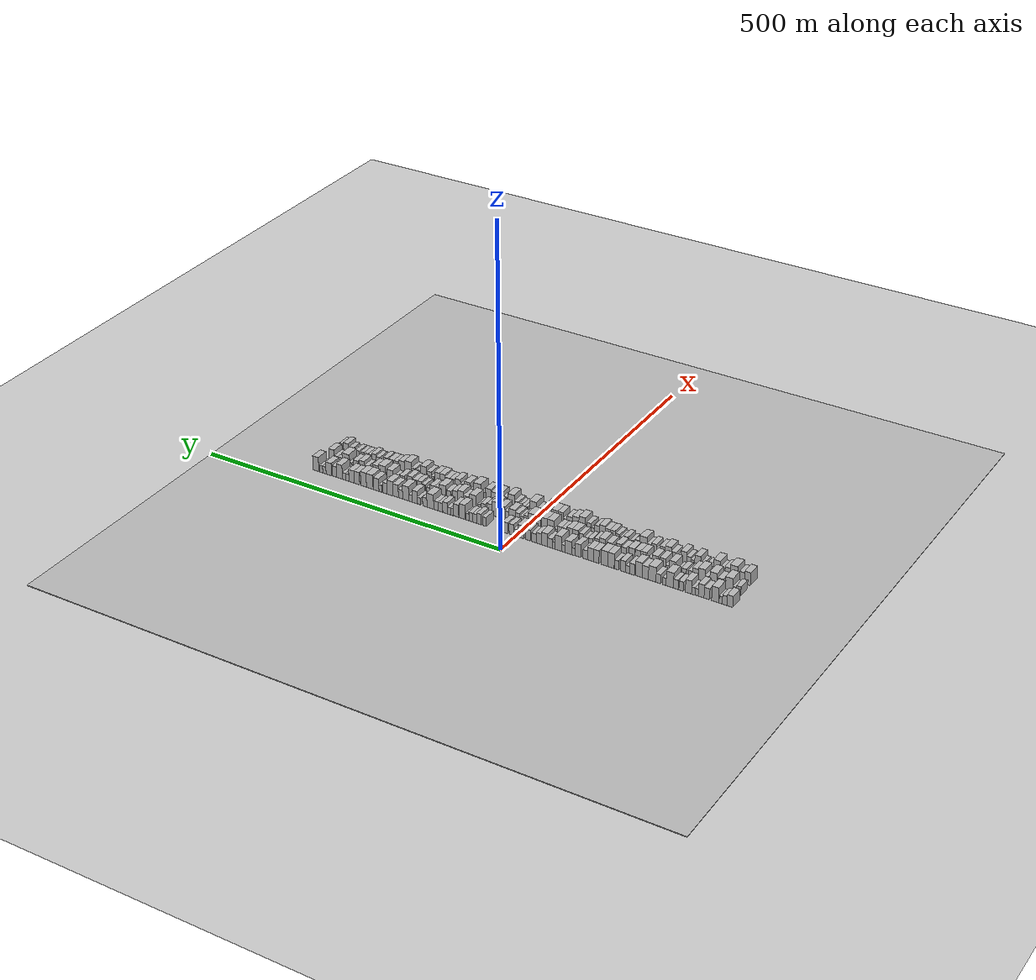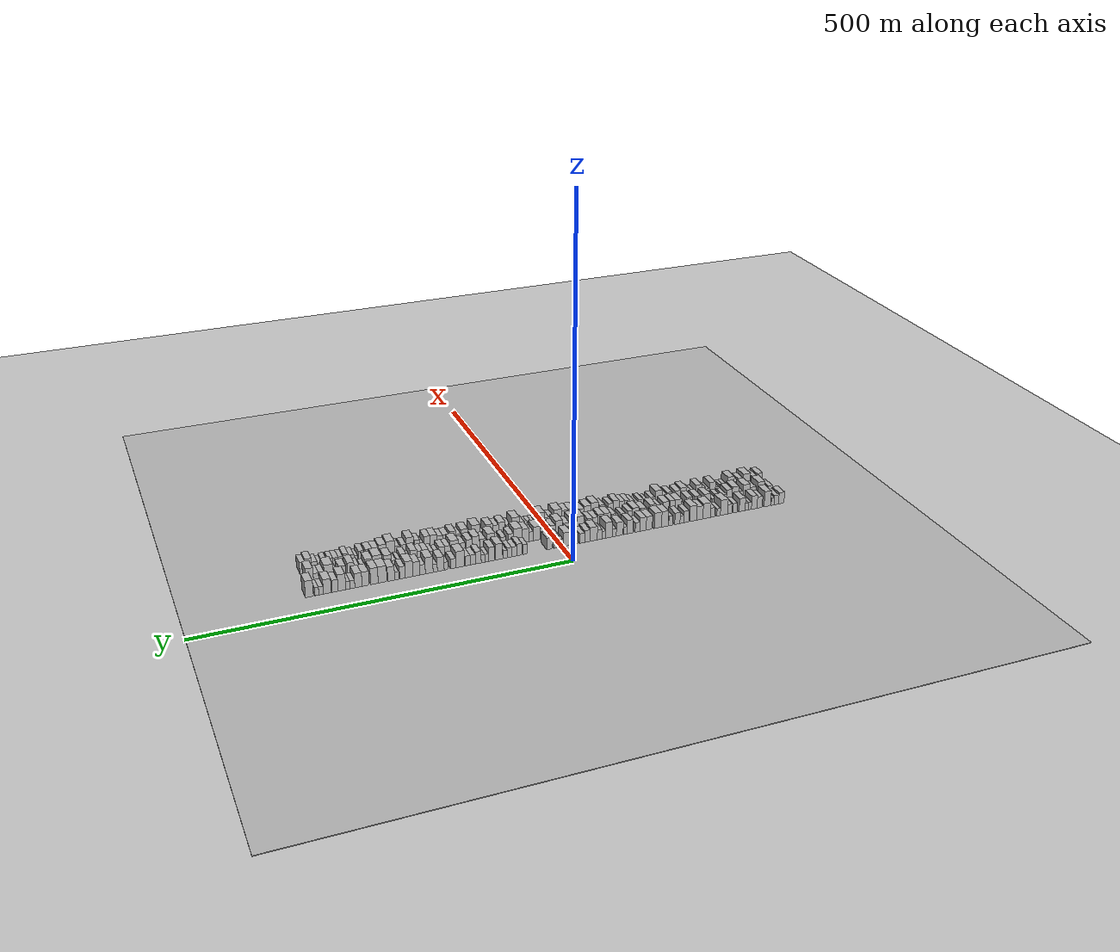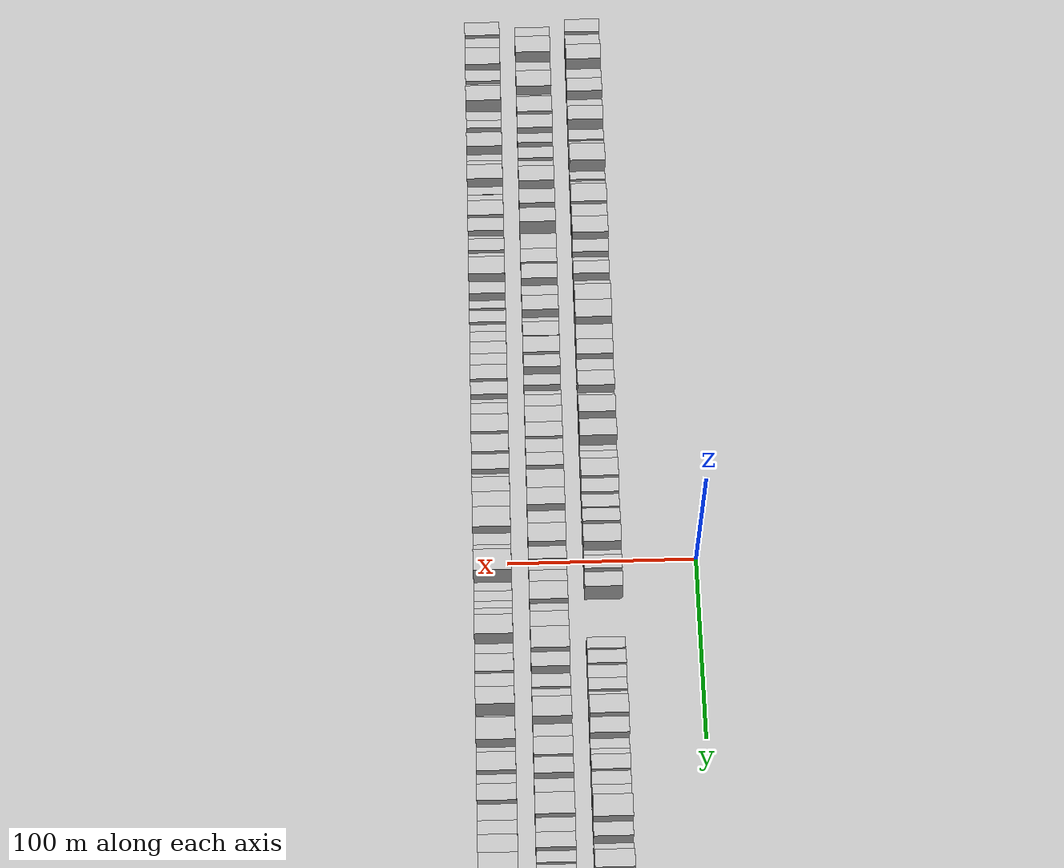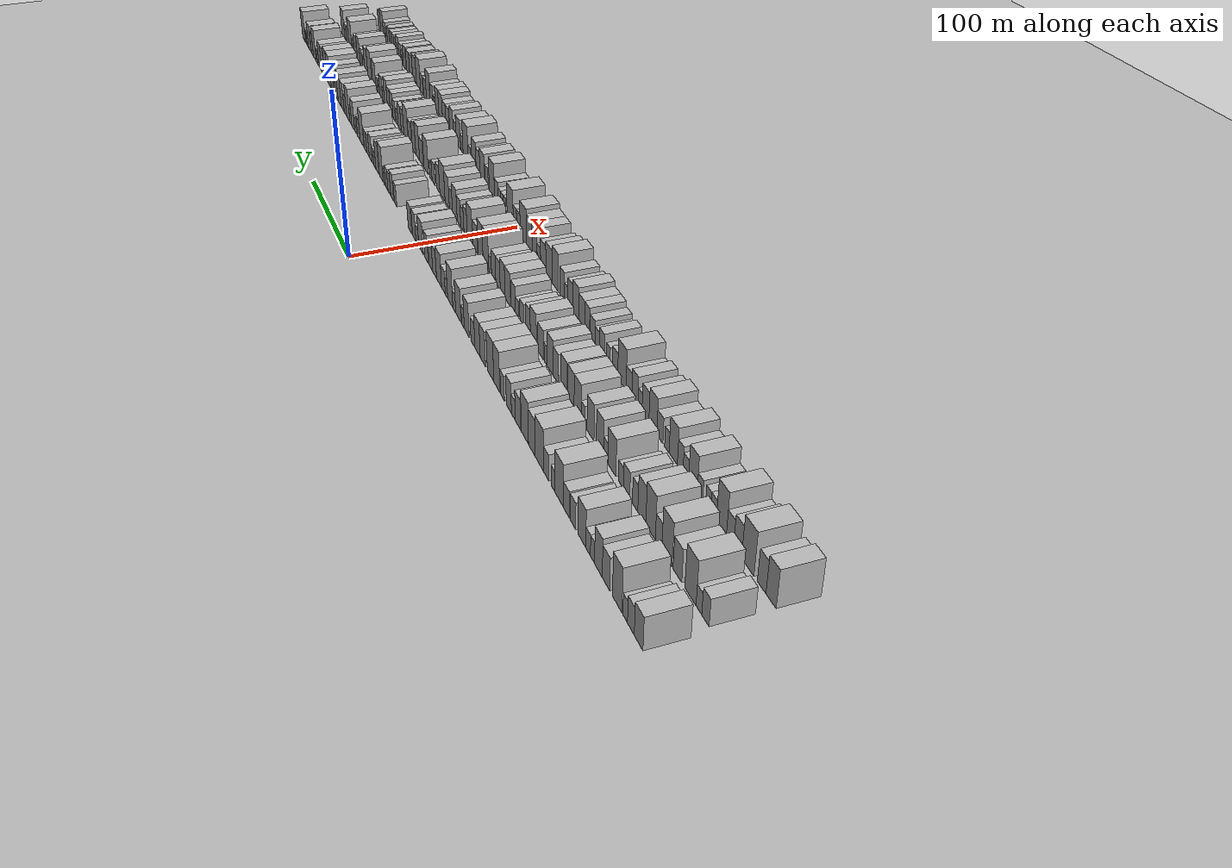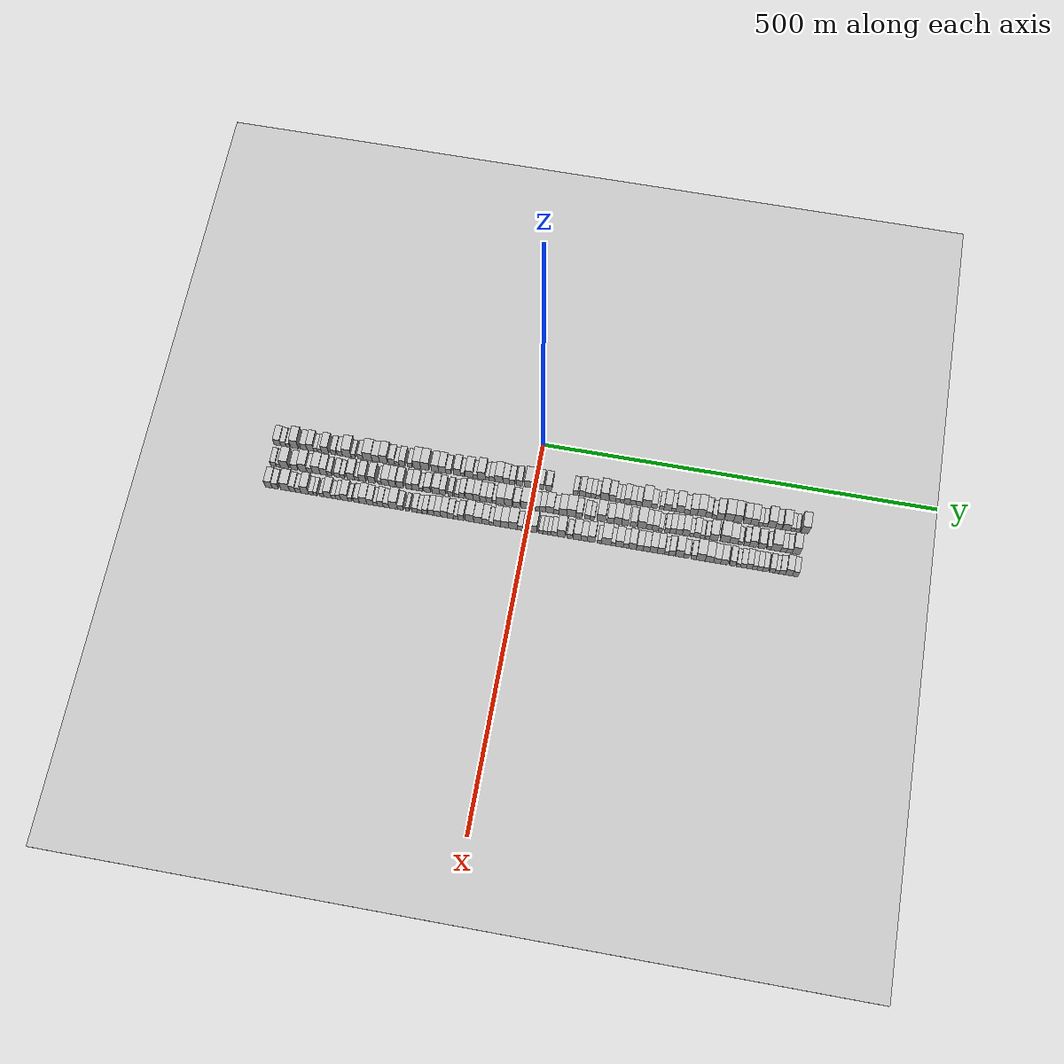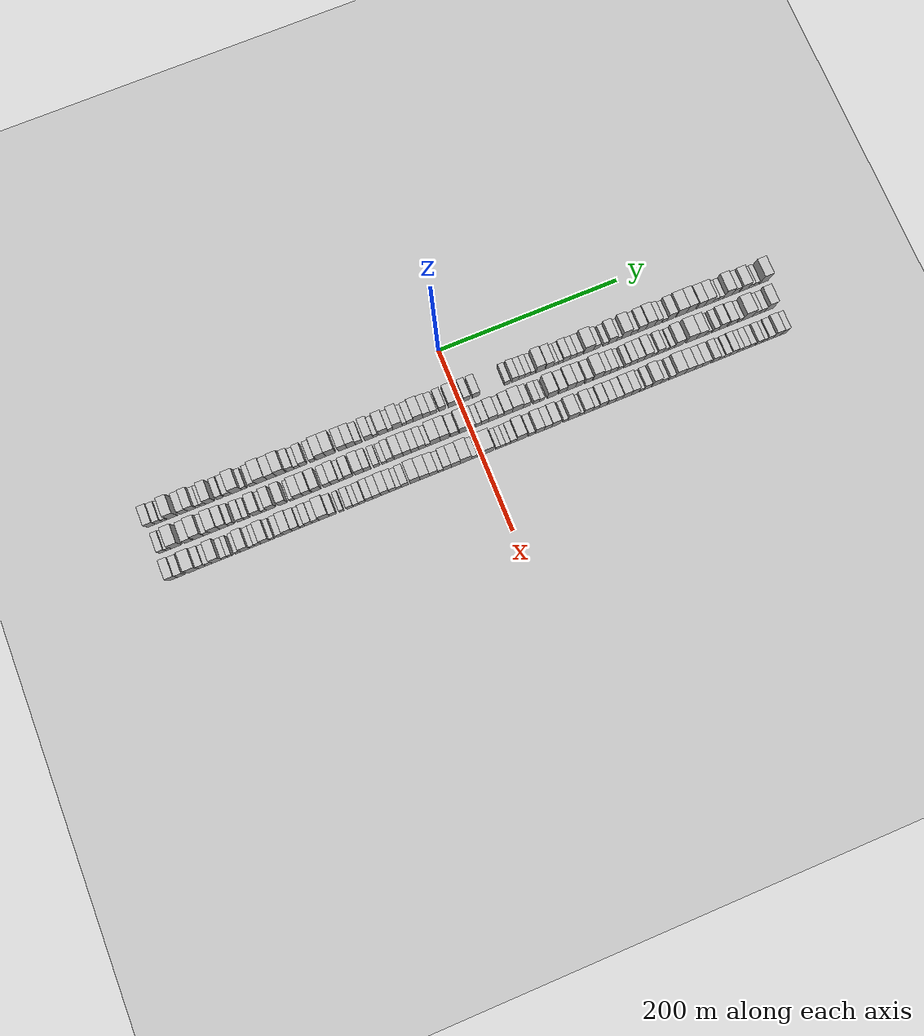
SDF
<?xml version="1.0" encoding="utf-8"?>

<sdf version="1.6">

   <world name="default">

      <gui fullscreen="0">

         <camera name="user_camera">

            <pose>-15 0 4.57585 0 0 0</pose>

            <view_controller>orbit</view_controller>

         </camera>

      </gui>

      <scene>

         <sky>

           <clouds>

             <speed>12</speed>

           </clouds>

         </sky>

         <ambient>0.4 0.4 0.4 1</ambient>

         <background>0.7 0.7 0.7 1</background>

         <shadows>1</shadows>

      </scene>

      <gravity>0 0 -9.8066</gravity>

      <magnetic_field>6e-06 2.3e-05 -4.2e-05</magnetic_field>

      <physics default="0" name="default_physics" type="ode">

         <ode>

            <solver>

               <type>quick</type>

               <iters>10</iters>

               <sor>1.0</sor>

               <use_dynamic_moi_rescaling>0</use_dynamic_moi_rescaling>

            </solver>

            <constraints>

               <cfm>0</cfm>

               <erp>0.2</erp>

               <contact_max_correcting_vel>100</contact_max_correcting_vel>

               <contact_surface_layer>0.001</contact_surface_layer>

            </constraints>

         </ode>

         <max_step_size>0.004</max_step_size>

         <real_time_factor>1</real_time_factor>

         <real_time_update_rate>250</real_time_update_rate>

      </physics>

      <light name="sun" type="directional">

         <cast_shadows>1</cast_shadows>

         <pose>0 0 10 0 0 0</pose>

         <diffuse>0.8 0.8 0.8 1</diffuse>

         <specular>0.2 0.2 0.2 1</specular>

         <attenuation>

            <range>1000</range>

            <constant>0.9</constant>

            <linear>0.01</linear>

            <quadratic>0.001</quadratic>

         </attenuation>

         <direction>-0.5 0.1 -0.9</direction>

      </light>

      <include>

         <name>ground_plane_1</name>

         <uri>model://HANNAS_ground_plane</uri>

         <pose>0 0 0  0 0 0</pose>

      </include>

      <include>

         <name>ground_plane_2</name>

         <uri>model://HANNAS_ground_plane</uri>

         <pose>100 0 0  0 0 0</pose>

      </include>

      <model name="building_1">

         <static>1</static>

         <pose frame="">50.0000 -331.6268 0 0.000000 0.000000 0.000000</pose>

         <link name="link">

            <pose frame="">0 0 9.00 0 0 0</pose>

            <collision name="collision">

               <geometry>

                  <box>

                     <size>20.0000 8.7465 18.0000</size>

                  </box>

               </geometry>

               <max_contacts>10</max_contacts>

               <surface>

                  <contact>

                     <ode/>

                  </contact>

                  <bounce/>

                  <friction>

                     <torsional>

                        <ode/>

                     </torsional>

                     <ode/>

                  </friction>

               </surface>

            </collision>

            <visual name="visual">

               <cast_shadows>0</cast_shadows>

               <geometry>

                  <box>

                     <size>20.0000 8.7465 18.0000</size>

                  </box>

               </geometry>

               <material>

                  <script>

                     <uri>model://HANNAS_wall/materials/scripts</uri>

                     <uri>model://HANNAS_wall/materials/textures</uri>

                     <name>vrc/HANNAS_wall</name>

                  </script>

               </material>

            </visual>

            <self_collide>0</self_collide>

            <enable_wind>0</enable_wind>

            <kinematic>0</kinematic>

         </link>

      </model>

      <model name="building_2">

         <static>1</static>

         <pose frame="">50.0000 -323.7669 0 0.000000 0.000000 0.000000</pose>

         <link name="link">

            <pose frame="">0 0 7.50 0 0 0</pose>

            <collision name="collision">

               <geometry>

                  <box>

                     <size>20.0000 6.9732 15.0000</size>

                  </box>

               </geometry>

               <max_contacts>10</max_contacts>

               <surface>

                  <contact>

                     <ode/>

                  </contact>

                  <bounce/>

                  <friction>

                     <torsional>

                        <ode/>

                     </torsional>

                     <ode/>

                  </friction>

               </surface>

            </collision>

            <visual name="visual">

               <cast_shadows>0</cast_shadows>

               <geometry>

                  <box>

                     <size>20.0000 6.9732 15.0000</size>

                  </box>

               </geometry>

               <material>

                  <script>

                     <uri>model://HANNAS_wall/materials/scripts</uri>

                     <uri>model://HANNAS_wall/materials/textures</uri>

                     <name>vrc/HANNAS_wall</name>

                  </script>

               </material>

            </visual>

            <self_collide>0</self_collide>

            <enable_wind>0</enable_wind>

            <kinematic>0</kinematic>

         </link>

      </model>

      <model name="building_3">

         <static>1</static>

         <pose frame="">50.0000 -317.8753 0 0.000000 0.000000 0.000000</pose>

         <link name="link">

            <pose frame="">0 0 6.00 0 0 0</pose>

            <collision name="collision">

               <geometry>

                  <box>

                     <size>20.0000 4.8100 12.0000</size>

                  </box>

               </geometry>

               <max_contacts>10</max_contacts>

               <surface>

                  <contact>

                     <ode/>

                  </contact>

                  <bounce/>

                  <friction>

                     <torsional>

                        <ode/>

                     </torsional>

                     <ode/>

                  </friction>

               </surface>

            </collision>

            <visual name="visual">

               <cast_shadows>0</cast_shadows>

               <geometry>

                  <box>

                     <size>20.0000 4.8100 12.0000</size>

                  </box>

               </geometry>

               <material>

                  <script>

                     <uri>model://HANNAS_wall/materials/scripts</uri>

                     <uri>model://HANNAS_wall/materials/textures</uri>

                     <name>vrc/HANNAS_wall</name>

                  </script>

               </material>

            </visual>

            <self_collide>0</self_collide>

            <enable_wind>0</enable_wind>

            <kinematic>0</kinematic>

         </link>

      </model>

      <model name="building_4">

         <static>1</static>

         <pose frame="">50.0000 -309.3967 0 0.000000 0.000000 0.000000</pose>

         <link name="link">

            <pose frame="">0 0 12.00 0 0 0</pose>

            <collision name="collision">

               <geometry>

                  <box>

                     <size>20.0000 10.1470 24.0000</size>

                  </box>

               </geometry>

               <max_contacts>10</max_contacts>

               <surface>

                  <contact>

                     <ode/>

                  </contact>

                  <bounce/>

                  <friction>

                     <torsional>

                        <ode/>

                     </torsional>

                     <ode/>

                  </friction>

               </surface>

            </collision>

            <visual name="visual">

               <cast_shadows>0</cast_shadows>

               <geometry>

                  <box>

                     <size>20.0000 10.1470 24.0000</size>

                  </box>

               </geometry>

               <material>

                  <script>

                     <uri>model://HANNAS_wall/materials/scripts</uri>

                     <uri>model://HANNAS_wall/materials/textures</uri>

                     <name>vrc/HANNAS_wall</name>

                  </script>

               </material>

            </visual>

            <self_collide>0</self_collide>

            <enable_wind>0</enable_wind>

            <kinematic>0</kinematic>

         </link>

      </model>

      <model name="building_5">

         <static>1</static>

         <pose frame="">50.0000 -297.1925 0 0.000000 0.000000 0.000000</pose>

         <link name="link">

            <pose frame="">0 0 9.00 0 0 0</pose>

            <collision name="collision">

               <geometry>

                  <box>

                     <size>20.0000 8.2614 18.0000</size>

                  </box>

               </geometry>

               <max_contacts>10</max_contacts>

               <surface>

                  <contact>

                     <ode/>

                  </contact>

                  <bounce/>

                  <friction>

                     <torsional>

                        <ode/>

                     </torsional>

                     <ode/>

                  </friction>

               </surface>

            </collision>

            <visual name="visual">

               <cast_shadows>0</cast_shadows>

               <geometry>

                  <box>

                     <size>20.0000 8.2614 18.0000</size>

                  </box>

               </geometry>

               <material>

                  <script>

                     <uri>model://HANNAS_wall/materials/scripts</uri>

                     <uri>model://HANNAS_wall/materials/textures</uri>

                     <name>vrc/HANNAS_wall</name>

                  </script>

               </material>

            </visual>

            <self_collide>0</self_collide>

            <enable_wind>0</enable_wind>

            <kinematic>0</kinematic>

         </link>

      </model>

      <model name="building_6">

         <static>1</static>

         <pose frame="">50.0000 -288.6831 0 0.000000 0.000000 0.000000</pose>

         <link name="link">

            <pose frame="">0 0 10.50 0 0 0</pose>

            <collision name="collision">

               <geometry>

                  <box>

                     <size>20.0000 8.7574 21.0000</size>

                  </box>

               </geometry>

               <max_contacts>10</max_contacts>

               <surface>

                  <contact>

                     <ode/>

                  </contact>

                  <bounce/>

                  <friction>

                     <torsional>

                        <ode/>

                     </torsional>

                     <ode/>

                  </friction>

               </surface>

            </collision>

            <visual name="visual">

               <cast_shadows>0</cast_shadows>

               <geometry>

                  <box>

                     <size>20.0000 8.7574 21.0000</size>

                  </box>

               </geometry>

               <material>

                  <script>

                     <uri>model://HANNAS_wall/materials/scripts</uri>

                     <uri>model://HANNAS_wall/materials/textures</uri>

                     <name>vrc/HANNAS_wall</name>

                  </script>

               </material>

            </visual>

            <self_collide>0</self_collide>

            <enable_wind>0</enable_wind>

            <kinematic>0</kinematic>

         </link>

      </model>

      <model name="building_7">

         <static>1</static>

         <pose frame="">50.0000 -281.9020 0 0.000000 0.000000 0.000000</pose>

         <link name="link">

            <pose frame="">0 0 6.00 0 0 0</pose>

            <collision name="collision">

               <geometry>

                  <box>

                     <size>20.0000 4.8047 12.0000</size>

                  </box>

               </geometry>

               <max_contacts>10</max_contacts>

               <surface>

                  <contact>

                     <ode/>

                  </contact>

                  <bounce/>

                  <friction>

                     <torsional>

                        <ode/>

                     </torsional>

                     <ode/>

                  </friction>

               </surface>

            </collision>

            <visual name="visual">

               <cast_shadows>0</cast_shadows>

               <geometry>

                  <box>

                     <size>20.0000 4.8047 12.0000</size>

                  </box>

               </geometry>

               <material>

                  <script>

                     <uri>model://HANNAS_wall/materials/scripts</uri>

                     <uri>model://HANNAS_wall/materials/textures</uri>

                     <name>vrc/HANNAS_wall</name>

                  </script>

               </material>

            </visual>

            <self_collide>0</self_collide>

            <enable_wind>0</enable_wind>

            <kinematic>0</kinematic>

         </link>

      </model>

      <model name="building_8">

         <static>1</static>

         <pose frame="">50.0000 -276.8866 0 0.000000 0.000000 0.000000</pose>

         <link name="link">

            <pose frame="">0 0 6.00 0 0 0</pose>

            <collision name="collision">

               <geometry>

                  <box>

                     <size>20.0000 5.2261 12.0000</size>

                  </box>

               </geometry>

               <max_contacts>10</max_contacts>

               <surface>

                  <contact>

                     <ode/>

                  </contact>

                  <bounce/>

                  <friction>

                     <torsional>

                        <ode/>

                     </torsional>

                     <ode/>

                  </friction>

               </surface>

            </collision>

            <visual name="visual">

               <cast_shadows>0</cast_shadows>

               <geometry>

                  <box>

                     <size>20.0000 5.2261 12.0000</size>

                  </box>

               </geometry>

               <material>

                  <script>

                     <uri>model://HANNAS_wall/materials/scripts</uri>

                     <uri>model://HANNAS_wall/materials/textures</uri>

                     <name>vrc/HANNAS_wall</name>

                  </script>

               </material>

            </visual>

            <self_collide>0</self_collide>

            <enable_wind>0</enable_wind>

            <kinematic>0</kinematic>

         </link>

      </model>

      <model name="building_9">

         <static>1</static>

         <pose frame="">50.0000 -269.6459 0 0.000000 0.000000 0.000000</pose>

         <link name="link">

            <pose frame="">0 0 10.50 0 0 0</pose>

            <collision name="collision">

               <geometry>

                  <box>

                     <size>20.0000 9.2554 21.0000</size>

                  </box>

               </geometry>

               <max_contacts>10</max_contacts>

               <surface>

                  <contact>

                     <ode/>

                  </contact>

                  <bounce/>

                  <friction>

                     <torsional>

                        <ode/>

                     </torsional>

                     <ode/>

                  </friction>

               </surface>

            </collision>

            <visual name="visual">

               <cast_shadows>0</cast_shadows>

               <geometry>

                  <box>

                     <size>20.0000 9.2554 21.0000</size>

                  </box>

               </geometry>

               <material>

                  <script>

                     <uri>model://HANNAS_wall/materials/scripts</uri>

                     <uri>model://HANNAS_wall/materials/textures</uri>

                     <name>vrc/HANNAS_wall</name>

                  </script>

               </material>

            </visual>

            <self_collide>0</self_collide>

            <enable_wind>0</enable_wind>

            <kinematic>0</kinematic>

         </link>

      </model>

      <model name="building_10">

         <static>1</static>

         <pose frame="">50.0000 -258.6013 0 0.000000 0.000000 0.000000</pose>

         <link name="link">

            <pose frame="">0 0 7.50 0 0 0</pose>

            <collision name="collision">

               <geometry>

                  <box>

                     <size>20.0000 6.8338 15.0000</size>

                  </box>

               </geometry>

               <max_contacts>10</max_contacts>

               <surface>

                  <contact>

                     <ode/>

                  </contact>

                  <bounce/>

                  <friction>

                     <torsional>

                        <ode/>

                     </torsional>

                     <ode/>

                  </friction>

               </surface>

            </collision>

            <visual name="visual">

               <cast_shadows>0</cast_shadows>

               <geometry>

                  <box>

                     <size>20.0000 6.8338 15.0000</size>

                  </box>

               </geometry>

               <material>

                  <script>

                     <uri>model://HANNAS_wall/materials/scripts</uri>

                     <uri>model://HANNAS_wall/materials/textures</uri>

                     <name>vrc/HANNAS_wall</name>

                  </script>

               </material>

            </visual>

            <self_collide>0</self_collide>

            <enable_wind>0</enable_wind>

            <kinematic>0</kinematic>

         </link>

      </model>

      <model name="building_11">

         <static>1</static>

         <pose frame="">50.0000 -250.5868 0 0.000000 0.000000 0.000000</pose>

         <link name="link">

            <pose frame="">0 0 7.50 0 0 0</pose>

            <collision name="collision">

               <geometry>

                  <box>

                     <size>20.0000 7.1953 15.0000</size>

                  </box>

               </geometry>

               <max_contacts>10</max_contacts>

               <surface>

                  <contact>

                     <ode/>

                  </contact>

                  <bounce/>

                  <friction>

                     <torsional>

                        <ode/>

                     </torsional>

                     <ode/>

                  </friction>

               </surface>

            </collision>

            <visual name="visual">

               <cast_shadows>0</cast_shadows>

               <geometry>

                  <box>

                     <size>20.0000 7.1953 15.0000</size>

                  </box>

               </geometry>

               <material>

                  <script>

                     <uri>model://HANNAS_wall/materials/scripts</uri>

                     <uri>model://HANNAS_wall/materials/textures</uri>

                     <name>vrc/HANNAS_wall</name>

                  </script>

               </material>

            </visual>

            <self_collide>0</self_collide>

            <enable_wind>0</enable_wind>

            <kinematic>0</kinematic>

         </link>

      </model>

      <model name="building_12">

         <static>1</static>

         <pose frame="">50.0000 -241.3926 0 0.000000 0.000000 0.000000</pose>

         <link name="link">

            <pose frame="">0 0 12.00 0 0 0</pose>

            <collision name="collision">

               <geometry>

                  <box>

                     <size>20.0000 11.1932 24.0000</size>

                  </box>

               </geometry>

               <max_contacts>10</max_contacts>

               <surface>

                  <contact>

                     <ode/>

                  </contact>

                  <bounce/>

                  <friction>

                     <torsional>

                        <ode/>

                     </torsional>

                     <ode/>

                  </friction>

               </surface>

            </collision>

            <visual name="visual">

               <cast_shadows>0</cast_shadows>

               <geometry>

                  <box>

                     <size>20.0000 11.1932 24.0000</size>

                  </box>

               </geometry>

               <material>

                  <script>

                     <uri>model://HANNAS_wall/materials/scripts</uri>

                     <uri>model://HANNAS_wall/materials/textures</uri>

                     <name>vrc/HANNAS_wall</name>

                  </script>

               </material>

            </visual>

            <self_collide>0</self_collide>

            <enable_wind>0</enable_wind>

            <kinematic>0</kinematic>

         </link>

      </model>

      <model name="building_13">

         <static>1</static>

         <pose frame="">50.0000 -233.1363 0 0.000000 0.000000 0.000000</pose>

         <link name="link">

            <pose frame="">0 0 6.00 0 0 0</pose>

            <collision name="collision">

               <geometry>

                  <box>

                     <size>20.0000 5.3193 12.0000</size>

                  </box>

               </geometry>

               <max_contacts>10</max_contacts>

               <surface>

                  <contact>

                     <ode/>

                  </contact>

                  <bounce/>

                  <friction>

                     <torsional>

                        <ode/>

                     </torsional>

                     <ode/>

                  </friction>

               </surface>

            </collision>

            <visual name="visual">

               <cast_shadows>0</cast_shadows>

               <geometry>

                  <box>

                     <size>20.0000 5.3193 12.0000</size>

                  </box>

               </geometry>

               <material>

                  <script>

                     <uri>model://HANNAS_wall/materials/scripts</uri>

                     <uri>model://HANNAS_wall/materials/textures</uri>

                     <name>vrc/HANNAS_wall</name>

                  </script>

               </material>

            </visual>

            <self_collide>0</self_collide>

            <enable_wind>0</enable_wind>

            <kinematic>0</kinematic>

         </link>

      </model>

      <model name="building_14">

         <static>1</static>

         <pose frame="">50.0000 -223.9610 0 0.000000 0.000000 0.000000</pose>

         <link name="link">

            <pose frame="">0 0 7.50 0 0 0</pose>

            <collision name="collision">

               <geometry>

                  <box>

                     <size>20.0000 7.0312 15.0000</size>

                  </box>

               </geometry>

               <max_contacts>10</max_contacts>

               <surface>

                  <contact>

                     <ode/>

                  </contact>

                  <bounce/>

                  <friction>

                     <torsional>

                        <ode/>

                     </torsional>

                     <ode/>

                  </friction>

               </surface>

            </collision>

            <visual name="visual">

               <cast_shadows>0</cast_shadows>

               <geometry>

                  <box>

                     <size>20.0000 7.0312 15.0000</size>

                  </box>

               </geometry>

               <material>

                  <script>

                     <uri>model://HANNAS_wall/materials/scripts</uri>

                     <uri>model://HANNAS_wall/materials/textures</uri>

                     <name>vrc/HANNAS_wall</name>

                  </script>

               </material>

            </visual>

            <self_collide>0</self_collide>

            <enable_wind>0</enable_wind>

            <kinematic>0</kinematic>

         </link>

      </model>

      <model name="building_15">

         <static>1</static>

         <pose frame="">50.0000 -214.6187 0 0.000000 0.000000 0.000000</pose>

         <link name="link">

            <pose frame="">0 0 12.00 0 0 0</pose>

            <collision name="collision">

               <geometry>

                  <box>

                     <size>20.0000 11.6534 24.0000</size>

                  </box>

               </geometry>

               <max_contacts>10</max_contacts>

               <surface>

                  <contact>

                     <ode/>

                  </contact>

                  <bounce/>

                  <friction>

                     <torsional>

                        <ode/>

                     </torsional>

                     <ode/>

                  </friction>

               </surface>

            </collision>

            <visual name="visual">

               <cast_shadows>0</cast_shadows>

               <geometry>

                  <box>

                     <size>20.0000 11.6534 24.0000</size>

                  </box>

               </geometry>

               <material>

                  <script>

                     <uri>model://HANNAS_wall/materials/scripts</uri>

                     <uri>model://HANNAS_wall/materials/textures</uri>

                     <name>vrc/HANNAS_wall</name>

                  </script>

               </material>

            </visual>

            <self_collide>0</self_collide>

            <enable_wind>0</enable_wind>

            <kinematic>0</kinematic>

         </link>

      </model>

      <model name="building_16">

         <static>1</static>

         <pose frame="">50.0000 -204.0040 0 0.000000 0.000000 0.000000</pose>

         <link name="link">

            <pose frame="">0 0 10.50 0 0 0</pose>

            <collision name="collision">

               <geometry>

                  <box>

                     <size>20.0000 9.5760 21.0000</size>

                  </box>

               </geometry>

               <max_contacts>10</max_contacts>

               <surface>

                  <contact>

                     <ode/>

                  </contact>

                  <bounce/>

                  <friction>

                     <torsional>

                        <ode/>

                     </torsional>

                     <ode/>

                  </friction>

               </surface>

            </collision>

            <visual name="visual">

               <cast_shadows>0</cast_shadows>

               <geometry>

                  <box>

                     <size>20.0000 9.5760 21.0000</size>

                  </box>

               </geometry>

               <material>

                  <script>

                     <uri>model://HANNAS_wall/materials/scripts</uri>

                     <uri>model://HANNAS_wall/materials/textures</uri>

                     <name>vrc/HANNAS_wall</name>

                  </script>

               </material>

            </visual>

            <self_collide>0</self_collide>

            <enable_wind>0</enable_wind>

            <kinematic>0</kinematic>

         </link>

      </model>

      <model name="building_17">

         <static>1</static>

         <pose frame="">50.0000 -194.0085 0 0.000000 0.000000 0.000000</pose>

         <link name="link">

            <pose frame="">0 0 12.00 0 0 0</pose>

            <collision name="collision">

               <geometry>

                  <box>

                     <size>20.0000 10.4152 24.0000</size>

                  </box>

               </geometry>

               <max_contacts>10</max_contacts>

               <surface>

                  <contact>

                     <ode/>

                  </contact>

                  <bounce/>

                  <friction>

                     <torsional>

                        <ode/>

                     </torsional>

                     <ode/>

                  </friction>

               </surface>

            </collision>

            <visual name="visual">

               <cast_shadows>0</cast_shadows>

               <geometry>

                  <box>

                     <size>20.0000 10.4152 24.0000</size>

                  </box>

               </geometry>

               <material>

                  <script>

                     <uri>model://HANNAS_wall/materials/scripts</uri>

                     <uri>model://HANNAS_wall/materials/textures</uri>

                     <name>vrc/HANNAS_wall</name>

                  </script>

               </material>

            </visual>

            <self_collide>0</self_collide>

            <enable_wind>0</enable_wind>

            <kinematic>0</kinematic>

         </link>

      </model>

      <model name="building_18">

         <static>1</static>

         <pose frame="">50.0000 -183.7888 0 0.000000 0.000000 0.000000</pose>

         <link name="link">

            <pose frame="">0 0 9.00 0 0 0</pose>

            <collision name="collision">

               <geometry>

                  <box>

                     <size>20.0000 8.0241 18.0000</size>

                  </box>

               </geometry>

               <max_contacts>10</max_contacts>

               <surface>

                  <contact>

                     <ode/>

                  </contact>

                  <bounce/>

                  <friction>

                     <torsional>

                        <ode/>

                     </torsional>

                     <ode/>

                  </friction>

               </surface>

            </collision>

            <visual name="visual">

               <cast_shadows>0</cast_shadows>

               <geometry>

                  <box>

                     <size>20.0000 8.0241 18.0000</size>

                  </box>

               </geometry>

               <material>

                  <script>

                     <uri>model://HANNAS_wall/materials/scripts</uri>

                     <uri>model://HANNAS_wall/materials/textures</uri>

                     <name>vrc/HANNAS_wall</name>

                  </script>

               </material>

            </visual>

            <self_collide>0</self_collide>

            <enable_wind>0</enable_wind>

            <kinematic>0</kinematic>

         </link>

      </model>

      <model name="building_19">

         <static>1</static>

         <pose frame="">50.0000 -176.8450 0 0.000000 0.000000 0.000000</pose>

         <link name="link">

            <pose frame="">0 0 6.00 0 0 0</pose>

            <collision name="collision">

               <geometry>

                  <box>

                     <size>20.0000 5.8635 12.0000</size>

                  </box>

               </geometry>

               <max_contacts>10</max_contacts>

               <surface>

                  <contact>

                     <ode/>

                  </contact>

                  <bounce/>

                  <friction>

                     <torsional>

                        <ode/>

                     </torsional>

                     <ode/>

                  </friction>

               </surface>

            </collision>

            <visual name="visual">

               <cast_shadows>0</cast_shadows>

               <geometry>

                  <box>

                     <size>20.0000 5.8635 12.0000</size>

                  </box>

               </geometry>

               <material>

                  <script>

                     <uri>model://HANNAS_wall/materials/scripts</uri>

                     <uri>model://HANNAS_wall/materials/textures</uri>

                     <name>vrc/HANNAS_wall</name>

                  </script>

               </material>

            </visual>

            <self_collide>0</self_collide>

            <enable_wind>0</enable_wind>

            <kinematic>0</kinematic>

         </link>

      </model>

      <model name="building_20">

         <static>1</static>

         <pose frame="">50.0000 -169.9643 0 0.000000 0.000000 0.000000</pose>

         <link name="link">

            <pose frame="">0 0 9.00 0 0 0</pose>

            <collision name="collision">

               <geometry>

                  <box>

                     <size>20.0000 7.8979 18.0000</size>

                  </box>

               </geometry>

               <max_contacts>10</max_contacts>

               <surface>

                  <contact>

                     <ode/>

                  </contact>

                  <bounce/>

                  <friction>

                     <torsional>

                        <ode/>

                     </torsional>

                     <ode/>

                  </friction>

               </surface>

            </collision>

            <visual name="visual">

               <cast_shadows>0</cast_shadows>

               <geometry>

                  <box>

                     <size>20.0000 7.8979 18.0000</size>

                  </box>

               </geometry>

               <material>

                  <script>

                     <uri>model://HANNAS_wall/materials/scripts</uri>

                     <uri>model://HANNAS_wall/materials/textures</uri>

                     <name>vrc/HANNAS_wall</name>

                  </script>

               </material>

            </visual>

            <self_collide>0</self_collide>

            <enable_wind>0</enable_wind>

            <kinematic>0</kinematic>

         </link>

      </model>

      <model name="building_21">

         <static>1</static>

         <pose frame="">50.0000 -159.9730 0 0.000000 0.000000 0.000000</pose>

         <link name="link">

            <pose frame="">0 0 7.50 0 0 0</pose>

            <collision name="collision">

               <geometry>

                  <box>

                     <size>20.0000 6.0848 15.0000</size>

                  </box>

               </geometry>

               <max_contacts>10</max_contacts>

               <surface>

                  <contact>

                     <ode/>

                  </contact>

                  <bounce/>

                  <friction>

                     <torsional>

                        <ode/>

                     </torsional>

                     <ode/>

                  </friction>

               </surface>

            </collision>

            <visual name="visual">

               <cast_shadows>0</cast_shadows>

               <geometry>

                  <box>

                     <size>20.0000 6.0848 15.0000</size>

                  </box>

               </geometry>

               <material>

                  <script>

                     <uri>model://HANNAS_wall/materials/scripts</uri>

                     <uri>model://HANNAS_wall/materials/textures</uri>

                     <name>vrc/HANNAS_wall</name>

                  </script>

               </material>

            </visual>

            <self_collide>0</self_collide>

            <enable_wind>0</enable_wind>

            <kinematic>0</kinematic>

         </link>

      </model>

      <model name="building_22">

         <static>1</static>

         <pose frame="">50.0000 -151.0170 0 0.000000 0.000000 0.000000</pose>

         <link name="link">

            <pose frame="">0 0 12.00 0 0 0</pose>

            <collision name="collision">

               <geometry>

                  <box>

                     <size>20.0000 9.8271 24.0000</size>

                  </box>

               </geometry>

               <max_contacts>10</max_contacts>

               <surface>

                  <contact>

                     <ode/>

                  </contact>

                  <bounce/>

                  <friction>

                     <torsional>

                        <ode/>

                     </torsional>

                     <ode/>

                  </friction>

               </surface>

            </collision>

            <visual name="visual">

               <cast_shadows>0</cast_shadows>

               <geometry>

                  <box>

                     <size>20.0000 9.8271 24.0000</size>

                  </box>

               </geometry>

               <material>

                  <script>

                     <uri>model://HANNAS_wall/materials/scripts</uri>

                     <uri>model://HANNAS_wall/materials/textures</uri>

                     <name>vrc/HANNAS_wall</name>

                  </script>

               </material>

            </visual>

            <self_collide>0</self_collide>

            <enable_wind>0</enable_wind>

            <kinematic>0</kinematic>

         </link>

      </model>

      <model name="building_23">

         <static>1</static>

         <pose frame="">50.0000 -140.6810 0 0.000000 0.000000 0.000000</pose>

         <link name="link">

            <pose frame="">0 0 12.00 0 0 0</pose>

            <collision name="collision">

               <geometry>

                  <box>

                     <size>20.0000 10.8451 24.0000</size>

                  </box>

               </geometry>

               <max_contacts>10</max_contacts>

               <surface>

                  <contact>

                     <ode/>

                  </contact>

                  <bounce/>

                  <friction>

                     <torsional>

                        <ode/>

                     </torsional>

                     <ode/>

                  </friction>

               </surface>

            </collision>

            <visual name="visual">

               <cast_shadows>0</cast_shadows>

               <geometry>

                  <box>

                     <size>20.0000 10.8451 24.0000</size>

                  </box>

               </geometry>

               <material>

                  <script>

                     <uri>model://HANNAS_wall/materials/scripts</uri>

                     <uri>model://HANNAS_wall/materials/textures</uri>

                     <name>vrc/HANNAS_wall</name>

                  </script>

               </material>

            </visual>

            <self_collide>0</self_collide>

            <enable_wind>0</enable_wind>

            <kinematic>0</kinematic>

         </link>

      </model>

      <model name="building_24">

         <static>1</static>

         <pose frame="">50.0000 -127.7165 0 0.000000 0.000000 0.000000</pose>

         <link name="link">

            <pose frame="">0 0 10.50 0 0 0</pose>

            <collision name="collision">

               <geometry>

                  <box>

                     <size>20.0000 9.0838 21.0000</size>

                  </box>

               </geometry>

               <max_contacts>10</max_contacts>

               <surface>

                  <contact>

                     <ode/>

                  </contact>

                  <bounce/>

                  <friction>

                     <torsional>

                        <ode/>

                     </torsional>

                     <ode/>

                  </friction>

               </surface>

            </collision>

            <visual name="visual">

               <cast_shadows>0</cast_shadows>

               <geometry>

                  <box>

                     <size>20.0000 9.0838 21.0000</size>

                  </box>

               </geometry>

               <material>

                  <script>

                     <uri>model://HANNAS_wall/materials/scripts</uri>

                     <uri>model://HANNAS_wall/materials/textures</uri>

                     <name>vrc/HANNAS_wall</name>

                  </script>

               </material>

            </visual>

            <self_collide>0</self_collide>

            <enable_wind>0</enable_wind>

            <kinematic>0</kinematic>

         </link>

      </model>

      <model name="building_25">

         <static>1</static>

         <pose frame="">50.0000 -118.5763 0 0.000000 0.000000 0.000000</pose>

         <link name="link">

            <pose frame="">0 0 10.50 0 0 0</pose>

            <collision name="collision">

               <geometry>

                  <box>

                     <size>20.0000 9.1967 21.0000</size>

                  </box>

               </geometry>

               <max_contacts>10</max_contacts>

               <surface>

                  <contact>

                     <ode/>

                  </contact>

                  <bounce/>

                  <friction>

                     <torsional>

                        <ode/>

                     </torsional>

                     <ode/>

                  </friction>

               </surface>

            </collision>

            <visual name="visual">

               <cast_shadows>0</cast_shadows>

               <geometry>

                  <box>

                     <size>20.0000 9.1967 21.0000</size>

                  </box>

               </geometry>

               <material>

                  <script>

                     <uri>model://HANNAS_wall/materials/scripts</uri>

                     <uri>model://HANNAS_wall/materials/textures</uri>

                     <name>vrc/HANNAS_wall</name>

                  </script>

               </material>

            </visual>

            <self_collide>0</self_collide>

            <enable_wind>0</enable_wind>

            <kinematic>0</kinematic>

         </link>

      </model>

      <model name="building_26">

         <static>1</static>

         <pose frame="">50.0000 -110.3898 0 0.000000 0.000000 0.000000</pose>

         <link name="link">

            <pose frame="">0 0 7.50 0 0 0</pose>

            <collision name="collision">

               <geometry>

                  <box>

                     <size>20.0000 7.1761 15.0000</size>

                  </box>

               </geometry>

               <max_contacts>10</max_contacts>

               <surface>

                  <contact>

                     <ode/>

                  </contact>

                  <bounce/>

                  <friction>

                     <torsional>

                        <ode/>

                     </torsional>

                     <ode/>

                  </friction>

               </surface>

            </collision>

            <visual name="visual">

               <cast_shadows>0</cast_shadows>

               <geometry>

                  <box>

                     <size>20.0000 7.1761 15.0000</size>

                  </box>

               </geometry>

               <material>

                  <script>

                     <uri>model://HANNAS_wall/materials/scripts</uri>

                     <uri>model://HANNAS_wall/materials/textures</uri>

                     <name>vrc/HANNAS_wall</name>

                  </script>

               </material>

            </visual>

            <self_collide>0</self_collide>

            <enable_wind>0</enable_wind>

            <kinematic>0</kinematic>

         </link>

      </model>

      <model name="building_27">

         <static>1</static>

         <pose frame="">50.0000 -99.3260 0 0.000000 0.000000 0.000000</pose>

         <link name="link">

            <pose frame="">0 0 10.50 0 0 0</pose>

            <collision name="collision">

               <geometry>

                  <box>

                     <size>20.0000 8.9515 21.0000</size>

                  </box>

               </geometry>

               <max_contacts>10</max_contacts>

               <surface>

                  <contact>

                     <ode/>

                  </contact>

                  <bounce/>

                  <friction>

                     <torsional>

                        <ode/>

                     </torsional>

                     <ode/>

                  </friction>

               </surface>

            </collision>

            <visual name="visual">

               <cast_shadows>0</cast_shadows>

               <geometry>

                  <box>

                     <size>20.0000 8.9515 21.0000</size>

                  </box>

               </geometry>

               <material>

                  <script>

                     <uri>model://HANNAS_wall/materials/scripts</uri>

                     <uri>model://HANNAS_wall/materials/textures</uri>

                     <name>vrc/HANNAS_wall</name>

                  </script>

               </material>

            </visual>

            <self_collide>0</self_collide>

            <enable_wind>0</enable_wind>

            <kinematic>0</kinematic>

         </link>

      </model>

      <model name="building_28">

         <static>1</static>

         <pose frame="">50.0000 -92.3775 0 0.000000 0.000000 0.000000</pose>

         <link name="link">

            <pose frame="">0 0 6.00 0 0 0</pose>

            <collision name="collision">

               <geometry>

                  <box>

                     <size>20.0000 4.9455 12.0000</size>

                  </box>

               </geometry>

               <max_contacts>10</max_contacts>

               <surface>

                  <contact>

                     <ode/>

                  </contact>

                  <bounce/>

                  <friction>

                     <torsional>

                        <ode/>

                     </torsional>

                     <ode/>

                  </friction>

               </surface>

            </collision>

            <visual name="visual">

               <cast_shadows>0</cast_shadows>

               <geometry>

                  <box>

                     <size>20.0000 4.9455 12.0000</size>

                  </box>

               </geometry>

               <material>

                  <script>

                     <uri>model://HANNAS_wall/materials/scripts</uri>

                     <uri>model://HANNAS_wall/materials/textures</uri>

                     <name>vrc/HANNAS_wall</name>

                  </script>

               </material>

            </visual>

            <self_collide>0</self_collide>

            <enable_wind>0</enable_wind>

            <kinematic>0</kinematic>

         </link>

      </model>

      <model name="building_29">

         <static>1</static>

         <pose frame="">50.0000 -83.8792 0 0.000000 0.000000 0.000000</pose>

         <link name="link">

            <pose frame="">0 0 10.50 0 0 0</pose>

            <collision name="collision">

               <geometry>

                  <box>

                     <size>20.0000 10.0511 21.0000</size>

                  </box>

               </geometry>

               <max_contacts>10</max_contacts>

               <surface>

                  <contact>

                     <ode/>

                  </contact>

                  <bounce/>

                  <friction>

                     <torsional>

                        <ode/>

                     </torsional>

                     <ode/>

                  </friction>

               </surface>

            </collision>

            <visual name="visual">

               <cast_shadows>0</cast_shadows>

               <geometry>

                  <box>

                     <size>20.0000 10.0511 21.0000</size>

                  </box>

               </geometry>

               <material>

                  <script>

                     <uri>model://HANNAS_wall/materials/scripts</uri>

                     <uri>model://HANNAS_wall/materials/textures</uri>

                     <name>vrc/HANNAS_wall</name>

                  </script>

               </material>

            </visual>

            <self_collide>0</self_collide>

            <enable_wind>0</enable_wind>

            <kinematic>0</kinematic>

         </link>

      </model>

      <model name="building_30">

         <static>1</static>

         <pose frame="">50.0000 -76.0548 0 0.000000 0.000000 0.000000</pose>

         <link name="link">

            <pose frame="">0 0 6.00 0 0 0</pose>

            <collision name="collision">

               <geometry>

                  <box>

                     <size>20.0000 5.5977 12.0000</size>

                  </box>

               </geometry>

               <max_contacts>10</max_contacts>

               <surface>

                  <contact>

                     <ode/>

                  </contact>

                  <bounce/>

                  <friction>

                     <torsional>

                        <ode/>

                     </torsional>

                     <ode/>

                  </friction>

               </surface>

            </collision>

            <visual name="visual">

               <cast_shadows>0</cast_shadows>

               <geometry>

                  <box>

                     <size>20.0000 5.5977 12.0000</size>

                  </box>

               </geometry>

               <material>

                  <script>

                     <uri>model://HANNAS_wall/materials/scripts</uri>

                     <uri>model://HANNAS_wall/materials/textures</uri>

                     <name>vrc/HANNAS_wall</name>

                  </script>

               </material>

            </visual>

            <self_collide>0</self_collide>

            <enable_wind>0</enable_wind>

            <kinematic>0</kinematic>

         </link>

      </model>

      <model name="building_31">

         <static>1</static>

         <pose frame="">50.0000 -68.2252 0 0.000000 0.000000 0.000000</pose>

         <link name="link">

            <pose frame="">0 0 12.00 0 0 0</pose>

            <collision name="collision">

               <geometry>

                  <box>

                     <size>20.0000 10.0615 24.0000</size>

                  </box>

               </geometry>

               <max_contacts>10</max_contacts>

               <surface>

                  <contact>

                     <ode/>

                  </contact>

                  <bounce/>

                  <friction>

                     <torsional>

                        <ode/>

                     </torsional>

                     <ode/>

                  </friction>

               </surface>

            </collision>

            <visual name="visual">

               <cast_shadows>0</cast_shadows>

               <geometry>

                  <box>

                     <size>20.0000 10.0615 24.0000</size>

                  </box>

               </geometry>

               <material>

                  <script>

                     <uri>model://HANNAS_wall/materials/scripts</uri>

                     <uri>model://HANNAS_wall/materials/textures</uri>

                     <name>vrc/HANNAS_wall</name>

                  </script>

               </material>

            </visual>

            <self_collide>0</self_collide>

            <enable_wind>0</enable_wind>

            <kinematic>0</kinematic>

         </link>

      </model>

      <model name="building_32">

         <static>1</static>

         <pose frame="">50.0000 -60.7939 0 0.000000 0.000000 0.000000</pose>

         <link name="link">

            <pose frame="">0 0 6.00 0 0 0</pose>

            <collision name="collision">

               <geometry>

                  <box>

                     <size>20.0000 4.8011 12.0000</size>

                  </box>

               </geometry>

               <max_contacts>10</max_contacts>

               <surface>

                  <contact>

                     <ode/>

                  </contact>

                  <bounce/>

                  <friction>

                     <torsional>

                        <ode/>

                     </torsional>

                     <ode/>

                  </friction>

               </surface>

            </collision>

            <visual name="visual">

               <cast_shadows>0</cast_shadows>

               <geometry>

                  <box>

                     <size>20.0000 4.8011 12.0000</size>

                  </box>

               </geometry>

               <material>

                  <script>

                     <uri>model://HANNAS_wall/materials/scripts</uri>

                     <uri>model://HANNAS_wall/materials/textures</uri>

                     <name>vrc/HANNAS_wall</name>

                  </script>

               </material>

            </visual>

            <self_collide>0</self_collide>

            <enable_wind>0</enable_wind>

            <kinematic>0</kinematic>

         </link>

      </model>

      <model name="building_33">

         <static>1</static>

         <pose frame="">50.0000 -54.7445 0 0.000000 0.000000 0.000000</pose>

         <link name="link">

            <pose frame="">0 0 7.50 0 0 0</pose>

            <collision name="collision">

               <geometry>

                  <box>

                     <size>20.0000 7.2978 15.0000</size>

                  </box>

               </geometry>

               <max_contacts>10</max_contacts>

               <surface>

                  <contact>

                     <ode/>

                  </contact>

                  <bounce/>

                  <friction>

                     <torsional>

                        <ode/>

                     </torsional>

                     <ode/>

                  </friction>

               </surface>

            </collision>

            <visual name="visual">

               <cast_shadows>0</cast_shadows>

               <geometry>

                  <box>

                     <size>20.0000 7.2978 15.0000</size>

                  </box>

               </geometry>

               <material>

                  <script>

                     <uri>model://HANNAS_wall/materials/scripts</uri>

                     <uri>model://HANNAS_wall/materials/textures</uri>

                     <name>vrc/HANNAS_wall</name>

                  </script>

               </material>

            </visual>

            <self_collide>0</self_collide>

            <enable_wind>0</enable_wind>

            <kinematic>0</kinematic>

         </link>

      </model>

      <model name="building_34">

         <static>1</static>

         <pose frame="">50.0000 -45.9717 0 0.000000 0.000000 0.000000</pose>

         <link name="link">

            <pose frame="">0 0 10.50 0 0 0</pose>

            <collision name="collision">

               <geometry>

                  <box>

                     <size>20.0000 10.2478 21.0000</size>

                  </box>

               </geometry>

               <max_contacts>10</max_contacts>

               <surface>

                  <contact>

                     <ode/>

                  </contact>

                  <bounce/>

                  <friction>

                     <torsional>

                        <ode/>

                     </torsional>

                     <ode/>

                  </friction>

               </surface>

            </collision>

            <visual name="visual">

               <cast_shadows>0</cast_shadows>

               <geometry>

                  <box>

                     <size>20.0000 10.2478 21.0000</size>

                  </box>

               </geometry>

               <material>

                  <script>

                     <uri>model://HANNAS_wall/materials/scripts</uri>

                     <uri>model://HANNAS_wall/materials/textures</uri>

                     <name>vrc/HANNAS_wall</name>

                  </script>

               </material>

            </visual>

            <self_collide>0</self_collide>

            <enable_wind>0</enable_wind>

            <kinematic>0</kinematic>

         </link>

      </model>

      <model name="building_35">

         <static>1</static>

         <pose frame="">50.0000 -36.7895 0 0.000000 0.000000 0.000000</pose>

         <link name="link">

            <pose frame="">0 0 9.00 0 0 0</pose>

            <collision name="collision">

               <geometry>

                  <box>

                     <size>20.0000 8.1166 18.0000</size>

                  </box>

               </geometry>

               <max_contacts>10</max_contacts>

               <surface>

                  <contact>

                     <ode/>

                  </contact>

                  <bounce/>

                  <friction>

                     <torsional>

                        <ode/>

                     </torsional>

                     <ode/>

                  </friction>

               </surface>

            </collision>

            <visual name="visual">

               <cast_shadows>0</cast_shadows>

               <geometry>

                  <box>

                     <size>20.0000 8.1166 18.0000</size>

                  </box>

               </geometry>

               <material>

                  <script>

                     <uri>model://HANNAS_wall/materials/scripts</uri>

                     <uri>model://HANNAS_wall/materials/textures</uri>

                     <name>vrc/HANNAS_wall</name>

                  </script>

               </material>

            </visual>

            <self_collide>0</self_collide>

            <enable_wind>0</enable_wind>

            <kinematic>0</kinematic>

         </link>

      </model>

      <model name="building_36">

         <static>1</static>

         <pose frame="">50.0000 -29.0209 0 0.000000 0.000000 0.000000</pose>

         <link name="link">

            <pose frame="">0 0 7.50 0 0 0</pose>

            <collision name="collision">

               <geometry>

                  <box>

                     <size>20.0000 7.4207 15.0000</size>

                  </box>

               </geometry>

               <max_contacts>10</max_contacts>

               <surface>

                  <contact>

                     <ode/>

                  </contact>

                  <bounce/>

                  <friction>

                     <torsional>

                        <ode/>

                     </torsional>

                     <ode/>

                  </friction>

               </surface>

            </collision>

            <visual name="visual">

               <cast_shadows>0</cast_shadows>

               <geometry>

                  <box>

                     <size>20.0000 7.4207 15.0000</size>

                  </box>

               </geometry>

               <material>

                  <script>

                     <uri>model://HANNAS_wall/materials/scripts</uri>

                     <uri>model://HANNAS_wall/materials/textures</uri>

                     <name>vrc/HANNAS_wall</name>

                  </script>

               </material>

            </visual>

            <self_collide>0</self_collide>

            <enable_wind>0</enable_wind>

            <kinematic>0</kinematic>

         </link>

      </model>

      <model name="building_37">

         <static>1</static>

         <pose frame="">50.0000 -19.6073 0 0.000000 0.000000 0.000000</pose>

         <link name="link">

            <pose frame="">0 0 9.00 0 0 0</pose>

            <collision name="collision">

               <geometry>

                  <box>

                     <size>20.0000 7.4065 18.0000</size>

                  </box>

               </geometry>

               <max_contacts>10</max_contacts>

               <surface>

                  <contact>

                     <ode/>

                  </contact>

                  <bounce/>

                  <friction>

                     <torsional>

                        <ode/>

                     </torsional>

                     <ode/>

                  </friction>

               </surface>

            </collision>

            <visual name="visual">

               <cast_shadows>0</cast_shadows>

               <geometry>

                  <box>

                     <size>20.0000 7.4065 18.0000</size>

                  </box>

               </geometry>

               <material>

                  <script>

                     <uri>model://HANNAS_wall/materials/scripts</uri>

                     <uri>model://HANNAS_wall/materials/textures</uri>

                     <name>vrc/HANNAS_wall</name>

                  </script>

               </material>

            </visual>

            <self_collide>0</self_collide>

            <enable_wind>0</enable_wind>

            <kinematic>0</kinematic>

         </link>

      </model>

      <model name="building_38">

         <static>1</static>

         <pose frame="">50.0000 -7.7778 0 0.000000 0.000000 0.000000</pose>

         <link name="link">

            <pose frame="">0 0 10.50 0 0 0</pose>

            <collision name="collision">

               <geometry>

                  <box>

                     <size>20.0000 10.2526 21.0000</size>

                  </box>

               </geometry>

               <max_contacts>10</max_contacts>

               <surface>

                  <contact>

                     <ode/>

                  </contact>

                  <bounce/>

                  <friction>

                     <torsional>

                        <ode/>

                     </torsional>

                     <ode/>

                  </friction>

               </surface>

            </collision>

            <visual name="visual">

               <cast_shadows>0</cast_shadows>

               <geometry>

                  <box>

                     <size>20.0000 10.2526 21.0000</size>

                  </box>

               </geometry>

               <material>

                  <script>

                     <uri>model://HANNAS_wall/materials/scripts</uri>

                     <uri>model://HANNAS_wall/materials/textures</uri>

                     <name>vrc/HANNAS_wall</name>

                  </script>

               </material>

            </visual>

            <self_collide>0</self_collide>

            <enable_wind>0</enable_wind>

            <kinematic>0</kinematic>

         </link>

      </model>

      <model name="building_39">

         <static>1</static>

         <pose frame="">50.0000 1.0077 0 0.000000 0.000000 0.000000</pose>

         <link name="link">

            <pose frame="">0 0 6.00 0 0 0</pose>

            <collision name="collision">

               <geometry>

                  <box>

                     <size>20.0000 5.3183 12.0000</size>

                  </box>

               </geometry>

               <max_contacts>10</max_contacts>

               <surface>

                  <contact>

                     <ode/>

                  </contact>

                  <bounce/>

                  <friction>

                     <torsional>

                        <ode/>

                     </torsional>

                     <ode/>

                  </friction>

               </surface>

            </collision>

            <visual name="visual">

               <cast_shadows>0</cast_shadows>

               <geometry>

                  <box>

                     <size>20.0000 5.3183 12.0000</size>

                  </box>

               </geometry>

               <material>

                  <script>

                     <uri>model://HANNAS_wall/materials/scripts</uri>

                     <uri>model://HANNAS_wall/materials/textures</uri>

                     <name>vrc/HANNAS_wall</name>

                  </script>

               </material>

            </visual>

            <self_collide>0</self_collide>

            <enable_wind>0</enable_wind>

            <kinematic>0</kinematic>

         </link>

      </model>

      <model name="building_40">

         <static>1</static>

         <pose frame="">50.0000 7.4504 0 0.000000 0.000000 0.000000</pose>

         <link name="link">

            <pose frame="">0 0 9.00 0 0 0</pose>

            <collision name="collision">

               <geometry>

                  <box>

                     <size>20.0000 7.5672 18.0000</size>

                  </box>

               </geometry>

               <max_contacts>10</max_contacts>

               <surface>

                  <contact>

                     <ode/>

                  </contact>

                  <bounce/>

                  <friction>

                     <torsional>

                        <ode/>

                     </torsional>

                     <ode/>

                  </friction>

               </surface>

            </collision>

            <visual name="visual">

               <cast_shadows>0</cast_shadows>

               <geometry>

                  <box>

                     <size>20.0000 7.5672 18.0000</size>

                  </box>

               </geometry>

               <material>

                  <script>

                     <uri>model://HANNAS_wall/materials/scripts</uri>

                     <uri>model://HANNAS_wall/materials/textures</uri>

                     <name>vrc/HANNAS_wall</name>

                  </script>

               </material>

            </visual>

            <self_collide>0</self_collide>

            <enable_wind>0</enable_wind>

            <kinematic>0</kinematic>

         </link>

      </model>

      <model name="building_41">

         <static>1</static>

         <pose frame="">50.0000 17.3543 0 0.000000 0.000000 0.000000</pose>

         <link name="link">

            <pose frame="">0 0 9.00 0 0 0</pose>

            <collision name="collision">

               <geometry>

                  <box>

                     <size>20.0000 8.2406 18.0000</size>

                  </box>

               </geometry>

               <max_contacts>10</max_contacts>

               <surface>

                  <contact>

                     <ode/>

                  </contact>

                  <bounce/>

                  <friction>

                     <torsional>

                        <ode/>

                     </torsional>

                     <ode/>

                  </friction>

               </surface>

            </collision>

            <visual name="visual">

               <cast_shadows>0</cast_shadows>

               <geometry>

                  <box>

                     <size>20.0000 8.2406 18.0000</size>

                  </box>

               </geometry>

               <material>

                  <script>

                     <uri>model://HANNAS_wall/materials/scripts</uri>

                     <uri>model://HANNAS_wall/materials/textures</uri>

                     <name>vrc/HANNAS_wall</name>

                  </script>

               </material>

            </visual>

            <self_collide>0</self_collide>

            <enable_wind>0</enable_wind>

            <kinematic>0</kinematic>

         </link>

      </model>

      <model name="building_42">

         <static>1</static>

         <pose frame="">50.0000 51.7338 0 0.000000 0.000000 0.000000</pose>

         <link name="link">

            <pose frame="">0 0 7.50 0 0 0</pose>

            <collision name="collision">

               <geometry>

                  <box>

                     <size>20.0000 6.1729 15.0000</size>

                  </box>

               </geometry>

               <max_contacts>10</max_contacts>

               <surface>

                  <contact>

                     <ode/>

                  </contact>

                  <bounce/>

                  <friction>

                     <torsional>

                        <ode/>

                     </torsional>

                     <ode/>

                  </friction>

               </surface>

            </collision>

            <visual name="visual">

               <cast_shadows>0</cast_shadows>

               <geometry>

                  <box>

                     <size>20.0000 6.1729 15.0000</size>

                  </box>

               </geometry>

               <material>

                  <script>

                     <uri>model://HANNAS_wall/materials/scripts</uri>

                     <uri>model://HANNAS_wall/materials/textures</uri>

                     <name>vrc/HANNAS_wall</name>

                  </script>

               </material>

            </visual>

            <self_collide>0</self_collide>

            <enable_wind>0</enable_wind>

            <kinematic>0</kinematic>

         </link>

      </model>

      <model name="building_43">

         <static>1</static>

         <pose frame="">50.0000 60.4232 0 0.000000 0.000000 0.000000</pose>

         <link name="link">

            <pose frame="">0 0 9.00 0 0 0</pose>

            <collision name="collision">

               <geometry>

                  <box>

                     <size>20.0000 7.2059 18.0000</size>

                  </box>

               </geometry>

               <max_contacts>10</max_contacts>

               <surface>

                  <contact>

                     <ode/>

                  </contact>

                  <bounce/>

                  <friction>

                     <torsional>

                        <ode/>

                     </torsional>

                     <ode/>

                  </friction>

               </surface>

            </collision>

            <visual name="visual">

               <cast_shadows>0</cast_shadows>

               <geometry>

                  <box>

                     <size>20.0000 7.2059 18.0000</size>

                  </box>

               </geometry>

               <material>

                  <script>

                     <uri>model://HANNAS_wall/materials/scripts</uri>

                     <uri>model://HANNAS_wall/materials/textures</uri>

                     <name>vrc/HANNAS_wall</name>

                  </script>

               </material>

            </visual>

            <self_collide>0</self_collide>

            <enable_wind>0</enable_wind>

            <kinematic>0</kinematic>

         </link>

      </model>

      <model name="building_44">

         <static>1</static>

         <pose frame="">50.0000 67.5245 0 0.000000 0.000000 0.000000</pose>

         <link name="link">

            <pose frame="">0 0 7.50 0 0 0</pose>

            <collision name="collision">

               <geometry>

                  <box>

                     <size>20.0000 6.9966 15.0000</size>

                  </box>

               </geometry>

               <max_contacts>10</max_contacts>

               <surface>

                  <contact>

                     <ode/>

                  </contact>

                  <bounce/>

                  <friction>

                     <torsional>

                        <ode/>

                     </torsional>

                     <ode/>

                  </friction>

               </surface>

            </collision>

            <visual name="visual">

               <cast_shadows>0</cast_shadows>

               <geometry>

                  <box>

                     <size>20.0000 6.9966 15.0000</size>

                  </box>

               </geometry>

               <material>

                  <script>

                     <uri>model://HANNAS_wall/materials/scripts</uri>

                     <uri>model://HANNAS_wall/materials/textures</uri>

                     <name>vrc/HANNAS_wall</name>

                  </script>

               </material>

            </visual>

            <self_collide>0</self_collide>

            <enable_wind>0</enable_wind>

            <kinematic>0</kinematic>

         </link>

      </model>

      <model name="building_45">

         <static>1</static>

         <pose frame="">50.0000 74.1940 0 0.000000 0.000000 0.000000</pose>

         <link name="link">

            <pose frame="">0 0 7.50 0 0 0</pose>

            <collision name="collision">

               <geometry>

                  <box>

                     <size>20.0000 6.3425 15.0000</size>

                  </box>

               </geometry>

               <max_contacts>10</max_contacts>

               <surface>

                  <contact>

                     <ode/>

                  </contact>

                  <bounce/>

                  <friction>

                     <torsional>

                        <ode/>

                     </torsional>

                     <ode/>

                  </friction>

               </surface>

            </collision>

            <visual name="visual">

               <cast_shadows>0</cast_shadows>

               <geometry>

                  <box>

                     <size>20.0000 6.3425 15.0000</size>

                  </box>

               </geometry>

               <material>

                  <script>

                     <uri>model://HANNAS_wall/materials/scripts</uri>

                     <uri>model://HANNAS_wall/materials/textures</uri>

                     <name>vrc/HANNAS_wall</name>

                  </script>

               </material>

            </visual>

            <self_collide>0</self_collide>

            <enable_wind>0</enable_wind>

            <kinematic>0</kinematic>

         </link>

      </model>

      <model name="building_46">

         <static>1</static>

         <pose frame="">50.0000 79.9017 0 0.000000 0.000000 0.000000</pose>

         <link name="link">

            <pose frame="">0 0 6.00 0 0 0</pose>

            <collision name="collision">

               <geometry>

                  <box>

                     <size>20.0000 5.0729 12.0000</size>

                  </box>

               </geometry>

               <max_contacts>10</max_contacts>

               <surface>

                  <contact>

                     <ode/>

                  </contact>

                  <bounce/>

                  <friction>

                     <torsional>

                        <ode/>

                     </torsional>

                     <ode/>

                  </friction>

               </surface>

            </collision>

            <visual name="visual">

               <cast_shadows>0</cast_shadows>

               <geometry>

                  <box>

                     <size>20.0000 5.0729 12.0000</size>

                  </box>

               </geometry>

               <material>

                  <script>

                     <uri>model://HANNAS_wall/materials/scripts</uri>

                     <uri>model://HANNAS_wall/materials/textures</uri>

                     <name>vrc/HANNAS_wall</name>

                  </script>

               </material>

            </visual>

            <self_collide>0</self_collide>

            <enable_wind>0</enable_wind>

            <kinematic>0</kinematic>

         </link>

      </model>

      <model name="building_47">

         <static>1</static>

         <pose frame="">50.0000 88.3860 0 0.000000 0.000000 0.000000</pose>

         <link name="link">

            <pose frame="">0 0 12.00 0 0 0</pose>

            <collision name="collision">

               <geometry>

                  <box>

                     <size>20.0000 9.8957 24.0000</size>

                  </box>

               </geometry>

               <max_contacts>10</max_contacts>

               <surface>

                  <contact>

                     <ode/>

                  </contact>

                  <bounce/>

                  <friction>

                     <torsional>

                        <ode/>

                     </torsional>

                     <ode/>

                  </friction>

               </surface>

            </collision>

            <visual name="visual">

               <cast_shadows>0</cast_shadows>

               <geometry>

                  <box>

                     <size>20.0000 9.8957 24.0000</size>

                  </box>

               </geometry>

               <material>

                  <script>

                     <uri>model://HANNAS_wall/materials/scripts</uri>

                     <uri>model://HANNAS_wall/materials/textures</uri>

                     <name>vrc/HANNAS_wall</name>

                  </script>

               </material>

            </visual>

            <self_collide>0</self_collide>

            <enable_wind>0</enable_wind>

            <kinematic>0</kinematic>

         </link>

      </model>

      <model name="building_48">

         <static>1</static>

         <pose frame="">50.0000 98.5657 0 0.000000 0.000000 0.000000</pose>

         <link name="link">

            <pose frame="">0 0 10.50 0 0 0</pose>

            <collision name="collision">

               <geometry>

                  <box>

                     <size>20.0000 8.4638 21.0000</size>

                  </box>

               </geometry>

               <max_contacts>10</max_contacts>

               <surface>

                  <contact>

                     <ode/>

                  </contact>

                  <bounce/>

                  <friction>

                     <torsional>

                        <ode/>

                     </torsional>

                     <ode/>

                  </friction>

               </surface>

            </collision>

            <visual name="visual">

               <cast_shadows>0</cast_shadows>

               <geometry>

                  <box>

                     <size>20.0000 8.4638 21.0000</size>

                  </box>

               </geometry>

               <material>

                  <script>

                     <uri>model://HANNAS_wall/materials/scripts</uri>

                     <uri>model://HANNAS_wall/materials/textures</uri>

                     <name>vrc/HANNAS_wall</name>

                  </script>

               </material>

            </visual>

            <self_collide>0</self_collide>

            <enable_wind>0</enable_wind>

            <kinematic>0</kinematic>

         </link>

      </model>

      <model name="building_49">

         <static>1</static>

         <pose frame="">50.0000 105.4845 0 0.000000 0.000000 0.000000</pose>

         <link name="link">

            <pose frame="">0 0 6.00 0 0 0</pose>

            <collision name="collision">

               <geometry>

                  <box>

                     <size>20.0000 5.3737 12.0000</size>

                  </box>

               </geometry>

               <max_contacts>10</max_contacts>

               <surface>

                  <contact>

                     <ode/>

                  </contact>

                  <bounce/>

                  <friction>

                     <torsional>

                        <ode/>

                     </torsional>

                     <ode/>

                  </friction>

               </surface>

            </collision>

            <visual name="visual">

               <cast_shadows>0</cast_shadows>

               <geometry>

                  <box>

                     <size>20.0000 5.3737 12.0000</size>

                  </box>

               </geometry>

               <material>

                  <script>

                     <uri>model://HANNAS_wall/materials/scripts</uri>

                     <uri>model://HANNAS_wall/materials/textures</uri>

                     <name>vrc/HANNAS_wall</name>

                  </script>

               </material>

            </visual>

            <self_collide>0</self_collide>

            <enable_wind>0</enable_wind>

            <kinematic>0</kinematic>

         </link>

      </model>

      <model name="building_50">

         <static>1</static>

         <pose frame="">50.0000 110.6867 0 0.000000 0.000000 0.000000</pose>

         <link name="link">

            <pose frame="">0 0 6.00 0 0 0</pose>

            <collision name="collision">

               <geometry>

                  <box>

                     <size>20.0000 5.0306 12.0000</size>

                  </box>

               </geometry>

               <max_contacts>10</max_contacts>

               <surface>

                  <contact>

                     <ode/>

                  </contact>

                  <bounce/>

                  <friction>

                     <torsional>

                        <ode/>

                     </torsional>

                     <ode/>

                  </friction>

               </surface>

            </collision>

            <visual name="visual">

               <cast_shadows>0</cast_shadows>

               <geometry>

                  <box>

                     <size>20.0000 5.0306 12.0000</size>

                  </box>

               </geometry>

               <material>

                  <script>

                     <uri>model://HANNAS_wall/materials/scripts</uri>

                     <uri>model://HANNAS_wall/materials/textures</uri>

                     <name>vrc/HANNAS_wall</name>

                  </script>

               </material>

            </visual>

            <self_collide>0</self_collide>

            <enable_wind>0</enable_wind>

            <kinematic>0</kinematic>

         </link>

      </model>

      <model name="building_51">

         <static>1</static>

         <pose frame="">50.0000 117.1437 0 0.000000 0.000000 0.000000</pose>

         <link name="link">

            <pose frame="">0 0 9.00 0 0 0</pose>

            <collision name="collision">

               <geometry>

                  <box>

                     <size>20.0000 7.8833 18.0000</size>

                  </box>

               </geometry>

               <max_contacts>10</max_contacts>

               <surface>

                  <contact>

                     <ode/>

                  </contact>

                  <bounce/>

                  <friction>

                     <torsional>

                        <ode/>

                     </torsional>

                     <ode/>

                  </friction>

               </surface>

            </collision>

            <visual name="visual">

               <cast_shadows>0</cast_shadows>

               <geometry>

                  <box>

                     <size>20.0000 7.8833 18.0000</size>

                  </box>

               </geometry>

               <material>

                  <script>

                     <uri>model://HANNAS_wall/materials/scripts</uri>

                     <uri>model://HANNAS_wall/materials/textures</uri>

                     <name>vrc/HANNAS_wall</name>

                  </script>

               </material>

            </visual>

            <self_collide>0</self_collide>

            <enable_wind>0</enable_wind>

            <kinematic>0</kinematic>

         </link>

      </model>

      <model name="building_52">

         <static>1</static>

         <pose frame="">50.0000 124.6534 0 0.000000 0.000000 0.000000</pose>

         <link name="link">

            <pose frame="">0 0 7.50 0 0 0</pose>

            <collision name="collision">

               <geometry>

                  <box>

                     <size>20.0000 7.1361 15.0000</size>

                  </box>

               </geometry>

               <max_contacts>10</max_contacts>

               <surface>

                  <contact>

                     <ode/>

                  </contact>

                  <bounce/>

                  <friction>

                     <torsional>

                        <ode/>

                     </torsional>

                     <ode/>

                  </friction>

               </surface>

            </collision>

            <visual name="visual">

               <cast_shadows>0</cast_shadows>

               <geometry>

                  <box>

                     <size>20.0000 7.1361 15.0000</size>

                  </box>

               </geometry>

               <material>

                  <script>

                     <uri>model://HANNAS_wall/materials/scripts</uri>

                     <uri>model://HANNAS_wall/materials/textures</uri>

                     <name>vrc/HANNAS_wall</name>

                  </script>

               </material>

            </visual>

            <self_collide>0</self_collide>

            <enable_wind>0</enable_wind>

            <kinematic>0</kinematic>

         </link>

      </model>

      <model name="building_53">

         <static>1</static>

         <pose frame="">50.0000 131.7565 0 0.000000 0.000000 0.000000</pose>

         <link name="link">

            <pose frame="">0 0 7.50 0 0 0</pose>

            <collision name="collision">

               <geometry>

                  <box>

                     <size>20.0000 7.0702 15.0000</size>

                  </box>

               </geometry>

               <max_contacts>10</max_contacts>

               <surface>

                  <contact>

                     <ode/>

                  </contact>

                  <bounce/>

                  <friction>

                     <torsional>

                        <ode/>

                     </torsional>

                     <ode/>

                  </friction>

               </surface>

            </collision>

            <visual name="visual">

               <cast_shadows>0</cast_shadows>

               <geometry>

                  <box>

                     <size>20.0000 7.0702 15.0000</size>

                  </box>

               </geometry>

               <material>

                  <script>

                     <uri>model://HANNAS_wall/materials/scripts</uri>

                     <uri>model://HANNAS_wall/materials/textures</uri>

                     <name>vrc/HANNAS_wall</name>

                  </script>

               </material>

            </visual>

            <self_collide>0</self_collide>

            <enable_wind>0</enable_wind>

            <kinematic>0</kinematic>

         </link>

      </model>

      <model name="building_54">

         <static>1</static>

         <pose frame="">50.0000 142.0020 0 0.000000 0.000000 0.000000</pose>

         <link name="link">

            <pose frame="">0 0 12.00 0 0 0</pose>

            <collision name="collision">

               <geometry>

                  <box>

                     <size>20.0000 11.4209 24.0000</size>

                  </box>

               </geometry>

               <max_contacts>10</max_contacts>

               <surface>

                  <contact>

                     <ode/>

                  </contact>

                  <bounce/>

                  <friction>

                     <torsional>

                        <ode/>

                     </torsional>

                     <ode/>

                  </friction>

               </surface>

            </collision>

            <visual name="visual">

               <cast_shadows>0</cast_shadows>

               <geometry>

                  <box>

                     <size>20.0000 11.4209 24.0000</size>

                  </box>

               </geometry>

               <material>

                  <script>

                     <uri>model://HANNAS_wall/materials/scripts</uri>

                     <uri>model://HANNAS_wall/materials/textures</uri>

                     <name>vrc/HANNAS_wall</name>

                  </script>

               </material>

            </visual>

            <self_collide>0</self_collide>

            <enable_wind>0</enable_wind>

            <kinematic>0</kinematic>

         </link>

      </model>

      <model name="building_55">

         <static>1</static>

         <pose frame="">50.0000 151.3492 0 0.000000 0.000000 0.000000</pose>

         <link name="link">

            <pose frame="">0 0 7.50 0 0 0</pose>

            <collision name="collision">

               <geometry>

                  <box>

                     <size>20.0000 7.2735 15.0000</size>

                  </box>

               </geometry>

               <max_contacts>10</max_contacts>

               <surface>

                  <contact>

                     <ode/>

                  </contact>

                  <bounce/>

                  <friction>

                     <torsional>

                        <ode/>

                     </torsional>

                     <ode/>

                  </friction>

               </surface>

            </collision>

            <visual name="visual">

               <cast_shadows>0</cast_shadows>

               <geometry>

                  <box>

                     <size>20.0000 7.2735 15.0000</size>

                  </box>

               </geometry>

               <material>

                  <script>

                     <uri>model://HANNAS_wall/materials/scripts</uri>

                     <uri>model://HANNAS_wall/materials/textures</uri>

                     <name>vrc/HANNAS_wall</name>

                  </script>

               </material>

            </visual>

            <self_collide>0</self_collide>

            <enable_wind>0</enable_wind>

            <kinematic>0</kinematic>

         </link>

      </model>

      <model name="building_56">

         <static>1</static>

         <pose frame="">50.0000 160.8515 0 0.000000 0.000000 0.000000</pose>

         <link name="link">

            <pose frame="">0 0 6.00 0 0 0</pose>

            <collision name="collision">

               <geometry>

                  <box>

                     <size>20.0000 5.7311 12.0000</size>

                  </box>

               </geometry>

               <max_contacts>10</max_contacts>

               <surface>

                  <contact>

                     <ode/>

                  </contact>

                  <bounce/>

                  <friction>

                     <torsional>

                        <ode/>

                     </torsional>

                     <ode/>

                  </friction>

               </surface>

            </collision>

            <visual name="visual">

               <cast_shadows>0</cast_shadows>

               <geometry>

                  <box>

                     <size>20.0000 5.7311 12.0000</size>

                  </box>

               </geometry>

               <material>

                  <script>

                     <uri>model://HANNAS_wall/materials/scripts</uri>

                     <uri>model://HANNAS_wall/materials/textures</uri>

                     <name>vrc/HANNAS_wall</name>

                  </script>

               </material>

            </visual>

            <self_collide>0</self_collide>

            <enable_wind>0</enable_wind>

            <kinematic>0</kinematic>

         </link>

      </model>

      <model name="building_57">

         <static>1</static>

         <pose frame="">50.0000 168.3172 0 0.000000 0.000000 0.000000</pose>

         <link name="link">

            <pose frame="">0 0 10.50 0 0 0</pose>

            <collision name="collision">

               <geometry>

                  <box>

                     <size>20.0000 9.2005 21.0000</size>

                  </box>

               </geometry>

               <max_contacts>10</max_contacts>

               <surface>

                  <contact>

                     <ode/>

                  </contact>

                  <bounce/>

                  <friction>

                     <torsional>

                        <ode/>

                     </torsional>

                     <ode/>

                  </friction>

               </surface>

            </collision>

            <visual name="visual">

               <cast_shadows>0</cast_shadows>

               <geometry>

                  <box>

                     <size>20.0000 9.2005 21.0000</size>

                  </box>

               </geometry>

               <material>

                  <script>

                     <uri>model://HANNAS_wall/materials/scripts</uri>

                     <uri>model://HANNAS_wall/materials/textures</uri>

                     <name>vrc/HANNAS_wall</name>

                  </script>

               </material>

            </visual>

            <self_collide>0</self_collide>

            <enable_wind>0</enable_wind>

            <kinematic>0</kinematic>

         </link>

      </model>

      <model name="building_58">

         <static>1</static>

         <pose frame="">50.0000 175.8092 0 0.000000 0.000000 0.000000</pose>

         <link name="link">

            <pose frame="">0 0 6.00 0 0 0</pose>

            <collision name="collision">

               <geometry>

                  <box>

                     <size>20.0000 5.7834 12.0000</size>

                  </box>

               </geometry>

               <max_contacts>10</max_contacts>

               <surface>

                  <contact>

                     <ode/>

                  </contact>

                  <bounce/>

                  <friction>

                     <torsional>

                        <ode/>

                     </torsional>

                     <ode/>

                  </friction>

               </surface>

            </collision>

            <visual name="visual">

               <cast_shadows>0</cast_shadows>

               <geometry>

                  <box>

                     <size>20.0000 5.7834 12.0000</size>

                  </box>

               </geometry>

               <material>

                  <script>

                     <uri>model://HANNAS_wall/materials/scripts</uri>

                     <uri>model://HANNAS_wall/materials/textures</uri>

                     <name>vrc/HANNAS_wall</name>

                  </script>

               </material>

            </visual>

            <self_collide>0</self_collide>

            <enable_wind>0</enable_wind>

            <kinematic>0</kinematic>

         </link>

      </model>

      <model name="building_59">

         <static>1</static>

         <pose frame="">50.0000 183.8824 0 0.000000 0.000000 0.000000</pose>

         <link name="link">

            <pose frame="">0 0 12.00 0 0 0</pose>

            <collision name="collision">

               <geometry>

                  <box>

                     <size>20.0000 10.3630 24.0000</size>

                  </box>

               </geometry>

               <max_contacts>10</max_contacts>

               <surface>

                  <contact>

                     <ode/>

                  </contact>

                  <bounce/>

                  <friction>

                     <torsional>

                        <ode/>

                     </torsional>

                     <ode/>

                  </friction>

               </surface>

            </collision>

            <visual name="visual">

               <cast_shadows>0</cast_shadows>

               <geometry>

                  <box>

                     <size>20.0000 10.3630 24.0000</size>

                  </box>

               </geometry>

               <material>

                  <script>

                     <uri>model://HANNAS_wall/materials/scripts</uri>

                     <uri>model://HANNAS_wall/materials/textures</uri>

                     <name>vrc/HANNAS_wall</name>

                  </script>

               </material>

            </visual>

            <self_collide>0</self_collide>

            <enable_wind>0</enable_wind>

            <kinematic>0</kinematic>

         </link>

      </model>

      <model name="building_60">

         <static>1</static>

         <pose frame="">50.0000 192.7073 0 0.000000 0.000000 0.000000</pose>

         <link name="link">

            <pose frame="">0 0 7.50 0 0 0</pose>

            <collision name="collision">

               <geometry>

                  <box>

                     <size>20.0000 7.2868 15.0000</size>

                  </box>

               </geometry>

               <max_contacts>10</max_contacts>

               <surface>

                  <contact>

                     <ode/>

                  </contact>

                  <bounce/>

                  <friction>

                     <torsional>

                        <ode/>

                     </torsional>

                     <ode/>

                  </friction>

               </surface>

            </collision>

            <visual name="visual">

               <cast_shadows>0</cast_shadows>

               <geometry>

                  <box>

                     <size>20.0000 7.2868 15.0000</size>

                  </box>

               </geometry>

               <material>

                  <script>

                     <uri>model://HANNAS_wall/materials/scripts</uri>

                     <uri>model://HANNAS_wall/materials/textures</uri>

                     <name>vrc/HANNAS_wall</name>

                  </script>

               </material>

            </visual>

            <self_collide>0</self_collide>

            <enable_wind>0</enable_wind>

            <kinematic>0</kinematic>

         </link>

      </model>

      <model name="building_61">

         <static>1</static>

         <pose frame="">50.0000 200.9932 0 0.000000 0.000000 0.000000</pose>

         <link name="link">

            <pose frame="">0 0 10.50 0 0 0</pose>

            <collision name="collision">

               <geometry>

                  <box>

                     <size>20.0000 9.2849 21.0000</size>

                  </box>

               </geometry>

               <max_contacts>10</max_contacts>

               <surface>

                  <contact>

                     <ode/>

                  </contact>

                  <bounce/>

                  <friction>

                     <torsional>

                        <ode/>

                     </torsional>

                     <ode/>

                  </friction>

               </surface>

            </collision>

            <visual name="visual">

               <cast_shadows>0</cast_shadows>

               <geometry>

                  <box>

                     <size>20.0000 9.2849 21.0000</size>

                  </box>

               </geometry>

               <material>

                  <script>

                     <uri>model://HANNAS_wall/materials/scripts</uri>

                     <uri>model://HANNAS_wall/materials/textures</uri>

                     <name>vrc/HANNAS_wall</name>

                  </script>

               </material>

            </visual>

            <self_collide>0</self_collide>

            <enable_wind>0</enable_wind>

            <kinematic>0</kinematic>

         </link>

      </model>

      <model name="building_62">

         <static>1</static>

         <pose frame="">50.0000 210.7724 0 0.000000 0.000000 0.000000</pose>

         <link name="link">

            <pose frame="">0 0 12.00 0 0 0</pose>

            <collision name="collision">

               <geometry>

                  <box>

                     <size>20.0000 10.2734 24.0000</size>

                  </box>

               </geometry>

               <max_contacts>10</max_contacts>

               <surface>

                  <contact>

                     <ode/>

                  </contact>

                  <bounce/>

                  <friction>

                     <torsional>

                        <ode/>

                     </torsional>

                     <ode/>

                  </friction>

               </surface>

            </collision>

            <visual name="visual">

               <cast_shadows>0</cast_shadows>

               <geometry>

                  <box>

                     <size>20.0000 10.2734 24.0000</size>

                  </box>

               </geometry>

               <material>

                  <script>

                     <uri>model://HANNAS_wall/materials/scripts</uri>

                     <uri>model://HANNAS_wall/materials/textures</uri>

                     <name>vrc/HANNAS_wall</name>

                  </script>

               </material>

            </visual>

            <self_collide>0</self_collide>

            <enable_wind>0</enable_wind>

            <kinematic>0</kinematic>

         </link>

      </model>

      <model name="building_63">

         <static>1</static>

         <pose frame="">50.0000 219.5845 0 0.000000 0.000000 0.000000</pose>

         <link name="link">

            <pose frame="">0 0 9.00 0 0 0</pose>

            <collision name="collision">

               <geometry>

                  <box>

                     <size>20.0000 7.3509 18.0000</size>

                  </box>

               </geometry>

               <max_contacts>10</max_contacts>

               <surface>

                  <contact>

                     <ode/>

                  </contact>

                  <bounce/>

                  <friction>

                     <torsional>

                        <ode/>

                     </torsional>

                     <ode/>

                  </friction>

               </surface>

            </collision>

            <visual name="visual">

               <cast_shadows>0</cast_shadows>

               <geometry>

                  <box>

                     <size>20.0000 7.3509 18.0000</size>

                  </box>

               </geometry>

               <material>

                  <script>

                     <uri>model://HANNAS_wall/materials/scripts</uri>

                     <uri>model://HANNAS_wall/materials/textures</uri>

                     <name>vrc/HANNAS_wall</name>

                  </script>

               </material>

            </visual>

            <self_collide>0</self_collide>

            <enable_wind>0</enable_wind>

            <kinematic>0</kinematic>

         </link>

      </model>

      <model name="building_64">

         <static>1</static>

         <pose frame="">50.0000 227.0646 0 0.000000 0.000000 0.000000</pose>

         <link name="link">

            <pose frame="">0 0 6.00 0 0 0</pose>

            <collision name="collision">

               <geometry>

                  <box>

                     <size>20.0000 5.6093 12.0000</size>

                  </box>

               </geometry>

               <max_contacts>10</max_contacts>

               <surface>

                  <contact>

                     <ode/>

                  </contact>

                  <bounce/>

                  <friction>

                     <torsional>

                        <ode/>

                     </torsional>

                     <ode/>

                  </friction>

               </surface>

            </collision>

            <visual name="visual">

               <cast_shadows>0</cast_shadows>

               <geometry>

                  <box>

                     <size>20.0000 5.6093 12.0000</size>

                  </box>

               </geometry>

               <material>

                  <script>

                     <uri>model://HANNAS_wall/materials/scripts</uri>

                     <uri>model://HANNAS_wall/materials/textures</uri>

                     <name>vrc/HANNAS_wall</name>

                  </script>

               </material>

            </visual>

            <self_collide>0</self_collide>

            <enable_wind>0</enable_wind>

            <kinematic>0</kinematic>

         </link>

      </model>

      <model name="building_65">

         <static>1</static>

         <pose frame="">50.0000 234.4562 0 0.000000 0.000000 0.000000</pose>

         <link name="link">

            <pose frame="">0 0 10.50 0 0 0</pose>

            <collision name="collision">

               <geometry>

                  <box>

                     <size>20.0000 9.1740 21.0000</size>

                  </box>

               </geometry>

               <max_contacts>10</max_contacts>

               <surface>

                  <contact>

                     <ode/>

                  </contact>

                  <bounce/>

                  <friction>

                     <torsional>

                        <ode/>

                     </torsional>

                     <ode/>

                  </friction>

               </surface>

            </collision>

            <visual name="visual">

               <cast_shadows>0</cast_shadows>

               <geometry>

                  <box>

                     <size>20.0000 9.1740 21.0000</size>

                  </box>

               </geometry>

               <material>

                  <script>

                     <uri>model://HANNAS_wall/materials/scripts</uri>

                     <uri>model://HANNAS_wall/materials/textures</uri>

                     <name>vrc/HANNAS_wall</name>

                  </script>

               </material>

            </visual>

            <self_collide>0</self_collide>

            <enable_wind>0</enable_wind>

            <kinematic>0</kinematic>

         </link>

      </model>

      <model name="building_66">

         <static>1</static>

         <pose frame="">50.0000 245.7895 0 0.000000 0.000000 0.000000</pose>

         <link name="link">

            <pose frame="">0 0 12.00 0 0 0</pose>

            <collision name="collision">

               <geometry>

                  <box>

                     <size>20.0000 11.4926 24.0000</size>

                  </box>

               </geometry>

               <max_contacts>10</max_contacts>

               <surface>

                  <contact>

                     <ode/>

                  </contact>

                  <bounce/>

                  <friction>

                     <torsional>

                        <ode/>

                     </torsional>

                     <ode/>

                  </friction>

               </surface>

            </collision>

            <visual name="visual">

               <cast_shadows>0</cast_shadows>

               <geometry>

                  <box>

                     <size>20.0000 11.4926 24.0000</size>

                  </box>

               </geometry>

               <material>

                  <script>

                     <uri>model://HANNAS_wall/materials/scripts</uri>

                     <uri>model://HANNAS_wall/materials/textures</uri>

                     <name>vrc/HANNAS_wall</name>

                  </script>

               </material>

            </visual>

            <self_collide>0</self_collide>

            <enable_wind>0</enable_wind>

            <kinematic>0</kinematic>

         </link>

      </model>

      <model name="building_67">

         <static>1</static>

         <pose frame="">50.0000 256.4288 0 0.000000 0.000000 0.000000</pose>

         <link name="link">

            <pose frame="">0 0 12.00 0 0 0</pose>

            <collision name="collision">

               <geometry>

                  <box>

                     <size>20.0000 9.7861 24.0000</size>

                  </box>

               </geometry>

               <max_contacts>10</max_contacts>

               <surface>

                  <contact>

                     <ode/>

                  </contact>

                  <bounce/>

                  <friction>

                     <torsional>

                        <ode/>

                     </torsional>

                     <ode/>

                  </friction>

               </surface>

            </collision>

            <visual name="visual">

               <cast_shadows>0</cast_shadows>

               <geometry>

                  <box>

                     <size>20.0000 9.7861 24.0000</size>

                  </box>

               </geometry>

               <material>

                  <script>

                     <uri>model://HANNAS_wall/materials/scripts</uri>

                     <uri>model://HANNAS_wall/materials/textures</uri>

                     <name>vrc/HANNAS_wall</name>

                  </script>

               </material>

            </visual>

            <self_collide>0</self_collide>

            <enable_wind>0</enable_wind>

            <kinematic>0</kinematic>

         </link>

      </model>

      <model name="building_68">

         <static>1</static>

         <pose frame="">50.0000 267.9615 0 0.000000 0.000000 0.000000</pose>

         <link name="link">

            <pose frame="">0 0 10.50 0 0 0</pose>

            <collision name="collision">

               <geometry>

                  <box>

                     <size>20.0000 9.2793 21.0000</size>

                  </box>

               </geometry>

               <max_contacts>10</max_contacts>

               <surface>

                  <contact>

                     <ode/>

                  </contact>

                  <bounce/>

                  <friction>

                     <torsional>

                        <ode/>

                     </torsional>

                     <ode/>

                  </friction>

               </surface>

            </collision>

            <visual name="visual">

               <cast_shadows>0</cast_shadows>

               <geometry>

                  <box>

                     <size>20.0000 9.2793 21.0000</size>

                  </box>

               </geometry>

               <material>

                  <script>

                     <uri>model://HANNAS_wall/materials/scripts</uri>

                     <uri>model://HANNAS_wall/materials/textures</uri>

                     <name>vrc/HANNAS_wall</name>

                  </script>

               </material>

            </visual>

            <self_collide>0</self_collide>

            <enable_wind>0</enable_wind>

            <kinematic>0</kinematic>

         </link>

      </model>

      <model name="building_69">

         <static>1</static>

         <pose frame="">50.0000 277.3104 0 0.000000 0.000000 0.000000</pose>

         <link name="link">

            <pose frame="">0 0 10.50 0 0 0</pose>

            <collision name="collision">

               <geometry>

                  <box>

                     <size>20.0000 9.4185 21.0000</size>

                  </box>

               </geometry>

               <max_contacts>10</max_contacts>

               <surface>

                  <contact>

                     <ode/>

                  </contact>

                  <bounce/>

                  <friction>

                     <torsional>

                        <ode/>

                     </torsional>

                     <ode/>

                  </friction>

               </surface>

            </collision>

            <visual name="visual">

               <cast_shadows>0</cast_shadows>

               <geometry>

                  <box>

                     <size>20.0000 9.4185 21.0000</size>

                  </box>

               </geometry>

               <material>

                  <script>

                     <uri>model://HANNAS_wall/materials/scripts</uri>

                     <uri>model://HANNAS_wall/materials/textures</uri>

                     <name>vrc/HANNAS_wall</name>

                  </script>

               </material>

            </visual>

            <self_collide>0</self_collide>

            <enable_wind>0</enable_wind>

            <kinematic>0</kinematic>

         </link>

      </model>

      <model name="building_70">

         <static>1</static>

         <pose frame="">50.0000 285.0077 0 0.000000 0.000000 0.000000</pose>

         <link name="link">

            <pose frame="">0 0 6.00 0 0 0</pose>

            <collision name="collision">

               <geometry>

                  <box>

                     <size>20.0000 5.9760 12.0000</size>

                  </box>

               </geometry>

               <max_contacts>10</max_contacts>

               <surface>

                  <contact>

                     <ode/>

                  </contact>

                  <bounce/>

                  <friction>

                     <torsional>

                        <ode/>

                     </torsional>

                     <ode/>

                  </friction>

               </surface>

            </collision>

            <visual name="visual">

               <cast_shadows>0</cast_shadows>

               <geometry>

                  <box>

                     <size>20.0000 5.9760 12.0000</size>

                  </box>

               </geometry>

               <material>

                  <script>

                     <uri>model://HANNAS_wall/materials/scripts</uri>

                     <uri>model://HANNAS_wall/materials/textures</uri>

                     <name>vrc/HANNAS_wall</name>

                  </script>

               </material>

            </visual>

            <self_collide>0</self_collide>

            <enable_wind>0</enable_wind>

            <kinematic>0</kinematic>

         </link>

      </model>

      <model name="building_71">

         <static>1</static>

         <pose frame="">50.0000 290.7769 0 0.000000 0.000000 0.000000</pose>

         <link name="link">

            <pose frame="">0 0 6.00 0 0 0</pose>

            <collision name="collision">

               <geometry>

                  <box>

                     <size>20.0000 5.5625 12.0000</size>

                  </box>

               </geometry>

               <max_contacts>10</max_contacts>

               <surface>

                  <contact>

                     <ode/>

                  </contact>

                  <bounce/>

                  <friction>

                     <torsional>

                        <ode/>

                     </torsional>

                     <ode/>

                  </friction>

               </surface>

            </collision>

            <visual name="visual">

               <cast_shadows>0</cast_shadows>

               <geometry>

                  <box>

                     <size>20.0000 5.5625 12.0000</size>

                  </box>

               </geometry>

               <material>

                  <script>

                     <uri>model://HANNAS_wall/materials/scripts</uri>

                     <uri>model://HANNAS_wall/materials/textures</uri>

                     <name>vrc/HANNAS_wall</name>

                  </script>

               </material>

            </visual>

            <self_collide>0</self_collide>

            <enable_wind>0</enable_wind>

            <kinematic>0</kinematic>

         </link>

      </model>

      <model name="building_72">

         <static>1</static>

         <pose frame="">50.0000 298.5541 0 0.000000 0.000000 0.000000</pose>

         <link name="link">

            <pose frame="">0 0 12.00 0 0 0</pose>

            <collision name="collision">

               <geometry>

                  <box>

                     <size>20.0000 9.9918 24.0000</size>

                  </box>

               </geometry>

               <max_contacts>10</max_contacts>

               <surface>

                  <contact>

                     <ode/>

                  </contact>

                  <bounce/>

                  <friction>

                     <torsional>

                        <ode/>

                     </torsional>

                     <ode/>

                  </friction>

               </surface>

            </collision>

            <visual name="visual">

               <cast_shadows>0</cast_shadows>

               <geometry>

                  <box>

                     <size>20.0000 9.9918 24.0000</size>

                  </box>

               </geometry>

               <material>

                  <script>

                     <uri>model://HANNAS_wall/materials/scripts</uri>

                     <uri>model://HANNAS_wall/materials/textures</uri>

                     <name>vrc/HANNAS_wall</name>

                  </script>

               </material>

            </visual>

            <self_collide>0</self_collide>

            <enable_wind>0</enable_wind>

            <kinematic>0</kinematic>

         </link>

      </model>

      <model name="building_73">

         <static>1</static>

         <pose frame="">50.0000 307.4494 0 0.000000 0.000000 0.000000</pose>

         <link name="link">

            <pose frame="">0 0 9.00 0 0 0</pose>

            <collision name="collision">

               <geometry>

                  <box>

                     <size>20.0000 7.7990 18.0000</size>

                  </box>

               </geometry>

               <max_contacts>10</max_contacts>

               <surface>

                  <contact>

                     <ode/>

                  </contact>

                  <bounce/>

                  <friction>

                     <torsional>

                        <ode/>

                     </torsional>

                     <ode/>

                  </friction>

               </surface>

            </collision>

            <visual name="visual">

               <cast_shadows>0</cast_shadows>

               <geometry>

                  <box>

                     <size>20.0000 7.7990 18.0000</size>

                  </box>

               </geometry>

               <material>

                  <script>

                     <uri>model://HANNAS_wall/materials/scripts</uri>

                     <uri>model://HANNAS_wall/materials/textures</uri>

                     <name>vrc/HANNAS_wall</name>

                  </script>

               </material>

            </visual>

            <self_collide>0</self_collide>

            <enable_wind>0</enable_wind>

            <kinematic>0</kinematic>

         </link>

      </model>

      <model name="building_74">

         <static>1</static>

         <pose frame="">50.0000 317.3789 0 0.000000 0.000000 0.000000</pose>

         <link name="link">

            <pose frame="">0 0 10.50 0 0 0</pose>

            <collision name="collision">

               <geometry>

                  <box>

                     <size>20.0000 10.0600 21.0000</size>

                  </box>

               </geometry>

               <max_contacts>10</max_contacts>

               <surface>

                  <contact>

                     <ode/>

                  </contact>

                  <bounce/>

                  <friction>

                     <torsional>

                        <ode/>

                     </torsional>

                     <ode/>

                  </friction>

               </surface>

            </collision>

            <visual name="visual">

               <cast_shadows>0</cast_shadows>

               <geometry>

                  <box>

                     <size>20.0000 10.0600 21.0000</size>

                  </box>

               </geometry>

               <material>

                  <script>

                     <uri>model://HANNAS_wall/materials/scripts</uri>

                     <uri>model://HANNAS_wall/materials/textures</uri>

                     <name>vrc/HANNAS_wall</name>

                  </script>

               </material>

            </visual>

            <self_collide>0</self_collide>

            <enable_wind>0</enable_wind>

            <kinematic>0</kinematic>

         </link>

      </model>

      <model name="building_75">

         <static>1</static>

         <pose frame="">50.0000 325.3806 0 0.000000 0.000000 0.000000</pose>

         <link name="link">

            <pose frame="">0 0 6.00 0 0 0</pose>

            <collision name="collision">

               <geometry>

                  <box>

                     <size>20.0000 5.9433 12.0000</size>

                  </box>

               </geometry>

               <max_contacts>10</max_contacts>

               <surface>

                  <contact>

                     <ode/>

                  </contact>

                  <bounce/>

                  <friction>

                     <torsional>

                        <ode/>

                     </torsional>

                     <ode/>

                  </friction>

               </surface>

            </collision>

            <visual name="visual">

               <cast_shadows>0</cast_shadows>

               <geometry>

                  <box>

                     <size>20.0000 5.9433 12.0000</size>

                  </box>

               </geometry>

               <material>

                  <script>

                     <uri>model://HANNAS_wall/materials/scripts</uri>

                     <uri>model://HANNAS_wall/materials/textures</uri>

                     <name>vrc/HANNAS_wall</name>

                  </script>

               </material>

            </visual>

            <self_collide>0</self_collide>

            <enable_wind>0</enable_wind>

            <kinematic>0</kinematic>

         </link>

      </model>

      <model name="building_76">

         <static>1</static>

         <pose frame="">50.0000 330.7910 0 0.000000 0.000000 0.000000</pose>

         <link name="link">

            <pose frame="">0 0 6.00 0 0 0</pose>

            <collision name="collision">

               <geometry>

                  <box>

                     <size>20.0000 4.8773 12.0000</size>

                  </box>

               </geometry>

               <max_contacts>10</max_contacts>

               <surface>

                  <contact>

                     <ode/>

                  </contact>

                  <bounce/>

                  <friction>

                     <torsional>

                        <ode/>

                     </torsional>

                     <ode/>

                  </friction>

               </surface>

            </collision>

            <visual name="visual">

               <cast_shadows>0</cast_shadows>

               <geometry>

                  <box>

                     <size>20.0000 4.8773 12.0000</size>

                  </box>

               </geometry>

               <material>

                  <script>

                     <uri>model://HANNAS_wall/materials/scripts</uri>

                     <uri>model://HANNAS_wall/materials/textures</uri>

                     <name>vrc/HANNAS_wall</name>

                  </script>

               </material>

            </visual>

            <self_collide>0</self_collide>

            <enable_wind>0</enable_wind>

            <kinematic>0</kinematic>

         </link>

      </model>

      <model name="building_77">

         <static>1</static>

         <pose frame="">50.0000 340.2651 0 0.000000 0.000000 0.000000</pose>

         <link name="link">

            <pose frame="">0 0 12.00 0 0 0</pose>

            <collision name="collision">

               <geometry>

                  <box>

                     <size>20.0000 10.0709 24.0000</size>

                  </box>

               </geometry>

               <max_contacts>10</max_contacts>

               <surface>

                  <contact>

                     <ode/>

                  </contact>

                  <bounce/>

                  <friction>

                     <torsional>

                        <ode/>

                     </torsional>

                     <ode/>

                  </friction>

               </surface>

            </collision>

            <visual name="visual">

               <cast_shadows>0</cast_shadows>

               <geometry>

                  <box>

                     <size>20.0000 10.0709 24.0000</size>

                  </box>

               </geometry>

               <material>

                  <script>

                     <uri>model://HANNAS_wall/materials/scripts</uri>

                     <uri>model://HANNAS_wall/materials/textures</uri>

                     <name>vrc/HANNAS_wall</name>

                  </script>

               </material>

            </visual>

            <self_collide>0</self_collide>

            <enable_wind>0</enable_wind>

            <kinematic>0</kinematic>

         </link>

      </model>

      <model name="building_78">

         <static>1</static>

         <pose frame="">79.0000 -329.5668 0 0.000000 0.000000 0.000000</pose>

         <link name="link">

            <pose frame="">0 0 7.50 0 0 0</pose>

            <collision name="collision">

               <geometry>

                  <box>

                     <size>20.0000 6.8664 15.0000</size>

                  </box>

               </geometry>

               <max_contacts>10</max_contacts>

               <surface>

                  <contact>

                     <ode/>

                  </contact>

                  <bounce/>

                  <friction>

                     <torsional>

                        <ode/>

                     </torsional>

                     <ode/>

                  </friction>

               </surface>

            </collision>

            <visual name="visual">

               <cast_shadows>0</cast_shadows>

               <geometry>

                  <box>

                     <size>20.0000 6.8664 15.0000</size>

                  </box>

               </geometry>

               <material>

                  <script>

                     <uri>model://HANNAS_wall/materials/scripts</uri>

                     <uri>model://HANNAS_wall/materials/textures</uri>

                     <name>vrc/HANNAS_wall</name>

                  </script>

               </material>

            </visual>

            <self_collide>0</self_collide>

            <enable_wind>0</enable_wind>

            <kinematic>0</kinematic>

         </link>

      </model>

      <model name="building_79">

         <static>1</static>

         <pose frame="">79.0000 -323.4280 0 0.000000 0.000000 0.000000</pose>

         <link name="link">

            <pose frame="">0 0 6.00 0 0 0</pose>

            <collision name="collision">

               <geometry>

                  <box>

                     <size>20.0000 5.4112 12.0000</size>

                  </box>

               </geometry>

               <max_contacts>10</max_contacts>

               <surface>

                  <contact>

                     <ode/>

                  </contact>

                  <bounce/>

                  <friction>

                     <torsional>

                        <ode/>

                     </torsional>

                     <ode/>

                  </friction>

               </surface>

            </collision>

            <visual name="visual">

               <cast_shadows>0</cast_shadows>

               <geometry>

                  <box>

                     <size>20.0000 5.4112 12.0000</size>

                  </box>

               </geometry>

               <material>

                  <script>

                     <uri>model://HANNAS_wall/materials/scripts</uri>

                     <uri>model://HANNAS_wall/materials/textures</uri>

                     <name>vrc/HANNAS_wall</name>

                  </script>

               </material>

            </visual>

            <self_collide>0</self_collide>

            <enable_wind>0</enable_wind>

            <kinematic>0</kinematic>

         </link>

      </model>

      <model name="building_80">

         <static>1</static>

         <pose frame="">79.0000 -315.2434 0 0.000000 0.000000 0.000000</pose>

         <link name="link">

            <pose frame="">0 0 12.00 0 0 0</pose>

            <collision name="collision">

               <geometry>

                  <box>

                     <size>20.0000 10.9579 24.0000</size>

                  </box>

               </geometry>

               <max_contacts>10</max_contacts>

               <surface>

                  <contact>

                     <ode/>

                  </contact>

                  <bounce/>

                  <friction>

                     <torsional>

                        <ode/>

                     </torsional>

                     <ode/>

                  </friction>

               </surface>

            </collision>

            <visual name="visual">

               <cast_shadows>0</cast_shadows>

               <geometry>

                  <box>

                     <size>20.0000 10.9579 24.0000</size>

                  </box>

               </geometry>

               <material>

                  <script>

                     <uri>model://HANNAS_wall/materials/scripts</uri>

                     <uri>model://HANNAS_wall/materials/textures</uri>

                     <name>vrc/HANNAS_wall</name>

                  </script>

               </material>

            </visual>

            <self_collide>0</self_collide>

            <enable_wind>0</enable_wind>

            <kinematic>0</kinematic>

         </link>

      </model>

      <model name="building_81">

         <static>1</static>

         <pose frame="">79.0000 -302.3818 0 0.000000 0.000000 0.000000</pose>

         <link name="link">

            <pose frame="">0 0 9.00 0 0 0</pose>

            <collision name="collision">

               <geometry>

                  <box>

                     <size>20.0000 8.7654 18.0000</size>

                  </box>

               </geometry>

               <max_contacts>10</max_contacts>

               <surface>

                  <contact>

                     <ode/>

                  </contact>

                  <bounce/>

                  <friction>

                     <torsional>

                        <ode/>

                     </torsional>

                     <ode/>

                  </friction>

               </surface>

            </collision>

            <visual name="visual">

               <cast_shadows>0</cast_shadows>

               <geometry>

                  <box>

                     <size>20.0000 8.7654 18.0000</size>

                  </box>

               </geometry>

               <material>

                  <script>

                     <uri>model://HANNAS_wall/materials/scripts</uri>

                     <uri>model://HANNAS_wall/materials/textures</uri>

                     <name>vrc/HANNAS_wall</name>

                  </script>

               </material>

            </visual>

            <self_collide>0</self_collide>

            <enable_wind>0</enable_wind>

            <kinematic>0</kinematic>

         </link>

      </model>

      <model name="building_82">

         <static>1</static>

         <pose frame="">79.0000 -291.6506 0 0.000000 0.000000 0.000000</pose>

         <link name="link">

            <pose frame="">0 0 12.00 0 0 0</pose>

            <collision name="collision">

               <geometry>

                  <box>

                     <size>20.0000 10.6968 24.0000</size>

                  </box>

               </geometry>

               <max_contacts>10</max_contacts>

               <surface>

                  <contact>

                     <ode/>

                  </contact>

                  <bounce/>

                  <friction>

                     <torsional>

                        <ode/>

                     </torsional>

                     <ode/>

                  </friction>

               </surface>

            </collision>

            <visual name="visual">

               <cast_shadows>0</cast_shadows>

               <geometry>

                  <box>

                     <size>20.0000 10.6968 24.0000</size>

                  </box>

               </geometry>

               <material>

                  <script>

                     <uri>model://HANNAS_wall/materials/scripts</uri>

                     <uri>model://HANNAS_wall/materials/textures</uri>

                     <name>vrc/HANNAS_wall</name>

                  </script>

               </material>

            </visual>

            <self_collide>0</self_collide>

            <enable_wind>0</enable_wind>

            <kinematic>0</kinematic>

         </link>

      </model>

      <model name="building_83">

         <static>1</static>

         <pose frame="">79.0000 -282.8575 0 0.000000 0.000000 0.000000</pose>

         <link name="link">

            <pose frame="">0 0 7.50 0 0 0</pose>

            <collision name="collision">

               <geometry>

                  <box>

                     <size>20.0000 6.8894 15.0000</size>

                  </box>

               </geometry>

               <max_contacts>10</max_contacts>

               <surface>

                  <contact>

                     <ode/>

                  </contact>

                  <bounce/>

                  <friction>

                     <torsional>

                        <ode/>

                     </torsional>

                     <ode/>

                  </friction>

               </surface>

            </collision>

            <visual name="visual">

               <cast_shadows>0</cast_shadows>

               <geometry>

                  <box>

                     <size>20.0000 6.8894 15.0000</size>

                  </box>

               </geometry>

               <material>

                  <script>

                     <uri>model://HANNAS_wall/materials/scripts</uri>

                     <uri>model://HANNAS_wall/materials/textures</uri>

                     <name>vrc/HANNAS_wall</name>

                  </script>

               </material>

            </visual>

            <self_collide>0</self_collide>

            <enable_wind>0</enable_wind>

            <kinematic>0</kinematic>

         </link>

      </model>

      <model name="building_84">

         <static>1</static>

         <pose frame="">79.0000 -274.2752 0 0.000000 0.000000 0.000000</pose>

         <link name="link">

            <pose frame="">0 0 12.00 0 0 0</pose>

            <collision name="collision">

               <geometry>

                  <box>

                     <size>20.0000 10.2752 24.0000</size>

                  </box>

               </geometry>

               <max_contacts>10</max_contacts>

               <surface>

                  <contact>

                     <ode/>

                  </contact>

                  <bounce/>

                  <friction>

                     <torsional>

                        <ode/>

                     </torsional>

                     <ode/>

                  </friction>

               </surface>

            </collision>

            <visual name="visual">

               <cast_shadows>0</cast_shadows>

               <geometry>

                  <box>

                     <size>20.0000 10.2752 24.0000</size>

                  </box>

               </geometry>

               <material>

                  <script>

                     <uri>model://HANNAS_wall/materials/scripts</uri>

                     <uri>model://HANNAS_wall/materials/textures</uri>

                     <name>vrc/HANNAS_wall</name>

                  </script>

               </material>

            </visual>

            <self_collide>0</self_collide>

            <enable_wind>0</enable_wind>

            <kinematic>0</kinematic>

         </link>

      </model>

      <model name="building_85">

         <static>1</static>

         <pose frame="">79.0000 -264.6732 0 0.000000 0.000000 0.000000</pose>

         <link name="link">

            <pose frame="">0 0 10.50 0 0 0</pose>

            <collision name="collision">

               <geometry>

                  <box>

                     <size>20.0000 8.9286 21.0000</size>

                  </box>

               </geometry>

               <max_contacts>10</max_contacts>

               <surface>

                  <contact>

                     <ode/>

                  </contact>

                  <bounce/>

                  <friction>

                     <torsional>

                        <ode/>

                     </torsional>

                     <ode/>

                  </friction>

               </surface>

            </collision>

            <visual name="visual">

               <cast_shadows>0</cast_shadows>

               <geometry>

                  <box>

                     <size>20.0000 8.9286 21.0000</size>

                  </box>

               </geometry>

               <material>

                  <script>

                     <uri>model://HANNAS_wall/materials/scripts</uri>

                     <uri>model://HANNAS_wall/materials/textures</uri>

                     <name>vrc/HANNAS_wall</name>

                  </script>

               </material>

            </visual>

            <self_collide>0</self_collide>

            <enable_wind>0</enable_wind>

            <kinematic>0</kinematic>

         </link>

      </model>

      <model name="building_86">

         <static>1</static>

         <pose frame="">79.0000 -257.1080 0 0.000000 0.000000 0.000000</pose>

         <link name="link">

            <pose frame="">0 0 7.50 0 0 0</pose>

            <collision name="collision">

               <geometry>

                  <box>

                     <size>20.0000 6.2018 15.0000</size>

                  </box>

               </geometry>

               <max_contacts>10</max_contacts>

               <surface>

                  <contact>

                     <ode/>

                  </contact>

                  <bounce/>

                  <friction>

                     <torsional>

                        <ode/>

                     </torsional>

                     <ode/>

                  </friction>

               </surface>

            </collision>

            <visual name="visual">

               <cast_shadows>0</cast_shadows>

               <geometry>

                  <box>

                     <size>20.0000 6.2018 15.0000</size>

                  </box>

               </geometry>

               <material>

                  <script>

                     <uri>model://HANNAS_wall/materials/scripts</uri>

                     <uri>model://HANNAS_wall/materials/textures</uri>

                     <name>vrc/HANNAS_wall</name>

                  </script>

               </material>

            </visual>

            <self_collide>0</self_collide>

            <enable_wind>0</enable_wind>

            <kinematic>0</kinematic>

         </link>

      </model>

      <model name="building_87">

         <static>1</static>

         <pose frame="">79.0000 -247.3240 0 0.000000 0.000000 0.000000</pose>

         <link name="link">

            <pose frame="">0 0 7.50 0 0 0</pose>

            <collision name="collision">

               <geometry>

                  <box>

                     <size>20.0000 7.3662 15.0000</size>

                  </box>

               </geometry>

               <max_contacts>10</max_contacts>

               <surface>

                  <contact>

                     <ode/>

                  </contact>

                  <bounce/>

                  <friction>

                     <torsional>

                        <ode/>

                     </torsional>

                     <ode/>

                  </friction>

               </surface>

            </collision>

            <visual name="visual">

               <cast_shadows>0</cast_shadows>

               <geometry>

                  <box>

                     <size>20.0000 7.3662 15.0000</size>

                  </box>

               </geometry>

               <material>

                  <script>

                     <uri>model://HANNAS_wall/materials/scripts</uri>

                     <uri>model://HANNAS_wall/materials/textures</uri>

                     <name>vrc/HANNAS_wall</name>

                  </script>

               </material>

            </visual>

            <self_collide>0</self_collide>

            <enable_wind>0</enable_wind>

            <kinematic>0</kinematic>

         </link>

      </model>

      <model name="building_88">

         <static>1</static>

         <pose frame="">79.0000 -240.6710 0 0.000000 0.000000 0.000000</pose>

         <link name="link">

            <pose frame="">0 0 6.00 0 0 0</pose>

            <collision name="collision">

               <geometry>

                  <box>

                     <size>20.0000 5.9400 12.0000</size>

                  </box>

               </geometry>

               <max_contacts>10</max_contacts>

               <surface>

                  <contact>

                     <ode/>

                  </contact>

                  <bounce/>

                  <friction>

                     <torsional>

                        <ode/>

                     </torsional>

                     <ode/>

                  </friction>

               </surface>

            </collision>

            <visual name="visual">

               <cast_shadows>0</cast_shadows>

               <geometry>

                  <box>

                     <size>20.0000 5.9400 12.0000</size>

                  </box>

               </geometry>

               <material>

                  <script>

                     <uri>model://HANNAS_wall/materials/scripts</uri>

                     <uri>model://HANNAS_wall/materials/textures</uri>

                     <name>vrc/HANNAS_wall</name>

                  </script>

               </material>

            </visual>

            <self_collide>0</self_collide>

            <enable_wind>0</enable_wind>

            <kinematic>0</kinematic>

         </link>

      </model>

      <model name="building_89">

         <static>1</static>

         <pose frame="">79.0000 -229.8145 0 0.000000 0.000000 0.000000</pose>

         <link name="link">

            <pose frame="">0 0 10.50 0 0 0</pose>

            <collision name="collision">

               <geometry>

                  <box>

                     <size>20.0000 9.7729 21.0000</size>

                  </box>

               </geometry>

               <max_contacts>10</max_contacts>

               <surface>

                  <contact>

                     <ode/>

                  </contact>

                  <bounce/>

                  <friction>

                     <torsional>

                        <ode/>

                     </torsional>

                     <ode/>

                  </friction>

               </surface>

            </collision>

            <visual name="visual">

               <cast_shadows>0</cast_shadows>

               <geometry>

                  <box>

                     <size>20.0000 9.7729 21.0000</size>

                  </box>

               </geometry>

               <material>

                  <script>

                     <uri>model://HANNAS_wall/materials/scripts</uri>

                     <uri>model://HANNAS_wall/materials/textures</uri>

                     <name>vrc/HANNAS_wall</name>

                  </script>

               </material>

            </visual>

            <self_collide>0</self_collide>

            <enable_wind>0</enable_wind>

            <kinematic>0</kinematic>

         </link>

      </model>

      <model name="building_90">

         <static>1</static>

         <pose frame="">79.0000 -222.2005 0 0.000000 0.000000 0.000000</pose>

         <link name="link">

            <pose frame="">0 0 6.00 0 0 0</pose>

            <collision name="collision">

               <geometry>

                  <box>

                     <size>20.0000 5.4551 12.0000</size>

                  </box>

               </geometry>

               <max_contacts>10</max_contacts>

               <surface>

                  <contact>

                     <ode/>

                  </contact>

                  <bounce/>

                  <friction>

                     <torsional>

                        <ode/>

                     </torsional>

                     <ode/>

                  </friction>

               </surface>

            </collision>

            <visual name="visual">

               <cast_shadows>0</cast_shadows>

               <geometry>

                  <box>

                     <size>20.0000 5.4551 12.0000</size>

                  </box>

               </geometry>

               <material>

                  <script>

                     <uri>model://HANNAS_wall/materials/scripts</uri>

                     <uri>model://HANNAS_wall/materials/textures</uri>

                     <name>vrc/HANNAS_wall</name>

                  </script>

               </material>

            </visual>

            <self_collide>0</self_collide>

            <enable_wind>0</enable_wind>

            <kinematic>0</kinematic>

         </link>

      </model>

      <model name="building_91">

         <static>1</static>

         <pose frame="">79.0000 -214.8779 0 0.000000 0.000000 0.000000</pose>

         <link name="link">

            <pose frame="">0 0 10.50 0 0 0</pose>

            <collision name="collision">

               <geometry>

                  <box>

                     <size>20.0000 9.1901 21.0000</size>

                  </box>

               </geometry>

               <max_contacts>10</max_contacts>

               <surface>

                  <contact>

                     <ode/>

                  </contact>

                  <bounce/>

                  <friction>

                     <torsional>

                        <ode/>

                     </torsional>

                     <ode/>

                  </friction>

               </surface>

            </collision>

            <visual name="visual">

               <cast_shadows>0</cast_shadows>

               <geometry>

                  <box>

                     <size>20.0000 9.1901 21.0000</size>

                  </box>

               </geometry>

               <material>

                  <script>

                     <uri>model://HANNAS_wall/materials/scripts</uri>

                     <uri>model://HANNAS_wall/materials/textures</uri>

                     <name>vrc/HANNAS_wall</name>

                  </script>

               </material>

            </visual>

            <self_collide>0</self_collide>

            <enable_wind>0</enable_wind>

            <kinematic>0</kinematic>

         </link>

      </model>

      <model name="building_92">

         <static>1</static>

         <pose frame="">79.0000 -202.7307 0 0.000000 0.000000 0.000000</pose>

         <link name="link">

            <pose frame="">0 0 10.50 0 0 0</pose>

            <collision name="collision">

               <geometry>

                  <box>

                     <size>20.0000 9.1043 21.0000</size>

                  </box>

               </geometry>

               <max_contacts>10</max_contacts>

               <surface>

                  <contact>

                     <ode/>

                  </contact>

                  <bounce/>

                  <friction>

                     <torsional>

                        <ode/>

                     </torsional>

                     <ode/>

                  </friction>

               </surface>

            </collision>

            <visual name="visual">

               <cast_shadows>0</cast_shadows>

               <geometry>

                  <box>

                     <size>20.0000 9.1043 21.0000</size>

                  </box>

               </geometry>

               <material>

                  <script>

                     <uri>model://HANNAS_wall/materials/scripts</uri>

                     <uri>model://HANNAS_wall/materials/textures</uri>

                     <name>vrc/HANNAS_wall</name>

                  </script>

               </material>

            </visual>

            <self_collide>0</self_collide>

            <enable_wind>0</enable_wind>

            <kinematic>0</kinematic>

         </link>

      </model>

      <model name="building_93">

         <static>1</static>

         <pose frame="">79.0000 -192.7432 0 0.000000 0.000000 0.000000</pose>

         <link name="link">

            <pose frame="">0 0 6.00 0 0 0</pose>

            <collision name="collision">

               <geometry>

                  <box>

                     <size>20.0000 4.8708 12.0000</size>

                  </box>

               </geometry>

               <max_contacts>10</max_contacts>

               <surface>

                  <contact>

                     <ode/>

                  </contact>

                  <bounce/>

                  <friction>

                     <torsional>

                        <ode/>

                     </torsional>

                     <ode/>

                  </friction>

               </surface>

            </collision>

            <visual name="visual">

               <cast_shadows>0</cast_shadows>

               <geometry>

                  <box>

                     <size>20.0000 4.8708 12.0000</size>

                  </box>

               </geometry>

               <material>

                  <script>

                     <uri>model://HANNAS_wall/materials/scripts</uri>

                     <uri>model://HANNAS_wall/materials/textures</uri>

                     <name>vrc/HANNAS_wall</name>

                  </script>

               </material>

            </visual>

            <self_collide>0</self_collide>

            <enable_wind>0</enable_wind>

            <kinematic>0</kinematic>

         </link>

      </model>

      <model name="building_94">

         <static>1</static>

         <pose frame="">79.0000 -185.5527 0 0.000000 0.000000 0.000000</pose>

         <link name="link">

            <pose frame="">0 0 10.50 0 0 0</pose>

            <collision name="collision">

               <geometry>

                  <box>

                     <size>20.0000 9.5102 21.0000</size>

                  </box>

               </geometry>

               <max_contacts>10</max_contacts>

               <surface>

                  <contact>

                     <ode/>

                  </contact>

                  <bounce/>

                  <friction>

                     <torsional>

                        <ode/>

                     </torsional>

                     <ode/>

                  </friction>

               </surface>

            </collision>

            <visual name="visual">

               <cast_shadows>0</cast_shadows>

               <geometry>

                  <box>

                     <size>20.0000 9.5102 21.0000</size>

                  </box>

               </geometry>

               <material>

                  <script>

                     <uri>model://HANNAS_wall/materials/scripts</uri>

                     <uri>model://HANNAS_wall/materials/textures</uri>

                     <name>vrc/HANNAS_wall</name>

                  </script>

               </material>

            </visual>

            <self_collide>0</self_collide>

            <enable_wind>0</enable_wind>

            <kinematic>0</kinematic>

         </link>

      </model>

      <model name="building_95">

         <static>1</static>

         <pose frame="">79.0000 -176.4970 0 0.000000 0.000000 0.000000</pose>

         <link name="link">

            <pose frame="">0 0 10.50 0 0 0</pose>

            <collision name="collision">

               <geometry>

                  <box>

                     <size>20.0000 8.6012 21.0000</size>

                  </box>

               </geometry>

               <max_contacts>10</max_contacts>

               <surface>

                  <contact>

                     <ode/>

                  </contact>

                  <bounce/>

                  <friction>

                     <torsional>

                        <ode/>

                     </torsional>

                     <ode/>

                  </friction>

               </surface>

            </collision>

            <visual name="visual">

               <cast_shadows>0</cast_shadows>

               <geometry>

                  <box>

                     <size>20.0000 8.6012 21.0000</size>

                  </box>

               </geometry>

               <material>

                  <script>

                     <uri>model://HANNAS_wall/materials/scripts</uri>

                     <uri>model://HANNAS_wall/materials/textures</uri>

                     <name>vrc/HANNAS_wall</name>

                  </script>

               </material>

            </visual>

            <self_collide>0</self_collide>

            <enable_wind>0</enable_wind>

            <kinematic>0</kinematic>

         </link>

      </model>

      <model name="building_96">

         <static>1</static>

         <pose frame="">79.0000 -166.5685 0 0.000000 0.000000 0.000000</pose>

         <link name="link">

            <pose frame="">0 0 10.50 0 0 0</pose>

            <collision name="collision">

               <geometry>

                  <box>

                     <size>20.0000 9.2557 21.0000</size>

                  </box>

               </geometry>

               <max_contacts>10</max_contacts>

               <surface>

                  <contact>

                     <ode/>

                  </contact>

                  <bounce/>

                  <friction>

                     <torsional>

                        <ode/>

                     </torsional>

                     <ode/>

                  </friction>

               </surface>

            </collision>

            <visual name="visual">

               <cast_shadows>0</cast_shadows>

               <geometry>

                  <box>

                     <size>20.0000 9.2557 21.0000</size>

                  </box>

               </geometry>

               <material>

                  <script>

                     <uri>model://HANNAS_wall/materials/scripts</uri>

                     <uri>model://HANNAS_wall/materials/textures</uri>

                     <name>vrc/HANNAS_wall</name>

                  </script>

               </material>

            </visual>

            <self_collide>0</self_collide>

            <enable_wind>0</enable_wind>

            <kinematic>0</kinematic>

         </link>

      </model>

      <model name="building_97">

         <static>1</static>

         <pose frame="">79.0000 -155.0542 0 0.000000 0.000000 0.000000</pose>

         <link name="link">

            <pose frame="">0 0 9.00 0 0 0</pose>

            <collision name="collision">

               <geometry>

                  <box>

                     <size>20.0000 7.7730 18.0000</size>

                  </box>

               </geometry>

               <max_contacts>10</max_contacts>

               <surface>

                  <contact>

                     <ode/>

                  </contact>

                  <bounce/>

                  <friction>

                     <torsional>

                        <ode/>

                     </torsional>

                     <ode/>

                  </friction>

               </surface>

            </collision>

            <visual name="visual">

               <cast_shadows>0</cast_shadows>

               <geometry>

                  <box>

                     <size>20.0000 7.7730 18.0000</size>

                  </box>

               </geometry>

               <material>

                  <script>

                     <uri>model://HANNAS_wall/materials/scripts</uri>

                     <uri>model://HANNAS_wall/materials/textures</uri>

                     <name>vrc/HANNAS_wall</name>

                  </script>

               </material>

            </visual>

            <self_collide>0</self_collide>

            <enable_wind>0</enable_wind>

            <kinematic>0</kinematic>

         </link>

      </model>

      <model name="building_98">

         <static>1</static>

         <pose frame="">79.0000 -146.6459 0 0.000000 0.000000 0.000000</pose>

         <link name="link">

            <pose frame="">0 0 10.50 0 0 0</pose>

            <collision name="collision">

               <geometry>

                  <box>

                     <size>20.0000 9.0435 21.0000</size>

                  </box>

               </geometry>

               <max_contacts>10</max_contacts>

               <surface>

                  <contact>

                     <ode/>

                  </contact>

                  <bounce/>

                  <friction>

                     <torsional>

                        <ode/>

                     </torsional>

                     <ode/>

                  </friction>

               </surface>

            </collision>

            <visual name="visual">

               <cast_shadows>0</cast_shadows>

               <geometry>

                  <box>

                     <size>20.0000 9.0435 21.0000</size>

                  </box>

               </geometry>

               <material>

                  <script>

                     <uri>model://HANNAS_wall/materials/scripts</uri>

                     <uri>model://HANNAS_wall/materials/textures</uri>

                     <name>vrc/HANNAS_wall</name>

                  </script>

               </material>

            </visual>

            <self_collide>0</self_collide>

            <enable_wind>0</enable_wind>

            <kinematic>0</kinematic>

         </link>

      </model>

      <model name="building_99">

         <static>1</static>

         <pose frame="">79.0000 -139.7184 0 0.000000 0.000000 0.000000</pose>

         <link name="link">

            <pose frame="">0 0 6.00 0 0 0</pose>

            <collision name="collision">

               <geometry>

                  <box>

                     <size>20.0000 4.8115 12.0000</size>

                  </box>

               </geometry>

               <max_contacts>10</max_contacts>

               <surface>

                  <contact>

                     <ode/>

                  </contact>

                  <bounce/>

                  <friction>

                     <torsional>

                        <ode/>

                     </torsional>

                     <ode/>

                  </friction>

               </surface>

            </collision>

            <visual name="visual">

               <cast_shadows>0</cast_shadows>

               <geometry>

                  <box>

                     <size>20.0000 4.8115 12.0000</size>

                  </box>

               </geometry>

               <material>

                  <script>

                     <uri>model://HANNAS_wall/materials/scripts</uri>

                     <uri>model://HANNAS_wall/materials/textures</uri>

                     <name>vrc/HANNAS_wall</name>

                  </script>

               </material>

            </visual>

            <self_collide>0</self_collide>

            <enable_wind>0</enable_wind>

            <kinematic>0</kinematic>

         </link>

      </model>

      <model name="building_100">

         <static>1</static>

         <pose frame="">79.0000 -131.9504 0 0.000000 0.000000 0.000000</pose>

         <link name="link">

            <pose frame="">0 0 9.00 0 0 0</pose>

            <collision name="collision">

               <geometry>

                  <box>

                     <size>20.0000 8.7246 18.0000</size>

                  </box>

               </geometry>

               <max_contacts>10</max_contacts>

               <surface>

                  <contact>

                     <ode/>

                  </contact>

                  <bounce/>

                  <friction>

                     <torsional>

                        <ode/>

                     </torsional>

                     <ode/>

                  </friction>

               </surface>

            </collision>

            <visual name="visual">

               <cast_shadows>0</cast_shadows>

               <geometry>

                  <box>

                     <size>20.0000 8.7246 18.0000</size>

                  </box>

               </geometry>

               <material>

                  <script>

                     <uri>model://HANNAS_wall/materials/scripts</uri>

                     <uri>model://HANNAS_wall/materials/textures</uri>

                     <name>vrc/HANNAS_wall</name>

                  </script>

               </material>

            </visual>

            <self_collide>0</self_collide>

            <enable_wind>0</enable_wind>

            <kinematic>0</kinematic>

         </link>

      </model>

      <model name="building_101">

         <static>1</static>

         <pose frame="">79.0000 -120.7301 0 0.000000 0.000000 0.000000</pose>

         <link name="link">

            <pose frame="">0 0 10.50 0 0 0</pose>

            <collision name="collision">

               <geometry>

                  <box>

                     <size>20.0000 9.7162 21.0000</size>

                  </box>

               </geometry>

               <max_contacts>10</max_contacts>

               <surface>

                  <contact>

                     <ode/>

                  </contact>

                  <bounce/>

                  <friction>

                     <torsional>

                        <ode/>

                     </torsional>

                     <ode/>

                  </friction>

               </surface>

            </collision>

            <visual name="visual">

               <cast_shadows>0</cast_shadows>

               <geometry>

                  <box>

                     <size>20.0000 9.7162 21.0000</size>

                  </box>

               </geometry>

               <material>

                  <script>

                     <uri>model://HANNAS_wall/materials/scripts</uri>

                     <uri>model://HANNAS_wall/materials/textures</uri>

                     <name>vrc/HANNAS_wall</name>

                  </script>

               </material>

            </visual>

            <self_collide>0</self_collide>

            <enable_wind>0</enable_wind>

            <kinematic>0</kinematic>

         </link>

      </model>

      <model name="building_102">

         <static>1</static>

         <pose frame="">79.0000 -112.0959 0 0.000000 0.000000 0.000000</pose>

         <link name="link">

            <pose frame="">0 0 9.00 0 0 0</pose>

            <collision name="collision">

               <geometry>

                  <box>

                     <size>20.0000 7.5521 18.0000</size>

                  </box>

               </geometry>

               <max_contacts>10</max_contacts>

               <surface>

                  <contact>

                     <ode/>

                  </contact>

                  <bounce/>

                  <friction>

                     <torsional>

                        <ode/>

                     </torsional>

                     <ode/>

                  </friction>

               </surface>

            </collision>

            <visual name="visual">

               <cast_shadows>0</cast_shadows>

               <geometry>

                  <box>

                     <size>20.0000 7.5521 18.0000</size>

                  </box>

               </geometry>

               <material>

                  <script>

                     <uri>model://HANNAS_wall/materials/scripts</uri>

                     <uri>model://HANNAS_wall/materials/textures</uri>

                     <name>vrc/HANNAS_wall</name>

                  </script>

               </material>

            </visual>

            <self_collide>0</self_collide>

            <enable_wind>0</enable_wind>

            <kinematic>0</kinematic>

         </link>

      </model>

      <model name="building_103">

         <static>1</static>

         <pose frame="">79.0000 -102.0207 0 0.000000 0.000000 0.000000</pose>

         <link name="link">

            <pose frame="">0 0 7.50 0 0 0</pose>

            <collision name="collision">

               <geometry>

                  <box>

                     <size>20.0000 6.5983 15.0000</size>

                  </box>

               </geometry>

               <max_contacts>10</max_contacts>

               <surface>

                  <contact>

                     <ode/>

                  </contact>

                  <bounce/>

                  <friction>

                     <torsional>

                        <ode/>

                     </torsional>

                     <ode/>

                  </friction>

               </surface>

            </collision>

            <visual name="visual">

               <cast_shadows>0</cast_shadows>

               <geometry>

                  <box>

                     <size>20.0000 6.5983 15.0000</size>

                  </box>

               </geometry>

               <material>

                  <script>

                     <uri>model://HANNAS_wall/materials/scripts</uri>

                     <uri>model://HANNAS_wall/materials/textures</uri>

                     <name>vrc/HANNAS_wall</name>

                  </script>

               </material>

            </visual>

            <self_collide>0</self_collide>

            <enable_wind>0</enable_wind>

            <kinematic>0</kinematic>

         </link>

      </model>

      <model name="building_104">

         <static>1</static>

         <pose frame="">79.0000 -93.9938 0 0.000000 0.000000 0.000000</pose>

         <link name="link">

            <pose frame="">0 0 6.00 0 0 0</pose>

            <collision name="collision">

               <geometry>

                  <box>

                     <size>20.0000 5.4555 12.0000</size>

                  </box>

               </geometry>

               <max_contacts>10</max_contacts>

               <surface>

                  <contact>

                     <ode/>

                  </contact>

                  <bounce/>

                  <friction>

                     <torsional>

                        <ode/>

                     </torsional>

                     <ode/>

                  </friction>

               </surface>

            </collision>

            <visual name="visual">

               <cast_shadows>0</cast_shadows>

               <geometry>

                  <box>

                     <size>20.0000 5.4555 12.0000</size>

                  </box>

               </geometry>

               <material>

                  <script>

                     <uri>model://HANNAS_wall/materials/scripts</uri>

                     <uri>model://HANNAS_wall/materials/textures</uri>

                     <name>vrc/HANNAS_wall</name>

                  </script>

               </material>

            </visual>

            <self_collide>0</self_collide>

            <enable_wind>0</enable_wind>

            <kinematic>0</kinematic>

         </link>

      </model>

      <model name="building_105">

         <static>1</static>

         <pose frame="">79.0000 -87.5949 0 0.000000 0.000000 0.000000</pose>

         <link name="link">

            <pose frame="">0 0 9.00 0 0 0</pose>

            <collision name="collision">

               <geometry>

                  <box>

                     <size>20.0000 7.3423 18.0000</size>

                  </box>

               </geometry>

               <max_contacts>10</max_contacts>

               <surface>

                  <contact>

                     <ode/>

                  </contact>

                  <bounce/>

                  <friction>

                     <torsional>

                        <ode/>

                     </torsional>

                     <ode/>

                  </friction>

               </surface>

            </collision>

            <visual name="visual">

               <cast_shadows>0</cast_shadows>

               <geometry>

                  <box>

                     <size>20.0000 7.3423 18.0000</size>

                  </box>

               </geometry>

               <material>

                  <script>

                     <uri>model://HANNAS_wall/materials/scripts</uri>

                     <uri>model://HANNAS_wall/materials/textures</uri>

                     <name>vrc/HANNAS_wall</name>

                  </script>

               </material>

            </visual>

            <self_collide>0</self_collide>

            <enable_wind>0</enable_wind>

            <kinematic>0</kinematic>

         </link>

      </model>

      <model name="building_106">

         <static>1</static>

         <pose frame="">79.0000 -78.1845 0 0.000000 0.000000 0.000000</pose>

         <link name="link">

            <pose frame="">0 0 10.50 0 0 0</pose>

            <collision name="collision">

               <geometry>

                  <box>

                     <size>20.0000 9.4783 21.0000</size>

                  </box>

               </geometry>

               <max_contacts>10</max_contacts>

               <surface>

                  <contact>

                     <ode/>

                  </contact>

                  <bounce/>

                  <friction>

                     <torsional>

                        <ode/>

                     </torsional>

                     <ode/>

                  </friction>

               </surface>

            </collision>

            <visual name="visual">

               <cast_shadows>0</cast_shadows>

               <geometry>

                  <box>

                     <size>20.0000 9.4783 21.0000</size>

                  </box>

               </geometry>

               <material>

                  <script>

                     <uri>model://HANNAS_wall/materials/scripts</uri>

                     <uri>model://HANNAS_wall/materials/textures</uri>

                     <name>vrc/HANNAS_wall</name>

                  </script>

               </material>

            </visual>

            <self_collide>0</self_collide>

            <enable_wind>0</enable_wind>

            <kinematic>0</kinematic>

         </link>

      </model>

      <model name="building_107">

         <static>1</static>

         <pose frame="">79.0000 -69.0837 0 0.000000 0.000000 0.000000</pose>

         <link name="link">

            <pose frame="">0 0 10.50 0 0 0</pose>

            <collision name="collision">

               <geometry>

                  <box>

                     <size>20.0000 8.7234 21.0000</size>

                  </box>

               </geometry>

               <max_contacts>10</max_contacts>

               <surface>

                  <contact>

                     <ode/>

                  </contact>

                  <bounce/>

                  <friction>

                     <torsional>

                        <ode/>

                     </torsional>

                     <ode/>

                  </friction>

               </surface>

            </collision>

            <visual name="visual">

               <cast_shadows>0</cast_shadows>

               <geometry>

                  <box>

                     <size>20.0000 8.7234 21.0000</size>

                  </box>

               </geometry>

               <material>

                  <script>

                     <uri>model://HANNAS_wall/materials/scripts</uri>

                     <uri>model://HANNAS_wall/materials/textures</uri>

                     <name>vrc/HANNAS_wall</name>

                  </script>

               </material>

            </visual>

            <self_collide>0</self_collide>

            <enable_wind>0</enable_wind>

            <kinematic>0</kinematic>

         </link>

      </model>

      <model name="building_108">

         <static>1</static>

         <pose frame="">79.0000 -60.7558 0 0.000000 0.000000 0.000000</pose>

         <link name="link">

            <pose frame="">0 0 9.00 0 0 0</pose>

            <collision name="collision">

               <geometry>

                  <box>

                     <size>20.0000 7.9325 18.0000</size>

                  </box>

               </geometry>

               <max_contacts>10</max_contacts>

               <surface>

                  <contact>

                     <ode/>

                  </contact>

                  <bounce/>

                  <friction>

                     <torsional>

                        <ode/>

                     </torsional>

                     <ode/>

                  </friction>

               </surface>

            </collision>

            <visual name="visual">

               <cast_shadows>0</cast_shadows>

               <geometry>

                  <box>

                     <size>20.0000 7.9325 18.0000</size>

                  </box>

               </geometry>

               <material>

                  <script>

                     <uri>model://HANNAS_wall/materials/scripts</uri>

                     <uri>model://HANNAS_wall/materials/textures</uri>

                     <name>vrc/HANNAS_wall</name>

                  </script>

               </material>

            </visual>

            <self_collide>0</self_collide>

            <enable_wind>0</enable_wind>

            <kinematic>0</kinematic>

         </link>

      </model>

      <model name="building_109">

         <static>1</static>

         <pose frame="">79.0000 -52.9318 0 0.000000 0.000000 0.000000</pose>

         <link name="link">

            <pose frame="">0 0 9.00 0 0 0</pose>

            <collision name="collision">

               <geometry>

                  <box>

                     <size>20.0000 7.7155 18.0000</size>

                  </box>

               </geometry>

               <max_contacts>10</max_contacts>

               <surface>

                  <contact>

                     <ode/>

                  </contact>

                  <bounce/>

                  <friction>

                     <torsional>

                        <ode/>

                     </torsional>

                     <ode/>

                  </friction>

               </surface>

            </collision>

            <visual name="visual">

               <cast_shadows>0</cast_shadows>

               <geometry>

                  <box>

                     <size>20.0000 7.7155 18.0000</size>

                  </box>

               </geometry>

               <material>

                  <script>

                     <uri>model://HANNAS_wall/materials/scripts</uri>

                     <uri>model://HANNAS_wall/materials/textures</uri>

                     <name>vrc/HANNAS_wall</name>

                  </script>

               </material>

            </visual>

            <self_collide>0</self_collide>

            <enable_wind>0</enable_wind>

            <kinematic>0</kinematic>

         </link>

      </model>

      <model name="building_110">

         <static>1</static>

         <pose frame="">79.0000 -46.5285 0 0.000000 0.000000 0.000000</pose>

         <link name="link">

            <pose frame="">0 0 6.00 0 0 0</pose>

            <collision name="collision">

               <geometry>

                  <box>

                     <size>20.0000 5.0912 12.0000</size>

                  </box>

               </geometry>

               <max_contacts>10</max_contacts>

               <surface>

                  <contact>

                     <ode/>

                  </contact>

                  <bounce/>

                  <friction>

                     <torsional>

                        <ode/>

                     </torsional>

                     <ode/>

                  </friction>

               </surface>

            </collision>

            <visual name="visual">

               <cast_shadows>0</cast_shadows>

               <geometry>

                  <box>

                     <size>20.0000 5.0912 12.0000</size>

                  </box>

               </geometry>

               <material>

                  <script>

                     <uri>model://HANNAS_wall/materials/scripts</uri>

                     <uri>model://HANNAS_wall/materials/textures</uri>

                     <name>vrc/HANNAS_wall</name>

                  </script>

               </material>

            </visual>

            <self_collide>0</self_collide>

            <enable_wind>0</enable_wind>

            <kinematic>0</kinematic>

         </link>

      </model>

      <model name="building_111">

         <static>1</static>

         <pose frame="">79.0000 -38.6144 0 0.000000 0.000000 0.000000</pose>

         <link name="link">

            <pose frame="">0 0 12.00 0 0 0</pose>

            <collision name="collision">

               <geometry>

                  <box>

                     <size>20.0000 10.7369 24.0000</size>

                  </box>

               </geometry>

               <max_contacts>10</max_contacts>

               <surface>

                  <contact>

                     <ode/>

                  </contact>

                  <bounce/>

                  <friction>

                     <torsional>

                        <ode/>

                     </torsional>

                     <ode/>

                  </friction>

               </surface>

            </collision>

            <visual name="visual">

               <cast_shadows>0</cast_shadows>

               <geometry>

                  <box>

                     <size>20.0000 10.7369 24.0000</size>

                  </box>

               </geometry>

               <material>

                  <script>

                     <uri>model://HANNAS_wall/materials/scripts</uri>

                     <uri>model://HANNAS_wall/materials/textures</uri>

                     <name>vrc/HANNAS_wall</name>

                  </script>

               </material>

            </visual>

            <self_collide>0</self_collide>

            <enable_wind>0</enable_wind>

            <kinematic>0</kinematic>

         </link>

      </model>

      <model name="building_112">

         <static>1</static>

         <pose frame="">79.0000 -28.3461 0 0.000000 0.000000 0.000000</pose>

         <link name="link">

            <pose frame="">0 0 12.00 0 0 0</pose>

            <collision name="collision">

               <geometry>

                  <box>

                     <size>20.0000 9.7996 24.0000</size>

                  </box>

               </geometry>

               <max_contacts>10</max_contacts>

               <surface>

                  <contact>

                     <ode/>

                  </contact>

                  <bounce/>

                  <friction>

                     <torsional>

                        <ode/>

                     </torsional>

                     <ode/>

                  </friction>

               </surface>

            </collision>

            <visual name="visual">

               <cast_shadows>0</cast_shadows>

               <geometry>

                  <box>

                     <size>20.0000 9.7996 24.0000</size>

                  </box>

               </geometry>

               <material>

                  <script>

                     <uri>model://HANNAS_wall/materials/scripts</uri>

                     <uri>model://HANNAS_wall/materials/textures</uri>

                     <name>vrc/HANNAS_wall</name>

                  </script>

               </material>

            </visual>

            <self_collide>0</self_collide>

            <enable_wind>0</enable_wind>

            <kinematic>0</kinematic>

         </link>

      </model>

      <model name="building_113">

         <static>1</static>

         <pose frame="">79.0000 -18.0942 0 0.000000 0.000000 0.000000</pose>

         <link name="link">

            <pose frame="">0 0 9.00 0 0 0</pose>

            <collision name="collision">

               <geometry>

                  <box>

                     <size>20.0000 8.7042 18.0000</size>

                  </box>

               </geometry>

               <max_contacts>10</max_contacts>

               <surface>

                  <contact>

                     <ode/>

                  </contact>

                  <bounce/>

                  <friction>

                     <torsional>

                        <ode/>

                     </torsional>

                     <ode/>

                  </friction>

               </surface>

            </collision>

            <visual name="visual">

               <cast_shadows>0</cast_shadows>

               <geometry>

                  <box>

                     <size>20.0000 8.7042 18.0000</size>

                  </box>

               </geometry>

               <material>

                  <script>

                     <uri>model://HANNAS_wall/materials/scripts</uri>

                     <uri>model://HANNAS_wall/materials/textures</uri>

                     <name>vrc/HANNAS_wall</name>

                  </script>

               </material>

            </visual>

            <self_collide>0</self_collide>

            <enable_wind>0</enable_wind>

            <kinematic>0</kinematic>

         </link>

      </model>

      <model name="building_114">

         <static>1</static>

         <pose frame="">79.0000 -7.4302 0 0.000000 0.000000 0.000000</pose>

         <link name="link">

            <pose frame="">0 0 12.00 0 0 0</pose>

            <collision name="collision">

               <geometry>

                  <box>

                     <size>20.0000 10.6237 24.0000</size>

                  </box>

               </geometry>

               <max_contacts>10</max_contacts>

               <surface>

                  <contact>

                     <ode/>

                  </contact>

                  <bounce/>

                  <friction>

                     <torsional>

                        <ode/>

                     </torsional>

                     <ode/>

                  </friction>

               </surface>

            </collision>

            <visual name="visual">

               <cast_shadows>0</cast_shadows>

               <geometry>

                  <box>

                     <size>20.0000 10.6237 24.0000</size>

                  </box>

               </geometry>

               <material>

                  <script>

                     <uri>model://HANNAS_wall/materials/scripts</uri>

                     <uri>model://HANNAS_wall/materials/textures</uri>

                     <name>vrc/HANNAS_wall</name>

                  </script>

               </material>

            </visual>

            <self_collide>0</self_collide>

            <enable_wind>0</enable_wind>

            <kinematic>0</kinematic>

         </link>

      </model>

      <model name="building_115">

         <static>1</static>

         <pose frame="">79.0000 1.4939 0 0.000000 0.000000 0.000000</pose>

         <link name="link">

            <pose frame="">0 0 9.00 0 0 0</pose>

            <collision name="collision">

               <geometry>

                  <box>

                     <size>20.0000 7.2247 18.0000</size>

                  </box>

               </geometry>

               <max_contacts>10</max_contacts>

               <surface>

                  <contact>

                     <ode/>

                  </contact>

                  <bounce/>

                  <friction>

                     <torsional>

                        <ode/>

                     </torsional>

                     <ode/>

                  </friction>

               </surface>

            </collision>

            <visual name="visual">

               <cast_shadows>0</cast_shadows>

               <geometry>

                  <box>

                     <size>20.0000 7.2247 18.0000</size>

                  </box>

               </geometry>

               <material>

                  <script>

                     <uri>model://HANNAS_wall/materials/scripts</uri>

                     <uri>model://HANNAS_wall/materials/textures</uri>

                     <name>vrc/HANNAS_wall</name>

                  </script>

               </material>

            </visual>

            <self_collide>0</self_collide>

            <enable_wind>0</enable_wind>

            <kinematic>0</kinematic>

         </link>

      </model>

      <model name="building_116">

         <static>1</static>

         <pose frame="">79.0000 8.2973 0 0.000000 0.000000 0.000000</pose>

         <link name="link">

            <pose frame="">0 0 7.50 0 0 0</pose>

            <collision name="collision">

               <geometry>

                  <box>

                     <size>20.0000 6.3820 15.0000</size>

                  </box>

               </geometry>

               <max_contacts>10</max_contacts>

               <surface>

                  <contact>

                     <ode/>

                  </contact>

                  <bounce/>

                  <friction>

                     <torsional>

                        <ode/>

                     </torsional>

                     <ode/>

                  </friction>

               </surface>

            </collision>

            <visual name="visual">

               <cast_shadows>0</cast_shadows>

               <geometry>

                  <box>

                     <size>20.0000 6.3820 15.0000</size>

                  </box>

               </geometry>

               <material>

                  <script>

                     <uri>model://HANNAS_wall/materials/scripts</uri>

                     <uri>model://HANNAS_wall/materials/textures</uri>

                     <name>vrc/HANNAS_wall</name>

                  </script>

               </material>

            </visual>

            <self_collide>0</self_collide>

            <enable_wind>0</enable_wind>

            <kinematic>0</kinematic>

         </link>

      </model>

      <model name="building_117">

         <static>1</static>

         <pose frame="">79.0000 15.2672 0 0.000000 0.000000 0.000000</pose>

         <link name="link">

            <pose frame="">0 0 9.00 0 0 0</pose>

            <collision name="collision">

               <geometry>

                  <box>

                     <size>20.0000 7.5578 18.0000</size>

                  </box>

               </geometry>

               <max_contacts>10</max_contacts>

               <surface>

                  <contact>

                     <ode/>

                  </contact>

                  <bounce/>

                  <friction>

                     <torsional>

                        <ode/>

                     </torsional>

                     <ode/>

                  </friction>

               </surface>

            </collision>

            <visual name="visual">

               <cast_shadows>0</cast_shadows>

               <geometry>

                  <box>

                     <size>20.0000 7.5578 18.0000</size>

                  </box>

               </geometry>

               <material>

                  <script>

                     <uri>model://HANNAS_wall/materials/scripts</uri>

                     <uri>model://HANNAS_wall/materials/textures</uri>

                     <name>vrc/HANNAS_wall</name>

                  </script>

               </material>

            </visual>

            <self_collide>0</self_collide>

            <enable_wind>0</enable_wind>

            <kinematic>0</kinematic>

         </link>

      </model>

      <model name="building_118">

         <static>1</static>

         <pose frame="">79.0000 24.0853 0 0.000000 0.000000 0.000000</pose>

         <link name="link">

            <pose frame="">0 0 10.50 0 0 0</pose>

            <collision name="collision">

               <geometry>

                  <box>

                     <size>20.0000 10.0784 21.0000</size>

                  </box>

               </geometry>

               <max_contacts>10</max_contacts>

               <surface>

                  <contact>

                     <ode/>

                  </contact>

                  <bounce/>

                  <friction>

                     <torsional>

                        <ode/>

                     </torsional>

                     <ode/>

                  </friction>

               </surface>

            </collision>

            <visual name="visual">

               <cast_shadows>0</cast_shadows>

               <geometry>

                  <box>

                     <size>20.0000 10.0784 21.0000</size>

                  </box>

               </geometry>

               <material>

                  <script>

                     <uri>model://HANNAS_wall/materials/scripts</uri>

                     <uri>model://HANNAS_wall/materials/textures</uri>

                     <name>vrc/HANNAS_wall</name>

                  </script>

               </material>

            </visual>

            <self_collide>0</self_collide>

            <enable_wind>0</enable_wind>

            <kinematic>0</kinematic>

         </link>

      </model>

      <model name="building_119">

         <static>1</static>

         <pose frame="">79.0000 32.4928 0 0.000000 0.000000 0.000000</pose>

         <link name="link">

            <pose frame="">0 0 7.50 0 0 0</pose>

            <collision name="collision">

               <geometry>

                  <box>

                     <size>20.0000 6.7366 15.0000</size>

                  </box>

               </geometry>

               <max_contacts>10</max_contacts>

               <surface>

                  <contact>

                     <ode/>

                  </contact>

                  <bounce/>

                  <friction>

                     <torsional>

                        <ode/>

                     </torsional>

                     <ode/>

                  </friction>

               </surface>

            </collision>

            <visual name="visual">

               <cast_shadows>0</cast_shadows>

               <geometry>

                  <box>

                     <size>20.0000 6.7366 15.0000</size>

                  </box>

               </geometry>

               <material>

                  <script>

                     <uri>model://HANNAS_wall/materials/scripts</uri>

                     <uri>model://HANNAS_wall/materials/textures</uri>

                     <name>vrc/HANNAS_wall</name>

                  </script>

               </material>

            </visual>

            <self_collide>0</self_collide>

            <enable_wind>0</enable_wind>

            <kinematic>0</kinematic>

         </link>

      </model>

      <model name="building_120">

         <static>1</static>

         <pose frame="">79.0000 40.6600 0 0.000000 0.000000 0.000000</pose>

         <link name="link">

            <pose frame="">0 0 10.50 0 0 0</pose>

            <collision name="collision">

               <geometry>

                  <box>

                     <size>20.0000 9.5979 21.0000</size>

                  </box>

               </geometry>

               <max_contacts>10</max_contacts>

               <surface>

                  <contact>

                     <ode/>

                  </contact>

                  <bounce/>

                  <friction>

                     <torsional>

                        <ode/>

                     </torsional>

                     <ode/>

                  </friction>

               </surface>

            </collision>

            <visual name="visual">

               <cast_shadows>0</cast_shadows>

               <geometry>

                  <box>

                     <size>20.0000 9.5979 21.0000</size>

                  </box>

               </geometry>

               <material>

                  <script>

                     <uri>model://HANNAS_wall/materials/scripts</uri>

                     <uri>model://HANNAS_wall/materials/textures</uri>

                     <name>vrc/HANNAS_wall</name>

                  </script>

               </material>

            </visual>

            <self_collide>0</self_collide>

            <enable_wind>0</enable_wind>

            <kinematic>0</kinematic>

         </link>

      </model>

      <model name="building_121">

         <static>1</static>

         <pose frame="">79.0000 51.3316 0 0.000000 0.000000 0.000000</pose>

         <link name="link">

            <pose frame="">0 0 12.00 0 0 0</pose>

            <collision name="collision">

               <geometry>

                  <box>

                     <size>20.0000 11.7453 24.0000</size>

                  </box>

               </geometry>

               <max_contacts>10</max_contacts>

               <surface>

                  <contact>

                     <ode/>

                  </contact>

                  <bounce/>

                  <friction>

                     <torsional>

                        <ode/>

                     </torsional>

                     <ode/>

                  </friction>

               </surface>

            </collision>

            <visual name="visual">

               <cast_shadows>0</cast_shadows>

               <geometry>

                  <box>

                     <size>20.0000 11.7453 24.0000</size>

                  </box>

               </geometry>

               <material>

                  <script>

                     <uri>model://HANNAS_wall/materials/scripts</uri>

                     <uri>model://HANNAS_wall/materials/textures</uri>

                     <name>vrc/HANNAS_wall</name>

                  </script>

               </material>

            </visual>

            <self_collide>0</self_collide>

            <enable_wind>0</enable_wind>

            <kinematic>0</kinematic>

         </link>

      </model>

      <model name="building_122">

         <static>1</static>

         <pose frame="">79.0000 61.1609 0 0.000000 0.000000 0.000000</pose>

         <link name="link">

            <pose frame="">0 0 9.00 0 0 0</pose>

            <collision name="collision">

               <geometry>

                  <box>

                     <size>20.0000 7.9132 18.0000</size>

                  </box>

               </geometry>

               <max_contacts>10</max_contacts>

               <surface>

                  <contact>

                     <ode/>

                  </contact>

                  <bounce/>

                  <friction>

                     <torsional>

                        <ode/>

                     </torsional>

                     <ode/>

                  </friction>

               </surface>

            </collision>

            <visual name="visual">

               <cast_shadows>0</cast_shadows>

               <geometry>

                  <box>

                     <size>20.0000 7.9132 18.0000</size>

                  </box>

               </geometry>

               <material>

                  <script>

                     <uri>model://HANNAS_wall/materials/scripts</uri>

                     <uri>model://HANNAS_wall/materials/textures</uri>

                     <name>vrc/HANNAS_wall</name>

                  </script>

               </material>

            </visual>

            <self_collide>0</self_collide>

            <enable_wind>0</enable_wind>

            <kinematic>0</kinematic>

         </link>

      </model>

      <model name="building_123">

         <static>1</static>

         <pose frame="">79.0000 71.6777 0 0.000000 0.000000 0.000000</pose>

         <link name="link">

            <pose frame="">0 0 7.50 0 0 0</pose>

            <collision name="collision">

               <geometry>

                  <box>

                     <size>20.0000 7.1204 15.0000</size>

                  </box>

               </geometry>

               <max_contacts>10</max_contacts>

               <surface>

                  <contact>

                     <ode/>

                  </contact>

                  <bounce/>

                  <friction>

                     <torsional>

                        <ode/>

                     </torsional>

                     <ode/>

                  </friction>

               </surface>

            </collision>

            <visual name="visual">

               <cast_shadows>0</cast_shadows>

               <geometry>

                  <box>

                     <size>20.0000 7.1204 15.0000</size>

                  </box>

               </geometry>

               <material>

                  <script>

                     <uri>model://HANNAS_wall/materials/scripts</uri>

                     <uri>model://HANNAS_wall/materials/textures</uri>

                     <name>vrc/HANNAS_wall</name>

                  </script>

               </material>

            </visual>

            <self_collide>0</self_collide>

            <enable_wind>0</enable_wind>

            <kinematic>0</kinematic>

         </link>

      </model>

      <model name="building_124">

         <static>1</static>

         <pose frame="">79.0000 77.9677 0 0.000000 0.000000 0.000000</pose>

         <link name="link">

            <pose frame="">0 0 6.00 0 0 0</pose>

            <collision name="collision">

               <geometry>

                  <box>

                     <size>20.0000 5.4597 12.0000</size>

                  </box>

               </geometry>

               <max_contacts>10</max_contacts>

               <surface>

                  <contact>

                     <ode/>

                  </contact>

                  <bounce/>

                  <friction>

                     <torsional>

                        <ode/>

                     </torsional>

                     <ode/>

                  </friction>

               </surface>

            </collision>

            <visual name="visual">

               <cast_shadows>0</cast_shadows>

               <geometry>

                  <box>

                     <size>20.0000 5.4597 12.0000</size>

                  </box>

               </geometry>

               <material>

                  <script>

                     <uri>model://HANNAS_wall/materials/scripts</uri>

                     <uri>model://HANNAS_wall/materials/textures</uri>

                     <name>vrc/HANNAS_wall</name>

                  </script>

               </material>

            </visual>

            <self_collide>0</self_collide>

            <enable_wind>0</enable_wind>

            <kinematic>0</kinematic>

         </link>

      </model>

      <model name="building_125">

         <static>1</static>

         <pose frame="">79.0000 89.0785 0 0.000000 0.000000 0.000000</pose>

         <link name="link">

            <pose frame="">0 0 12.00 0 0 0</pose>

            <collision name="collision">

               <geometry>

                  <box>

                     <size>20.0000 10.7621 24.0000</size>

                  </box>

               </geometry>

               <max_contacts>10</max_contacts>

               <surface>

                  <contact>

                     <ode/>

                  </contact>

                  <bounce/>

                  <friction>

                     <torsional>

                        <ode/>

                     </torsional>

                     <ode/>

                  </friction>

               </surface>

            </collision>

            <visual name="visual">

               <cast_shadows>0</cast_shadows>

               <geometry>

                  <box>

                     <size>20.0000 10.7621 24.0000</size>

                  </box>

               </geometry>

               <material>

                  <script>

                     <uri>model://HANNAS_wall/materials/scripts</uri>

                     <uri>model://HANNAS_wall/materials/textures</uri>

                     <name>vrc/HANNAS_wall</name>

                  </script>

               </material>

            </visual>

            <self_collide>0</self_collide>

            <enable_wind>0</enable_wind>

            <kinematic>0</kinematic>

         </link>

      </model>

      <model name="building_126">

         <static>1</static>

         <pose frame="">79.0000 100.8527 0 0.000000 0.000000 0.000000</pose>

         <link name="link">

            <pose frame="">0 0 9.00 0 0 0</pose>

            <collision name="collision">

               <geometry>

                  <box>

                     <size>20.0000 8.7864 18.0000</size>

                  </box>

               </geometry>

               <max_contacts>10</max_contacts>

               <surface>

                  <contact>

                     <ode/>

                  </contact>

                  <bounce/>

                  <friction>

                     <torsional>

                        <ode/>

                     </torsional>

                     <ode/>

                  </friction>

               </surface>

            </collision>

            <visual name="visual">

               <cast_shadows>0</cast_shadows>

               <geometry>

                  <box>

                     <size>20.0000 8.7864 18.0000</size>

                  </box>

               </geometry>

               <material>

                  <script>

                     <uri>model://HANNAS_wall/materials/scripts</uri>

                     <uri>model://HANNAS_wall/materials/textures</uri>

                     <name>vrc/HANNAS_wall</name>

                  </script>

               </material>

            </visual>

            <self_collide>0</self_collide>

            <enable_wind>0</enable_wind>

            <kinematic>0</kinematic>

         </link>

      </model>

      <model name="building_127">

         <static>1</static>

         <pose frame="">79.0000 110.0501 0 0.000000 0.000000 0.000000</pose>

         <link name="link">

            <pose frame="">0 0 12.00 0 0 0</pose>

            <collision name="collision">

               <geometry>

                  <box>

                     <size>20.0000 9.6083 24.0000</size>

                  </box>

               </geometry>

               <max_contacts>10</max_contacts>

               <surface>

                  <contact>

                     <ode/>

                  </contact>

                  <bounce/>

                  <friction>

                     <torsional>

                        <ode/>

                     </torsional>

                     <ode/>

                  </friction>

               </surface>

            </collision>

            <visual name="visual">

               <cast_shadows>0</cast_shadows>

               <geometry>

                  <box>

                     <size>20.0000 9.6083 24.0000</size>

                  </box>

               </geometry>

               <material>

                  <script>

                     <uri>model://HANNAS_wall/materials/scripts</uri>

                     <uri>model://HANNAS_wall/materials/textures</uri>

                     <name>vrc/HANNAS_wall</name>

                  </script>

               </material>

            </visual>

            <self_collide>0</self_collide>

            <enable_wind>0</enable_wind>

            <kinematic>0</kinematic>

         </link>

      </model>

      <model name="building_128">

         <static>1</static>

         <pose frame="">79.0000 119.1418 0 0.000000 0.000000 0.000000</pose>

         <link name="link">

            <pose frame="">0 0 10.50 0 0 0</pose>

            <collision name="collision">

               <geometry>

                  <box>

                     <size>20.0000 8.5752 21.0000</size>

                  </box>

               </geometry>

               <max_contacts>10</max_contacts>

               <surface>

                  <contact>

                     <ode/>

                  </contact>

                  <bounce/>

                  <friction>

                     <torsional>

                        <ode/>

                     </torsional>

                     <ode/>

                  </friction>

               </surface>

            </collision>

            <visual name="visual">

               <cast_shadows>0</cast_shadows>

               <geometry>

                  <box>

                     <size>20.0000 8.5752 21.0000</size>

                  </box>

               </geometry>

               <material>

                  <script>

                     <uri>model://HANNAS_wall/materials/scripts</uri>

                     <uri>model://HANNAS_wall/materials/textures</uri>

                     <name>vrc/HANNAS_wall</name>

                  </script>

               </material>

            </visual>

            <self_collide>0</self_collide>

            <enable_wind>0</enable_wind>

            <kinematic>0</kinematic>

         </link>

      </model>

      <model name="building_129">

         <static>1</static>

         <pose frame="">79.0000 129.4755 0 0.000000 0.000000 0.000000</pose>

         <link name="link">

            <pose frame="">0 0 9.00 0 0 0</pose>

            <collision name="collision">

               <geometry>

                  <box>

                     <size>20.0000 8.0923 18.0000</size>

                  </box>

               </geometry>

               <max_contacts>10</max_contacts>

               <surface>

                  <contact>

                     <ode/>

                  </contact>

                  <bounce/>

                  <friction>

                     <torsional>

                        <ode/>

                     </torsional>

                     <ode/>

                  </friction>

               </surface>

            </collision>

            <visual name="visual">

               <cast_shadows>0</cast_shadows>

               <geometry>

                  <box>

                     <size>20.0000 8.0923 18.0000</size>

                  </box>

               </geometry>

               <material>

                  <script>

                     <uri>model://HANNAS_wall/materials/scripts</uri>

                     <uri>model://HANNAS_wall/materials/textures</uri>

                     <name>vrc/HANNAS_wall</name>

                  </script>

               </material>

            </visual>

            <self_collide>0</self_collide>

            <enable_wind>0</enable_wind>

            <kinematic>0</kinematic>

         </link>

      </model>

      <model name="building_130">

         <static>1</static>

         <pose frame="">79.0000 140.1061 0 0.000000 0.000000 0.000000</pose>

         <link name="link">

            <pose frame="">0 0 12.00 0 0 0</pose>

            <collision name="collision">

               <geometry>

                  <box>

                     <size>20.0000 11.1688 24.0000</size>

                  </box>

               </geometry>

               <max_contacts>10</max_contacts>

               <surface>

                  <contact>

                     <ode/>

                  </contact>

                  <bounce/>

                  <friction>

                     <torsional>

                        <ode/>

                     </torsional>

                     <ode/>

                  </friction>

               </surface>

            </collision>

            <visual name="visual">

               <cast_shadows>0</cast_shadows>

               <geometry>

                  <box>

                     <size>20.0000 11.1688 24.0000</size>

                  </box>

               </geometry>

               <material>

                  <script>

                     <uri>model://HANNAS_wall/materials/scripts</uri>

                     <uri>model://HANNAS_wall/materials/textures</uri>

                     <name>vrc/HANNAS_wall</name>

                  </script>

               </material>

            </visual>

            <self_collide>0</self_collide>

            <enable_wind>0</enable_wind>

            <kinematic>0</kinematic>

         </link>

      </model>

      <model name="building_131">

         <static>1</static>

         <pose frame="">79.0000 149.4155 0 0.000000 0.000000 0.000000</pose>

         <link name="link">

            <pose frame="">0 0 9.00 0 0 0</pose>

            <collision name="collision">

               <geometry>

                  <box>

                     <size>20.0000 7.4500 18.0000</size>

                  </box>

               </geometry>

               <max_contacts>10</max_contacts>

               <surface>

                  <contact>

                     <ode/>

                  </contact>

                  <bounce/>

                  <friction>

                     <torsional>

                        <ode/>

                     </torsional>

                     <ode/>

                  </friction>

               </surface>

            </collision>

            <visual name="visual">

               <cast_shadows>0</cast_shadows>

               <geometry>

                  <box>

                     <size>20.0000 7.4500 18.0000</size>

                  </box>

               </geometry>

               <material>

                  <script>

                     <uri>model://HANNAS_wall/materials/scripts</uri>

                     <uri>model://HANNAS_wall/materials/textures</uri>

                     <name>vrc/HANNAS_wall</name>

                  </script>

               </material>

            </visual>

            <self_collide>0</self_collide>

            <enable_wind>0</enable_wind>

            <kinematic>0</kinematic>

         </link>

      </model>

      <model name="building_132">

         <static>1</static>

         <pose frame="">79.0000 157.1162 0 0.000000 0.000000 0.000000</pose>

         <link name="link">

            <pose frame="">0 0 9.00 0 0 0</pose>

            <collision name="collision">

               <geometry>

                  <box>

                     <size>20.0000 7.9513 18.0000</size>

                  </box>

               </geometry>

               <max_contacts>10</max_contacts>

               <surface>

                  <contact>

                     <ode/>

                  </contact>

                  <bounce/>

                  <friction>

                     <torsional>

                        <ode/>

                     </torsional>

                     <ode/>

                  </friction>

               </surface>

            </collision>

            <visual name="visual">

               <cast_shadows>0</cast_shadows>

               <geometry>

                  <box>

                     <size>20.0000 7.9513 18.0000</size>

                  </box>

               </geometry>

               <material>

                  <script>

                     <uri>model://HANNAS_wall/materials/scripts</uri>

                     <uri>model://HANNAS_wall/materials/textures</uri>

                     <name>vrc/HANNAS_wall</name>

                  </script>

               </material>

            </visual>

            <self_collide>0</self_collide>

            <enable_wind>0</enable_wind>

            <kinematic>0</kinematic>

         </link>

      </model>

      <model name="building_133">

         <static>1</static>

         <pose frame="">79.0000 164.0269 0 0.000000 0.000000 0.000000</pose>

         <link name="link">

            <pose frame="">0 0 6.00 0 0 0</pose>

            <collision name="collision">

               <geometry>

                  <box>

                     <size>20.0000 5.8700 12.0000</size>

                  </box>

               </geometry>

               <max_contacts>10</max_contacts>

               <surface>

                  <contact>

                     <ode/>

                  </contact>

                  <bounce/>

                  <friction>

                     <torsional>

                        <ode/>

                     </torsional>

                     <ode/>

                  </friction>

               </surface>

            </collision>

            <visual name="visual">

               <cast_shadows>0</cast_shadows>

               <geometry>

                  <box>

                     <size>20.0000 5.8700 12.0000</size>

                  </box>

               </geometry>

               <material>

                  <script>

                     <uri>model://HANNAS_wall/materials/scripts</uri>

                     <uri>model://HANNAS_wall/materials/textures</uri>

                     <name>vrc/HANNAS_wall</name>

                  </script>

               </material>

            </visual>

            <self_collide>0</self_collide>

            <enable_wind>0</enable_wind>

            <kinematic>0</kinematic>

         </link>

      </model>

      <model name="building_134">

         <static>1</static>

         <pose frame="">79.0000 172.1776 0 0.000000 0.000000 0.000000</pose>

         <link name="link">

            <pose frame="">0 0 7.50 0 0 0</pose>

            <collision name="collision">

               <geometry>

                  <box>

                     <size>20.0000 6.4314 15.0000</size>

                  </box>

               </geometry>

               <max_contacts>10</max_contacts>

               <surface>

                  <contact>

                     <ode/>

                  </contact>

                  <bounce/>

                  <friction>

                     <torsional>

                        <ode/>

                     </torsional>

                     <ode/>

                  </friction>

               </surface>

            </collision>

            <visual name="visual">

               <cast_shadows>0</cast_shadows>

               <geometry>

                  <box>

                     <size>20.0000 6.4314 15.0000</size>

                  </box>

               </geometry>

               <material>

                  <script>

                     <uri>model://HANNAS_wall/materials/scripts</uri>

                     <uri>model://HANNAS_wall/materials/textures</uri>

                     <name>vrc/HANNAS_wall</name>

                  </script>

               </material>

            </visual>

            <self_collide>0</self_collide>

            <enable_wind>0</enable_wind>

            <kinematic>0</kinematic>

         </link>

      </model>

      <model name="building_135">

         <static>1</static>

         <pose frame="">79.0000 179.2080 0 0.000000 0.000000 0.000000</pose>

         <link name="link">

            <pose frame="">0 0 9.00 0 0 0</pose>

            <collision name="collision">

               <geometry>

                  <box>

                     <size>20.0000 7.6294 18.0000</size>

                  </box>

               </geometry>

               <max_contacts>10</max_contacts>

               <surface>

                  <contact>

                     <ode/>

                  </contact>

                  <bounce/>

                  <friction>

                     <torsional>

                        <ode/>

                     </torsional>

                     <ode/>

                  </friction>

               </surface>

            </collision>

            <visual name="visual">

               <cast_shadows>0</cast_shadows>

               <geometry>

                  <box>

                     <size>20.0000 7.6294 18.0000</size>

                  </box>

               </geometry>

               <material>

                  <script>

                     <uri>model://HANNAS_wall/materials/scripts</uri>

                     <uri>model://HANNAS_wall/materials/textures</uri>

                     <name>vrc/HANNAS_wall</name>

                  </script>

               </material>

            </visual>

            <self_collide>0</self_collide>

            <enable_wind>0</enable_wind>

            <kinematic>0</kinematic>

         </link>

      </model>

      <model name="building_136">

         <static>1</static>

         <pose frame="">79.0000 187.0425 0 0.000000 0.000000 0.000000</pose>

         <link name="link">

            <pose frame="">0 0 9.00 0 0 0</pose>

            <collision name="collision">

               <geometry>

                  <box>

                     <size>20.0000 8.0396 18.0000</size>

                  </box>

               </geometry>

               <max_contacts>10</max_contacts>

               <surface>

                  <contact>

                     <ode/>

                  </contact>

                  <bounce/>

                  <friction>

                     <torsional>

                        <ode/>

                     </torsional>

                     <ode/>

                  </friction>

               </surface>

            </collision>

            <visual name="visual">

               <cast_shadows>0</cast_shadows>

               <geometry>

                  <box>

                     <size>20.0000 8.0396 18.0000</size>

                  </box>

               </geometry>

               <material>

                  <script>

                     <uri>model://HANNAS_wall/materials/scripts</uri>

                     <uri>model://HANNAS_wall/materials/textures</uri>

                     <name>vrc/HANNAS_wall</name>

                  </script>

               </material>

            </visual>

            <self_collide>0</self_collide>

            <enable_wind>0</enable_wind>

            <kinematic>0</kinematic>

         </link>

      </model>

      <model name="building_137">

         <static>1</static>

         <pose frame="">79.0000 195.4418 0 0.000000 0.000000 0.000000</pose>

         <link name="link">

            <pose frame="">0 0 10.50 0 0 0</pose>

            <collision name="collision">

               <geometry>

                  <box>

                     <size>20.0000 8.7592 21.0000</size>

                  </box>

               </geometry>

               <max_contacts>10</max_contacts>

               <surface>

                  <contact>

                     <ode/>

                  </contact>

                  <bounce/>

                  <friction>

                     <torsional>

                        <ode/>

                     </torsional>

                     <ode/>

                  </friction>

               </surface>

            </collision>

            <visual name="visual">

               <cast_shadows>0</cast_shadows>

               <geometry>

                  <box>

                     <size>20.0000 8.7592 21.0000</size>

                  </box>

               </geometry>

               <material>

                  <script>

                     <uri>model://HANNAS_wall/materials/scripts</uri>

                     <uri>model://HANNAS_wall/materials/textures</uri>

                     <name>vrc/HANNAS_wall</name>

                  </script>

               </material>

            </visual>

            <self_collide>0</self_collide>

            <enable_wind>0</enable_wind>

            <kinematic>0</kinematic>

         </link>

      </model>

      <model name="building_138">

         <static>1</static>

         <pose frame="">79.0000 202.5746 0 0.000000 0.000000 0.000000</pose>

         <link name="link">

            <pose frame="">0 0 6.00 0 0 0</pose>

            <collision name="collision">

               <geometry>

                  <box>

                     <size>20.0000 5.5064 12.0000</size>

                  </box>

               </geometry>

               <max_contacts>10</max_contacts>

               <surface>

                  <contact>

                     <ode/>

                  </contact>

                  <bounce/>

                  <friction>

                     <torsional>

                        <ode/>

                     </torsional>

                     <ode/>

                  </friction>

               </surface>

            </collision>

            <visual name="visual">

               <cast_shadows>0</cast_shadows>

               <geometry>

                  <box>

                     <size>20.0000 5.5064 12.0000</size>

                  </box>

               </geometry>

               <material>

                  <script>

                     <uri>model://HANNAS_wall/materials/scripts</uri>

                     <uri>model://HANNAS_wall/materials/textures</uri>

                     <name>vrc/HANNAS_wall</name>

                  </script>

               </material>

            </visual>

            <self_collide>0</self_collide>

            <enable_wind>0</enable_wind>

            <kinematic>0</kinematic>

         </link>

      </model>

      <model name="building_139">

         <static>1</static>

         <pose frame="">79.0000 209.2580 0 0.000000 0.000000 0.000000</pose>

         <link name="link">

            <pose frame="">0 0 9.00 0 0 0</pose>

            <collision name="collision">

               <geometry>

                  <box>

                     <size>20.0000 7.8603 18.0000</size>

                  </box>

               </geometry>

               <max_contacts>10</max_contacts>

               <surface>

                  <contact>

                     <ode/>

                  </contact>

                  <bounce/>

                  <friction>

                     <torsional>

                        <ode/>

                     </torsional>

                     <ode/>

                  </friction>

               </surface>

            </collision>

            <visual name="visual">

               <cast_shadows>0</cast_shadows>

               <geometry>

                  <box>

                     <size>20.0000 7.8603 18.0000</size>

                  </box>

               </geometry>

               <material>

                  <script>

                     <uri>model://HANNAS_wall/materials/scripts</uri>

                     <uri>model://HANNAS_wall/materials/textures</uri>

                     <name>vrc/HANNAS_wall</name>

                  </script>

               </material>

            </visual>

            <self_collide>0</self_collide>

            <enable_wind>0</enable_wind>

            <kinematic>0</kinematic>

         </link>

      </model>

      <model name="building_140">

         <static>1</static>

         <pose frame="">79.0000 215.7795 0 0.000000 0.000000 0.000000</pose>

         <link name="link">

            <pose frame="">0 0 6.00 0 0 0</pose>

            <collision name="collision">

               <geometry>

                  <box>

                     <size>20.0000 5.1828 12.0000</size>

                  </box>

               </geometry>

               <max_contacts>10</max_contacts>

               <surface>

                  <contact>

                     <ode/>

                  </contact>

                  <bounce/>

                  <friction>

                     <torsional>

                        <ode/>

                     </torsional>

                     <ode/>

                  </friction>

               </surface>

            </collision>

            <visual name="visual">

               <cast_shadows>0</cast_shadows>

               <geometry>

                  <box>

                     <size>20.0000 5.1828 12.0000</size>

                  </box>

               </geometry>

               <material>

                  <script>

                     <uri>model://HANNAS_wall/materials/scripts</uri>

                     <uri>model://HANNAS_wall/materials/textures</uri>

                     <name>vrc/HANNAS_wall</name>

                  </script>

               </material>

            </visual>

            <self_collide>0</self_collide>

            <enable_wind>0</enable_wind>

            <kinematic>0</kinematic>

         </link>

      </model>

      <model name="building_141">

         <static>1</static>

         <pose frame="">79.0000 222.2159 0 0.000000 0.000000 0.000000</pose>

         <link name="link">

            <pose frame="">0 0 6.00 0 0 0</pose>

            <collision name="collision">

               <geometry>

                  <box>

                     <size>20.0000 5.6900 12.0000</size>

                  </box>

               </geometry>

               <max_contacts>10</max_contacts>

               <surface>

                  <contact>

                     <ode/>

                  </contact>

                  <bounce/>

                  <friction>

                     <torsional>

                        <ode/>

                     </torsional>

                     <ode/>

                  </friction>

               </surface>

            </collision>

            <visual name="visual">

               <cast_shadows>0</cast_shadows>

               <geometry>

                  <box>

                     <size>20.0000 5.6900 12.0000</size>

                  </box>

               </geometry>

               <material>

                  <script>

                     <uri>model://HANNAS_wall/materials/scripts</uri>

                     <uri>model://HANNAS_wall/materials/textures</uri>

                     <name>vrc/HANNAS_wall</name>

                  </script>

               </material>

            </visual>

            <self_collide>0</self_collide>

            <enable_wind>0</enable_wind>

            <kinematic>0</kinematic>

         </link>

      </model>

      <model name="building_142">

         <static>1</static>

         <pose frame="">79.0000 230.1101 0 0.000000 0.000000 0.000000</pose>

         <link name="link">

            <pose frame="">0 0 10.50 0 0 0</pose>

            <collision name="collision">

               <geometry>

                  <box>

                     <size>20.0000 10.0984 21.0000</size>

                  </box>

               </geometry>

               <max_contacts>10</max_contacts>

               <surface>

                  <contact>

                     <ode/>

                  </contact>

                  <bounce/>

                  <friction>

                     <torsional>

                        <ode/>

                     </torsional>

                     <ode/>

                  </friction>

               </surface>

            </collision>

            <visual name="visual">

               <cast_shadows>0</cast_shadows>

               <geometry>

                  <box>

                     <size>20.0000 10.0984 21.0000</size>

                  </box>

               </geometry>

               <material>

                  <script>

                     <uri>model://HANNAS_wall/materials/scripts</uri>

                     <uri>model://HANNAS_wall/materials/textures</uri>

                     <name>vrc/HANNAS_wall</name>

                  </script>

               </material>

            </visual>

            <self_collide>0</self_collide>

            <enable_wind>0</enable_wind>

            <kinematic>0</kinematic>

         </link>

      </model>

      <model name="building_143">

         <static>1</static>

         <pose frame="">79.0000 244.1056 0 0.000000 0.000000 0.000000</pose>

         <link name="link">

            <pose frame="">0 0 12.00 0 0 0</pose>

            <collision name="collision">

               <geometry>

                  <box>

                     <size>20.0000 11.8927 24.0000</size>

                  </box>

               </geometry>

               <max_contacts>10</max_contacts>

               <surface>

                  <contact>

                     <ode/>

                  </contact>

                  <bounce/>

                  <friction>

                     <torsional>

                        <ode/>

                     </torsional>

                     <ode/>

                  </friction>

               </surface>

            </collision>

            <visual name="visual">

               <cast_shadows>0</cast_shadows>

               <geometry>

                  <box>

                     <size>20.0000 11.8927 24.0000</size>

                  </box>

               </geometry>

               <material>

                  <script>

                     <uri>model://HANNAS_wall/materials/scripts</uri>

                     <uri>model://HANNAS_wall/materials/textures</uri>

                     <name>vrc/HANNAS_wall</name>

                  </script>

               </material>

            </visual>

            <self_collide>0</self_collide>

            <enable_wind>0</enable_wind>

            <kinematic>0</kinematic>

         </link>

      </model>

      <model name="building_144">

         <static>1</static>

         <pose frame="">79.0000 255.1747 0 0.000000 0.000000 0.000000</pose>

         <link name="link">

            <pose frame="">0 0 10.50 0 0 0</pose>

            <collision name="collision">

               <geometry>

                  <box>

                     <size>20.0000 10.2454 21.0000</size>

                  </box>

               </geometry>

               <max_contacts>10</max_contacts>

               <surface>

                  <contact>

                     <ode/>

                  </contact>

                  <bounce/>

                  <friction>

                     <torsional>

                        <ode/>

                     </torsional>

                     <ode/>

                  </friction>

               </surface>

            </collision>

            <visual name="visual">

               <cast_shadows>0</cast_shadows>

               <geometry>

                  <box>

                     <size>20.0000 10.2454 21.0000</size>

                  </box>

               </geometry>

               <material>

                  <script>

                     <uri>model://HANNAS_wall/materials/scripts</uri>

                     <uri>model://HANNAS_wall/materials/textures</uri>

                     <name>vrc/HANNAS_wall</name>

                  </script>

               </material>

            </visual>

            <self_collide>0</self_collide>

            <enable_wind>0</enable_wind>

            <kinematic>0</kinematic>

         </link>

      </model>

      <model name="building_145">

         <static>1</static>

         <pose frame="">79.0000 263.1649 0 0.000000 0.000000 0.000000</pose>

         <link name="link">

            <pose frame="">0 0 6.00 0 0 0</pose>

            <collision name="collision">

               <geometry>

                  <box>

                     <size>20.0000 5.7350 12.0000</size>

                  </box>

               </geometry>

               <max_contacts>10</max_contacts>

               <surface>

                  <contact>

                     <ode/>

                  </contact>

                  <bounce/>

                  <friction>

                     <torsional>

                        <ode/>

                     </torsional>

                     <ode/>

                  </friction>

               </surface>

            </collision>

            <visual name="visual">

               <cast_shadows>0</cast_shadows>

               <geometry>

                  <box>

                     <size>20.0000 5.7350 12.0000</size>

                  </box>

               </geometry>

               <material>

                  <script>

                     <uri>model://HANNAS_wall/materials/scripts</uri>

                     <uri>model://HANNAS_wall/materials/textures</uri>

                     <name>vrc/HANNAS_wall</name>

                  </script>

               </material>

            </visual>

            <self_collide>0</self_collide>

            <enable_wind>0</enable_wind>

            <kinematic>0</kinematic>

         </link>

      </model>

      <model name="building_146">

         <static>1</static>

         <pose frame="">79.0000 271.3959 0 0.000000 0.000000 0.000000</pose>

         <link name="link">

            <pose frame="">0 0 7.50 0 0 0</pose>

            <collision name="collision">

               <geometry>

                  <box>

                     <size>20.0000 6.7271 15.0000</size>

                  </box>

               </geometry>

               <max_contacts>10</max_contacts>

               <surface>

                  <contact>

                     <ode/>

                  </contact>

                  <bounce/>

                  <friction>

                     <torsional>

                        <ode/>

                     </torsional>

                     <ode/>

                  </friction>

               </surface>

            </collision>

            <visual name="visual">

               <cast_shadows>0</cast_shadows>

               <geometry>

                  <box>

                     <size>20.0000 6.7271 15.0000</size>

                  </box>

               </geometry>

               <material>

                  <script>

                     <uri>model://HANNAS_wall/materials/scripts</uri>

                     <uri>model://HANNAS_wall/materials/textures</uri>

                     <name>vrc/HANNAS_wall</name>

                  </script>

               </material>

            </visual>

            <self_collide>0</self_collide>

            <enable_wind>0</enable_wind>

            <kinematic>0</kinematic>

         </link>

      </model>

      <model name="building_147">

         <static>1</static>

         <pose frame="">79.0000 279.2675 0 0.000000 0.000000 0.000000</pose>

         <link name="link">

            <pose frame="">0 0 10.50 0 0 0</pose>

            <collision name="collision">

               <geometry>

                  <box>

                     <size>20.0000 9.0162 21.0000</size>

                  </box>

               </geometry>

               <max_contacts>10</max_contacts>

               <surface>

                  <contact>

                     <ode/>

                  </contact>

                  <bounce/>

                  <friction>

                     <torsional>

                        <ode/>

                     </torsional>

                     <ode/>

                  </friction>

               </surface>

            </collision>

            <visual name="visual">

               <cast_shadows>0</cast_shadows>

               <geometry>

                  <box>

                     <size>20.0000 9.0162 21.0000</size>

                  </box>

               </geometry>

               <material>

                  <script>

                     <uri>model://HANNAS_wall/materials/scripts</uri>

                     <uri>model://HANNAS_wall/materials/textures</uri>

                     <name>vrc/HANNAS_wall</name>

                  </script>

               </material>

            </visual>

            <self_collide>0</self_collide>

            <enable_wind>0</enable_wind>

            <kinematic>0</kinematic>

         </link>

      </model>

      <model name="building_148">

         <static>1</static>

         <pose frame="">79.0000 290.2084 0 0.000000 0.000000 0.000000</pose>

         <link name="link">

            <pose frame="">0 0 9.00 0 0 0</pose>

            <collision name="collision">

               <geometry>

                  <box>

                     <size>20.0000 8.8655 18.0000</size>

                  </box>

               </geometry>

               <max_contacts>10</max_contacts>

               <surface>

                  <contact>

                     <ode/>

                  </contact>

                  <bounce/>

                  <friction>

                     <torsional>

                        <ode/>

                     </torsional>

                     <ode/>

                  </friction>

               </surface>

            </collision>

            <visual name="visual">

               <cast_shadows>0</cast_shadows>

               <geometry>

                  <box>

                     <size>20.0000 8.8655 18.0000</size>

                  </box>

               </geometry>

               <material>

                  <script>

                     <uri>model://HANNAS_wall/materials/scripts</uri>

                     <uri>model://HANNAS_wall/materials/textures</uri>

                     <name>vrc/HANNAS_wall</name>

                  </script>

               </material>

            </visual>

            <self_collide>0</self_collide>

            <enable_wind>0</enable_wind>

            <kinematic>0</kinematic>

         </link>

      </model>

      <model name="building_149">

         <static>1</static>

         <pose frame="">79.0000 299.2640 0 0.000000 0.000000 0.000000</pose>

         <link name="link">

            <pose frame="">0 0 6.00 0 0 0</pose>

            <collision name="collision">

               <geometry>

                  <box>

                     <size>20.0000 5.2457 12.0000</size>

                  </box>

               </geometry>

               <max_contacts>10</max_contacts>

               <surface>

                  <contact>

                     <ode/>

                  </contact>

                  <bounce/>

                  <friction>

                     <torsional>

                        <ode/>

                     </torsional>

                     <ode/>

                  </friction>

               </surface>

            </collision>

            <visual name="visual">

               <cast_shadows>0</cast_shadows>

               <geometry>

                  <box>

                     <size>20.0000 5.2457 12.0000</size>

                  </box>

               </geometry>

               <material>

                  <script>

                     <uri>model://HANNAS_wall/materials/scripts</uri>

                     <uri>model://HANNAS_wall/materials/textures</uri>

                     <name>vrc/HANNAS_wall</name>

                  </script>

               </material>

            </visual>

            <self_collide>0</self_collide>

            <enable_wind>0</enable_wind>

            <kinematic>0</kinematic>

         </link>

      </model>

      <model name="building_150">

         <static>1</static>

         <pose frame="">79.0000 307.8583 0 0.000000 0.000000 0.000000</pose>

         <link name="link">

            <pose frame="">0 0 12.00 0 0 0</pose>

            <collision name="collision">

               <geometry>

                  <box>

                     <size>20.0000 11.9430 24.0000</size>

                  </box>

               </geometry>

               <max_contacts>10</max_contacts>

               <surface>

                  <contact>

                     <ode/>

                  </contact>

                  <bounce/>

                  <friction>

                     <torsional>

                        <ode/>

                     </torsional>

                     <ode/>

                  </friction>

               </surface>

            </collision>

            <visual name="visual">

               <cast_shadows>0</cast_shadows>

               <geometry>

                  <box>

                     <size>20.0000 11.9430 24.0000</size>

                  </box>

               </geometry>

               <material>

                  <script>

                     <uri>model://HANNAS_wall/materials/scripts</uri>

                     <uri>model://HANNAS_wall/materials/textures</uri>

                     <name>vrc/HANNAS_wall</name>

                  </script>

               </material>

            </visual>

            <self_collide>0</self_collide>

            <enable_wind>0</enable_wind>

            <kinematic>0</kinematic>

         </link>

      </model>

      <model name="building_151">

         <static>1</static>

         <pose frame="">79.0000 317.4902 0 0.000000 0.000000 0.000000</pose>

         <link name="link">

            <pose frame="">0 0 7.50 0 0 0</pose>

            <collision name="collision">

               <geometry>

                  <box>

                     <size>20.0000 7.3208 15.0000</size>

                  </box>

               </geometry>

               <max_contacts>10</max_contacts>

               <surface>

                  <contact>

                     <ode/>

                  </contact>

                  <bounce/>

                  <friction>

                     <torsional>

                        <ode/>

                     </torsional>

                     <ode/>

                  </friction>

               </surface>

            </collision>

            <visual name="visual">

               <cast_shadows>0</cast_shadows>

               <geometry>

                  <box>

                     <size>20.0000 7.3208 15.0000</size>

                  </box>

               </geometry>

               <material>

                  <script>

                     <uri>model://HANNAS_wall/materials/scripts</uri>

                     <uri>model://HANNAS_wall/materials/textures</uri>

                     <name>vrc/HANNAS_wall</name>

                  </script>

               </material>

            </visual>

            <self_collide>0</self_collide>

            <enable_wind>0</enable_wind>

            <kinematic>0</kinematic>

         </link>

      </model>

      <model name="building_152">

         <static>1</static>

         <pose frame="">79.0000 324.5305 0 0.000000 0.000000 0.000000</pose>

         <link name="link">

            <pose frame="">0 0 7.50 0 0 0</pose>

            <collision name="collision">

               <geometry>

                  <box>

                     <size>20.0000 6.7599 15.0000</size>

                  </box>

               </geometry>

               <max_contacts>10</max_contacts>

               <surface>

                  <contact>

                     <ode/>

                  </contact>

                  <bounce/>

                  <friction>

                     <torsional>

                        <ode/>

                     </torsional>

                     <ode/>

                  </friction>

               </surface>

            </collision>

            <visual name="visual">

               <cast_shadows>0</cast_shadows>

               <geometry>

                  <box>

                     <size>20.0000 6.7599 15.0000</size>

                  </box>

               </geometry>

               <material>

                  <script>

                     <uri>model://HANNAS_wall/materials/scripts</uri>

                     <uri>model://HANNAS_wall/materials/textures</uri>

                     <name>vrc/HANNAS_wall</name>

                  </script>

               </material>

            </visual>

            <self_collide>0</self_collide>

            <enable_wind>0</enable_wind>

            <kinematic>0</kinematic>

         </link>

      </model>

      <model name="building_153">

         <static>1</static>

         <pose frame="">79.0000 332.7271 0 0.000000 0.000000 0.000000</pose>

         <link name="link">

            <pose frame="">0 0 12.00 0 0 0</pose>

            <collision name="collision">

               <geometry>

                  <box>

                     <size>20.0000 9.6332 24.0000</size>

                  </box>

               </geometry>

               <max_contacts>10</max_contacts>

               <surface>

                  <contact>

                     <ode/>

                  </contact>

                  <bounce/>

                  <friction>

                     <torsional>

                        <ode/>

                     </torsional>

                     <ode/>

                  </friction>

               </surface>

            </collision>

            <visual name="visual">

               <cast_shadows>0</cast_shadows>

               <geometry>

                  <box>

                     <size>20.0000 9.6332 24.0000</size>

                  </box>

               </geometry>

               <material>

                  <script>

                     <uri>model://HANNAS_wall/materials/scripts</uri>

                     <uri>model://HANNAS_wall/materials/textures</uri>

                     <name>vrc/HANNAS_wall</name>

                  </script>

               </material>

            </visual>

            <self_collide>0</self_collide>

            <enable_wind>0</enable_wind>

            <kinematic>0</kinematic>

         </link>

      </model>

      <model name="building_154">

         <static>1</static>

         <pose frame="">108.0000 -328.5425 0 0.000000 0.000000 0.000000</pose>

         <link name="link">

            <pose frame="">0 0 10.50 0 0 0</pose>

            <collision name="collision">

               <geometry>

                  <box>

                     <size>20.0000 8.9149 21.0000</size>

                  </box>

               </geometry>

               <max_contacts>10</max_contacts>

               <surface>

                  <contact>

                     <ode/>

                  </contact>

                  <bounce/>

                  <friction>

                     <torsional>

                        <ode/>

                     </torsional>

                     <ode/>

                  </friction>

               </surface>

            </collision>

            <visual name="visual">

               <cast_shadows>0</cast_shadows>

               <geometry>

                  <box>

                     <size>20.0000 8.9149 21.0000</size>

                  </box>

               </geometry>

               <material>

                  <script>

                     <uri>model://HANNAS_wall/materials/scripts</uri>

                     <uri>model://HANNAS_wall/materials/textures</uri>

                     <name>vrc/HANNAS_wall</name>

                  </script>

               </material>

            </visual>

            <self_collide>0</self_collide>

            <enable_wind>0</enable_wind>

            <kinematic>0</kinematic>

         </link>

      </model>

      <model name="building_155">

         <static>1</static>

         <pose frame="">108.0000 -320.2434 0 0.000000 0.000000 0.000000</pose>

         <link name="link">

            <pose frame="">0 0 9.00 0 0 0</pose>

            <collision name="collision">

               <geometry>

                  <box>

                     <size>20.0000 7.6833 18.0000</size>

                  </box>

               </geometry>

               <max_contacts>10</max_contacts>

               <surface>

                  <contact>

                     <ode/>

                  </contact>

                  <bounce/>

                  <friction>

                     <torsional>

                        <ode/>

                     </torsional>

                     <ode/>

                  </friction>

               </surface>

            </collision>

            <visual name="visual">

               <cast_shadows>0</cast_shadows>

               <geometry>

                  <box>

                     <size>20.0000 7.6833 18.0000</size>

                  </box>

               </geometry>

               <material>

                  <script>

                     <uri>model://HANNAS_wall/materials/scripts</uri>

                     <uri>model://HANNAS_wall/materials/textures</uri>

                     <name>vrc/HANNAS_wall</name>

                  </script>

               </material>

            </visual>

            <self_collide>0</self_collide>

            <enable_wind>0</enable_wind>

            <kinematic>0</kinematic>

         </link>

      </model>

      <model name="building_156">

         <static>1</static>

         <pose frame="">108.0000 -307.6872 0 0.000000 0.000000 0.000000</pose>

         <link name="link">

            <pose frame="">0 0 12.00 0 0 0</pose>

            <collision name="collision">

               <geometry>

                  <box>

                     <size>20.0000 11.4290 24.0000</size>

                  </box>

               </geometry>

               <max_contacts>10</max_contacts>

               <surface>

                  <contact>

                     <ode/>

                  </contact>

                  <bounce/>

                  <friction>

                     <torsional>

                        <ode/>

                     </torsional>

                     <ode/>

                  </friction>

               </surface>

            </collision>

            <visual name="visual">

               <cast_shadows>0</cast_shadows>

               <geometry>

                  <box>

                     <size>20.0000 11.4290 24.0000</size>

                  </box>

               </geometry>

               <material>

                  <script>

                     <uri>model://HANNAS_wall/materials/scripts</uri>

                     <uri>model://HANNAS_wall/materials/textures</uri>

                     <name>vrc/HANNAS_wall</name>

                  </script>

               </material>

            </visual>

            <self_collide>0</self_collide>

            <enable_wind>0</enable_wind>

            <kinematic>0</kinematic>

         </link>

      </model>

      <model name="building_157">

         <static>1</static>

         <pose frame="">108.0000 -298.1848 0 0.000000 0.000000 0.000000</pose>

         <link name="link">

            <pose frame="">0 0 9.00 0 0 0</pose>

            <collision name="collision">

               <geometry>

                  <box>

                     <size>20.0000 7.5759 18.0000</size>

                  </box>

               </geometry>

               <max_contacts>10</max_contacts>

               <surface>

                  <contact>

                     <ode/>

                  </contact>

                  <bounce/>

                  <friction>

                     <torsional>

                        <ode/>

                     </torsional>

                     <ode/>

                  </friction>

               </surface>

            </collision>

            <visual name="visual">

               <cast_shadows>0</cast_shadows>

               <geometry>

                  <box>

                     <size>20.0000 7.5759 18.0000</size>

                  </box>

               </geometry>

               <material>

                  <script>

                     <uri>model://HANNAS_wall/materials/scripts</uri>

                     <uri>model://HANNAS_wall/materials/textures</uri>

                     <name>vrc/HANNAS_wall</name>

                  </script>

               </material>

            </visual>

            <self_collide>0</self_collide>

            <enable_wind>0</enable_wind>

            <kinematic>0</kinematic>

         </link>

      </model>

      <model name="building_158">

         <static>1</static>

         <pose frame="">108.0000 -290.8960 0 0.000000 0.000000 0.000000</pose>

         <link name="link">

            <pose frame="">0 0 7.50 0 0 0</pose>

            <collision name="collision">

               <geometry>

                  <box>

                     <size>20.0000 7.0016 15.0000</size>

                  </box>

               </geometry>

               <max_contacts>10</max_contacts>

               <surface>

                  <contact>

                     <ode/>

                  </contact>

                  <bounce/>

                  <friction>

                     <torsional>

                        <ode/>

                     </torsional>

                     <ode/>

                  </friction>

               </surface>

            </collision>

            <visual name="visual">

               <cast_shadows>0</cast_shadows>

               <geometry>

                  <box>

                     <size>20.0000 7.0016 15.0000</size>

                  </box>

               </geometry>

               <material>

                  <script>

                     <uri>model://HANNAS_wall/materials/scripts</uri>

                     <uri>model://HANNAS_wall/materials/textures</uri>

                     <name>vrc/HANNAS_wall</name>

                  </script>

               </material>

            </visual>

            <self_collide>0</self_collide>

            <enable_wind>0</enable_wind>

            <kinematic>0</kinematic>

         </link>

      </model>

      <model name="building_159">

         <static>1</static>

         <pose frame="">108.0000 -282.3847 0 0.000000 0.000000 0.000000</pose>

         <link name="link">

            <pose frame="">0 0 12.00 0 0 0</pose>

            <collision name="collision">

               <geometry>

                  <box>

                     <size>20.0000 10.0210 24.0000</size>

                  </box>

               </geometry>

               <max_contacts>10</max_contacts>

               <surface>

                  <contact>

                     <ode/>

                  </contact>

                  <bounce/>

                  <friction>

                     <torsional>

                        <ode/>

                     </torsional>

                     <ode/>

                  </friction>

               </surface>

            </collision>

            <visual name="visual">

               <cast_shadows>0</cast_shadows>

               <geometry>

                  <box>

                     <size>20.0000 10.0210 24.0000</size>

                  </box>

               </geometry>

               <material>

                  <script>

                     <uri>model://HANNAS_wall/materials/scripts</uri>

                     <uri>model://HANNAS_wall/materials/textures</uri>

                     <name>vrc/HANNAS_wall</name>

                  </script>

               </material>

            </visual>

            <self_collide>0</self_collide>

            <enable_wind>0</enable_wind>

            <kinematic>0</kinematic>

         </link>

      </model>

      <model name="building_160">

         <static>1</static>

         <pose frame="">108.0000 -274.4052 0 0.000000 0.000000 0.000000</pose>

         <link name="link">

            <pose frame="">0 0 6.00 0 0 0</pose>

            <collision name="collision">

               <geometry>

                  <box>

                     <size>20.0000 5.9381 12.0000</size>

                  </box>

               </geometry>

               <max_contacts>10</max_contacts>

               <surface>

                  <contact>

                     <ode/>

                  </contact>

                  <bounce/>

                  <friction>

                     <torsional>

                        <ode/>

                     </torsional>

                     <ode/>

                  </friction>

               </surface>

            </collision>

            <visual name="visual">

               <cast_shadows>0</cast_shadows>

               <geometry>

                  <box>

                     <size>20.0000 5.9381 12.0000</size>

                  </box>

               </geometry>

               <material>

                  <script>

                     <uri>model://HANNAS_wall/materials/scripts</uri>

                     <uri>model://HANNAS_wall/materials/textures</uri>

                     <name>vrc/HANNAS_wall</name>

                  </script>

               </material>

            </visual>

            <self_collide>0</self_collide>

            <enable_wind>0</enable_wind>

            <kinematic>0</kinematic>

         </link>

      </model>

      <model name="building_161">

         <static>1</static>

         <pose frame="">108.0000 -268.9296 0 0.000000 0.000000 0.000000</pose>

         <link name="link">

            <pose frame="">0 0 6.00 0 0 0</pose>

            <collision name="collision">

               <geometry>

                  <box>

                     <size>20.0000 5.0131 12.0000</size>

                  </box>

               </geometry>

               <max_contacts>10</max_contacts>

               <surface>

                  <contact>

                     <ode/>

                  </contact>

                  <bounce/>

                  <friction>

                     <torsional>

                        <ode/>

                     </torsional>

                     <ode/>

                  </friction>

               </surface>

            </collision>

            <visual name="visual">

               <cast_shadows>0</cast_shadows>

               <geometry>

                  <box>

                     <size>20.0000 5.0131 12.0000</size>

                  </box>

               </geometry>

               <material>

                  <script>

                     <uri>model://HANNAS_wall/materials/scripts</uri>

                     <uri>model://HANNAS_wall/materials/textures</uri>

                     <name>vrc/HANNAS_wall</name>

                  </script>

               </material>

            </visual>

            <self_collide>0</self_collide>

            <enable_wind>0</enable_wind>

            <kinematic>0</kinematic>

         </link>

      </model>

      <model name="building_162">

         <static>1</static>

         <pose frame="">108.0000 -260.5807 0 0.000000 0.000000 0.000000</pose>

         <link name="link">

            <pose frame="">0 0 6.00 0 0 0</pose>

            <collision name="collision">

               <geometry>

                  <box>

                     <size>20.0000 5.6847 12.0000</size>

                  </box>

               </geometry>

               <max_contacts>10</max_contacts>

               <surface>

                  <contact>

                     <ode/>

                  </contact>

                  <bounce/>

                  <friction>

                     <torsional>

                        <ode/>

                     </torsional>

                     <ode/>

                  </friction>

               </surface>

            </collision>

            <visual name="visual">

               <cast_shadows>0</cast_shadows>

               <geometry>

                  <box>

                     <size>20.0000 5.6847 12.0000</size>

                  </box>

               </geometry>

               <material>

                  <script>

                     <uri>model://HANNAS_wall/materials/scripts</uri>

                     <uri>model://HANNAS_wall/materials/textures</uri>

                     <name>vrc/HANNAS_wall</name>

                  </script>

               </material>

            </visual>

            <self_collide>0</self_collide>

            <enable_wind>0</enable_wind>

            <kinematic>0</kinematic>

         </link>

      </model>

      <model name="building_163">

         <static>1</static>

         <pose frame="">108.0000 -253.0854 0 0.000000 0.000000 0.000000</pose>

         <link name="link">

            <pose frame="">0 0 10.50 0 0 0</pose>

            <collision name="collision">

               <geometry>

                  <box>

                     <size>20.0000 9.3058 21.0000</size>

                  </box>

               </geometry>

               <max_contacts>10</max_contacts>

               <surface>

                  <contact>

                     <ode/>

                  </contact>

                  <bounce/>

                  <friction>

                     <torsional>

                        <ode/>

                     </torsional>

                     <ode/>

                  </friction>

               </surface>

            </collision>

            <visual name="visual">

               <cast_shadows>0</cast_shadows>

               <geometry>

                  <box>

                     <size>20.0000 9.3058 21.0000</size>

                  </box>

               </geometry>

               <material>

                  <script>

                     <uri>model://HANNAS_wall/materials/scripts</uri>

                     <uri>model://HANNAS_wall/materials/textures</uri>

                     <name>vrc/HANNAS_wall</name>

                  </script>

               </material>

            </visual>

            <self_collide>0</self_collide>

            <enable_wind>0</enable_wind>

            <kinematic>0</kinematic>

         </link>

      </model>

      <model name="building_164">

         <static>1</static>

         <pose frame="">108.0000 -245.4428 0 0.000000 0.000000 0.000000</pose>

         <link name="link">

            <pose frame="">0 0 6.00 0 0 0</pose>

            <collision name="collision">

               <geometry>

                  <box>

                     <size>20.0000 5.9792 12.0000</size>

                  </box>

               </geometry>

               <max_contacts>10</max_contacts>

               <surface>

                  <contact>

                     <ode/>

                  </contact>

                  <bounce/>

                  <friction>

                     <torsional>

                        <ode/>

                     </torsional>

                     <ode/>

                  </friction>

               </surface>

            </collision>

            <visual name="visual">

               <cast_shadows>0</cast_shadows>

               <geometry>

                  <box>

                     <size>20.0000 5.9792 12.0000</size>

                  </box>

               </geometry>

               <material>

                  <script>

                     <uri>model://HANNAS_wall/materials/scripts</uri>

                     <uri>model://HANNAS_wall/materials/textures</uri>

                     <name>vrc/HANNAS_wall</name>

                  </script>

               </material>

            </visual>

            <self_collide>0</self_collide>

            <enable_wind>0</enable_wind>

            <kinematic>0</kinematic>

         </link>

      </model>

      <model name="building_165">

         <static>1</static>

         <pose frame="">108.0000 -239.3814 0 0.000000 0.000000 0.000000</pose>

         <link name="link">

            <pose frame="">0 0 7.50 0 0 0</pose>

            <collision name="collision">

               <geometry>

                  <box>

                     <size>20.0000 6.1436 15.0000</size>

                  </box>

               </geometry>

               <max_contacts>10</max_contacts>

               <surface>

                  <contact>

                     <ode/>

                  </contact>

                  <bounce/>

                  <friction>

                     <torsional>

                        <ode/>

                     </torsional>

                     <ode/>

                  </friction>

               </surface>

            </collision>

            <visual name="visual">

               <cast_shadows>0</cast_shadows>

               <geometry>

                  <box>

                     <size>20.0000 6.1436 15.0000</size>

                  </box>

               </geometry>

               <material>

                  <script>

                     <uri>model://HANNAS_wall/materials/scripts</uri>

                     <uri>model://HANNAS_wall/materials/textures</uri>

                     <name>vrc/HANNAS_wall</name>

                  </script>

               </material>

            </visual>

            <self_collide>0</self_collide>

            <enable_wind>0</enable_wind>

            <kinematic>0</kinematic>

         </link>

      </model>

      <model name="building_166">

         <static>1</static>

         <pose frame="">108.0000 -231.6222 0 0.000000 0.000000 0.000000</pose>

         <link name="link">

            <pose frame="">0 0 10.50 0 0 0</pose>

            <collision name="collision">

               <geometry>

                  <box>

                     <size>20.0000 9.3748 21.0000</size>

                  </box>

               </geometry>

               <max_contacts>10</max_contacts>

               <surface>

                  <contact>

                     <ode/>

                  </contact>

                  <bounce/>

                  <friction>

                     <torsional>

                        <ode/>

                     </torsional>

                     <ode/>

                  </friction>

               </surface>

            </collision>

            <visual name="visual">

               <cast_shadows>0</cast_shadows>

               <geometry>

                  <box>

                     <size>20.0000 9.3748 21.0000</size>

                  </box>

               </geometry>

               <material>

                  <script>

                     <uri>model://HANNAS_wall/materials/scripts</uri>

                     <uri>model://HANNAS_wall/materials/textures</uri>

                     <name>vrc/HANNAS_wall</name>

                  </script>

               </material>

            </visual>

            <self_collide>0</self_collide>

            <enable_wind>0</enable_wind>

            <kinematic>0</kinematic>

         </link>

      </model>

      <model name="building_167">

         <static>1</static>

         <pose frame="">108.0000 -224.3708 0 0.000000 0.000000 0.000000</pose>

         <link name="link">

            <pose frame="">0 0 6.00 0 0 0</pose>

            <collision name="collision">

               <geometry>

                  <box>

                     <size>20.0000 5.1281 12.0000</size>

                  </box>

               </geometry>

               <max_contacts>10</max_contacts>

               <surface>

                  <contact>

                     <ode/>

                  </contact>

                  <bounce/>

                  <friction>

                     <torsional>

                        <ode/>

                     </torsional>

                     <ode/>

                  </friction>

               </surface>

            </collision>

            <visual name="visual">

               <cast_shadows>0</cast_shadows>

               <geometry>

                  <box>

                     <size>20.0000 5.1281 12.0000</size>

                  </box>

               </geometry>

               <material>

                  <script>

                     <uri>model://HANNAS_wall/materials/scripts</uri>

                     <uri>model://HANNAS_wall/materials/textures</uri>

                     <name>vrc/HANNAS_wall</name>

                  </script>

               </material>

            </visual>

            <self_collide>0</self_collide>

            <enable_wind>0</enable_wind>

            <kinematic>0</kinematic>

         </link>

      </model>

      <model name="building_168">

         <static>1</static>

         <pose frame="">108.0000 -216.2364 0 0.000000 0.000000 0.000000</pose>

         <link name="link">

            <pose frame="">0 0 7.50 0 0 0</pose>

            <collision name="collision">

               <geometry>

                  <box>

                     <size>20.0000 7.1407 15.0000</size>

                  </box>

               </geometry>

               <max_contacts>10</max_contacts>

               <surface>

                  <contact>

                     <ode/>

                  </contact>

                  <bounce/>

                  <friction>

                     <torsional>

                        <ode/>

                     </torsional>

                     <ode/>

                  </friction>

               </surface>

            </collision>

            <visual name="visual">

               <cast_shadows>0</cast_shadows>

               <geometry>

                  <box>

                     <size>20.0000 7.1407 15.0000</size>

                  </box>

               </geometry>

               <material>

                  <script>

                     <uri>model://HANNAS_wall/materials/scripts</uri>

                     <uri>model://HANNAS_wall/materials/textures</uri>

                     <name>vrc/HANNAS_wall</name>

                  </script>

               </material>

            </visual>

            <self_collide>0</self_collide>

            <enable_wind>0</enable_wind>

            <kinematic>0</kinematic>

         </link>

      </model>

      <model name="building_169">

         <static>1</static>

         <pose frame="">108.0000 -207.9038 0 0.000000 0.000000 0.000000</pose>

         <link name="link">

            <pose frame="">0 0 10.50 0 0 0</pose>

            <collision name="collision">

               <geometry>

                  <box>

                     <size>20.0000 9.5244 21.0000</size>

                  </box>

               </geometry>

               <max_contacts>10</max_contacts>

               <surface>

                  <contact>

                     <ode/>

                  </contact>

                  <bounce/>

                  <friction>

                     <torsional>

                        <ode/>

                     </torsional>

                     <ode/>

                  </friction>

               </surface>

            </collision>

            <visual name="visual">

               <cast_shadows>0</cast_shadows>

               <geometry>

                  <box>

                     <size>20.0000 9.5244 21.0000</size>

                  </box>

               </geometry>

               <material>

                  <script>

                     <uri>model://HANNAS_wall/materials/scripts</uri>

                     <uri>model://HANNAS_wall/materials/textures</uri>

                     <name>vrc/HANNAS_wall</name>

                  </script>

               </material>

            </visual>

            <self_collide>0</self_collide>

            <enable_wind>0</enable_wind>

            <kinematic>0</kinematic>

         </link>

      </model>

      <model name="building_170">

         <static>1</static>

         <pose frame="">108.0000 -198.9573 0 0.000000 0.000000 0.000000</pose>

         <link name="link">

            <pose frame="">0 0 9.00 0 0 0</pose>

            <collision name="collision">

               <geometry>

                  <box>

                     <size>20.0000 8.3686 18.0000</size>

                  </box>

               </geometry>

               <max_contacts>10</max_contacts>

               <surface>

                  <contact>

                     <ode/>

                  </contact>

                  <bounce/>

                  <friction>

                     <torsional>

                        <ode/>

                     </torsional>

                     <ode/>

                  </friction>

               </surface>

            </collision>

            <visual name="visual">

               <cast_shadows>0</cast_shadows>

               <geometry>

                  <box>

                     <size>20.0000 8.3686 18.0000</size>

                  </box>

               </geometry>

               <material>

                  <script>

                     <uri>model://HANNAS_wall/materials/scripts</uri>

                     <uri>model://HANNAS_wall/materials/textures</uri>

                     <name>vrc/HANNAS_wall</name>

                  </script>

               </material>

            </visual>

            <self_collide>0</self_collide>

            <enable_wind>0</enable_wind>

            <kinematic>0</kinematic>

         </link>

      </model>

      <model name="building_171">

         <static>1</static>

         <pose frame="">108.0000 -192.1809 0 0.000000 0.000000 0.000000</pose>

         <link name="link">

            <pose frame="">0 0 6.00 0 0 0</pose>

            <collision name="collision">

               <geometry>

                  <box>

                     <size>20.0000 5.1842 12.0000</size>

                  </box>

               </geometry>

               <max_contacts>10</max_contacts>

               <surface>

                  <contact>

                     <ode/>

                  </contact>

                  <bounce/>

                  <friction>

                     <torsional>

                        <ode/>

                     </torsional>

                     <ode/>

                  </friction>

               </surface>

            </collision>

            <visual name="visual">

               <cast_shadows>0</cast_shadows>

               <geometry>

                  <box>

                     <size>20.0000 5.1842 12.0000</size>

                  </box>

               </geometry>

               <material>

                  <script>

                     <uri>model://HANNAS_wall/materials/scripts</uri>

                     <uri>model://HANNAS_wall/materials/textures</uri>

                     <name>vrc/HANNAS_wall</name>

                  </script>

               </material>

            </visual>

            <self_collide>0</self_collide>

            <enable_wind>0</enable_wind>

            <kinematic>0</kinematic>

         </link>

      </model>

      <model name="building_172">

         <static>1</static>

         <pose frame="">108.0000 -185.7948 0 0.000000 0.000000 0.000000</pose>

         <link name="link">

            <pose frame="">0 0 9.00 0 0 0</pose>

            <collision name="collision">

               <geometry>

                  <box>

                     <size>20.0000 7.5878 18.0000</size>

                  </box>

               </geometry>

               <max_contacts>10</max_contacts>

               <surface>

                  <contact>

                     <ode/>

                  </contact>

                  <bounce/>

                  <friction>

                     <torsional>

                        <ode/>

                     </torsional>

                     <ode/>

                  </friction>

               </surface>

            </collision>

            <visual name="visual">

               <cast_shadows>0</cast_shadows>

               <geometry>

                  <box>

                     <size>20.0000 7.5878 18.0000</size>

                  </box>

               </geometry>

               <material>

                  <script>

                     <uri>model://HANNAS_wall/materials/scripts</uri>

                     <uri>model://HANNAS_wall/materials/textures</uri>

                     <name>vrc/HANNAS_wall</name>

                  </script>

               </material>

            </visual>

            <self_collide>0</self_collide>

            <enable_wind>0</enable_wind>

            <kinematic>0</kinematic>

         </link>

      </model>

      <model name="building_173">

         <static>1</static>

         <pose frame="">108.0000 -178.3177 0 0.000000 0.000000 0.000000</pose>

         <link name="link">

            <pose frame="">0 0 7.50 0 0 0</pose>

            <collision name="collision">

               <geometry>

                  <box>

                     <size>20.0000 7.3664 15.0000</size>

                  </box>

               </geometry>

               <max_contacts>10</max_contacts>

               <surface>

                  <contact>

                     <ode/>

                  </contact>

                  <bounce/>

                  <friction>

                     <torsional>

                        <ode/>

                     </torsional>

                     <ode/>

                  </friction>

               </surface>

            </collision>

            <visual name="visual">

               <cast_shadows>0</cast_shadows>

               <geometry>

                  <box>

                     <size>20.0000 7.3664 15.0000</size>

                  </box>

               </geometry>

               <material>

                  <script>

                     <uri>model://HANNAS_wall/materials/scripts</uri>

                     <uri>model://HANNAS_wall/materials/textures</uri>

                     <name>vrc/HANNAS_wall</name>

                  </script>

               </material>

            </visual>

            <self_collide>0</self_collide>

            <enable_wind>0</enable_wind>

            <kinematic>0</kinematic>

         </link>

      </model>

      <model name="building_174">

         <static>1</static>

         <pose frame="">108.0000 -169.1698 0 0.000000 0.000000 0.000000</pose>

         <link name="link">

            <pose frame="">0 0 12.00 0 0 0</pose>

            <collision name="collision">

               <geometry>

                  <box>

                     <size>20.0000 10.9293 24.0000</size>

                  </box>

               </geometry>

               <max_contacts>10</max_contacts>

               <surface>

                  <contact>

                     <ode/>

                  </contact>

                  <bounce/>

                  <friction>

                     <torsional>

                        <ode/>

                     </torsional>

                     <ode/>

                  </friction>

               </surface>

            </collision>

            <visual name="visual">

               <cast_shadows>0</cast_shadows>

               <geometry>

                  <box>

                     <size>20.0000 10.9293 24.0000</size>

                  </box>

               </geometry>

               <material>

                  <script>

                     <uri>model://HANNAS_wall/materials/scripts</uri>

                     <uri>model://HANNAS_wall/materials/textures</uri>

                     <name>vrc/HANNAS_wall</name>

                  </script>

               </material>

            </visual>

            <self_collide>0</self_collide>

            <enable_wind>0</enable_wind>

            <kinematic>0</kinematic>

         </link>

      </model>

      <model name="building_175">

         <static>1</static>

         <pose frame="">108.0000 -160.0708 0 0.000000 0.000000 0.000000</pose>

         <link name="link">

            <pose frame="">0 0 7.50 0 0 0</pose>

            <collision name="collision">

               <geometry>

                  <box>

                     <size>20.0000 7.2686 15.0000</size>

                  </box>

               </geometry>

               <max_contacts>10</max_contacts>

               <surface>

                  <contact>

                     <ode/>

                  </contact>

                  <bounce/>

                  <friction>

                     <torsional>

                        <ode/>

                     </torsional>

                     <ode/>

                  </friction>

               </surface>

            </collision>

            <visual name="visual">

               <cast_shadows>0</cast_shadows>

               <geometry>

                  <box>

                     <size>20.0000 7.2686 15.0000</size>

                  </box>

               </geometry>

               <material>

                  <script>

                     <uri>model://HANNAS_wall/materials/scripts</uri>

                     <uri>model://HANNAS_wall/materials/textures</uri>

                     <name>vrc/HANNAS_wall</name>

                  </script>

               </material>

            </visual>

            <self_collide>0</self_collide>

            <enable_wind>0</enable_wind>

            <kinematic>0</kinematic>

         </link>

      </model>

      <model name="building_176">

         <static>1</static>

         <pose frame="">108.0000 -150.9664 0 0.000000 0.000000 0.000000</pose>

         <link name="link">

            <pose frame="">0 0 6.00 0 0 0</pose>

            <collision name="collision">

               <geometry>

                  <box>

                     <size>20.0000 4.9401 12.0000</size>

                  </box>

               </geometry>

               <max_contacts>10</max_contacts>

               <surface>

                  <contact>

                     <ode/>

                  </contact>

                  <bounce/>

                  <friction>

                     <torsional>

                        <ode/>

                     </torsional>

                     <ode/>

                  </friction>

               </surface>

            </collision>

            <visual name="visual">

               <cast_shadows>0</cast_shadows>

               <geometry>

                  <box>

                     <size>20.0000 4.9401 12.0000</size>

                  </box>

               </geometry>

               <material>

                  <script>

                     <uri>model://HANNAS_wall/materials/scripts</uri>

                     <uri>model://HANNAS_wall/materials/textures</uri>

                     <name>vrc/HANNAS_wall</name>

                  </script>

               </material>

            </visual>

            <self_collide>0</self_collide>

            <enable_wind>0</enable_wind>

            <kinematic>0</kinematic>

         </link>

      </model>

      <model name="building_177">

         <static>1</static>

         <pose frame="">108.0000 -141.9203 0 0.000000 0.000000 0.000000</pose>

         <link name="link">

            <pose frame="">0 0 7.50 0 0 0</pose>

            <collision name="collision">

               <geometry>

                  <box>

                     <size>20.0000 7.1522 15.0000</size>

                  </box>

               </geometry>

               <max_contacts>10</max_contacts>

               <surface>

                  <contact>

                     <ode/>

                  </contact>

                  <bounce/>

                  <friction>

                     <torsional>

                        <ode/>

                     </torsional>

                     <ode/>

                  </friction>

               </surface>

            </collision>

            <visual name="visual">

               <cast_shadows>0</cast_shadows>

               <geometry>

                  <box>

                     <size>20.0000 7.1522 15.0000</size>

                  </box>

               </geometry>

               <material>

                  <script>

                     <uri>model://HANNAS_wall/materials/scripts</uri>

                     <uri>model://HANNAS_wall/materials/textures</uri>

                     <name>vrc/HANNAS_wall</name>

                  </script>

               </material>

            </visual>

            <self_collide>0</self_collide>

            <enable_wind>0</enable_wind>

            <kinematic>0</kinematic>

         </link>

      </model>

      <model name="building_178">

         <static>1</static>

         <pose frame="">108.0000 -135.3606 0 0.000000 0.000000 0.000000</pose>

         <link name="link">

            <pose frame="">0 0 6.00 0 0 0</pose>

            <collision name="collision">

               <geometry>

                  <box>

                     <size>20.0000 5.9671 12.0000</size>

                  </box>

               </geometry>

               <max_contacts>10</max_contacts>

               <surface>

                  <contact>

                     <ode/>

                  </contact>

                  <bounce/>

                  <friction>

                     <torsional>

                        <ode/>

                     </torsional>

                     <ode/>

                  </friction>

               </surface>

            </collision>

            <visual name="visual">

               <cast_shadows>0</cast_shadows>

               <geometry>

                  <box>

                     <size>20.0000 5.9671 12.0000</size>

                  </box>

               </geometry>

               <material>

                  <script>

                     <uri>model://HANNAS_wall/materials/scripts</uri>

                     <uri>model://HANNAS_wall/materials/textures</uri>

                     <name>vrc/HANNAS_wall</name>

                  </script>

               </material>

            </visual>

            <self_collide>0</self_collide>

            <enable_wind>0</enable_wind>

            <kinematic>0</kinematic>

         </link>

      </model>

      <model name="building_179">

         <static>1</static>

         <pose frame="">108.0000 -128.9719 0 0.000000 0.000000 0.000000</pose>

         <link name="link">

            <pose frame="">0 0 7.50 0 0 0</pose>

            <collision name="collision">

               <geometry>

                  <box>

                     <size>20.0000 6.8103 15.0000</size>

                  </box>

               </geometry>

               <max_contacts>10</max_contacts>

               <surface>

                  <contact>

                     <ode/>

                  </contact>

                  <bounce/>

                  <friction>

                     <torsional>

                        <ode/>

                     </torsional>

                     <ode/>

                  </friction>

               </surface>

            </collision>

            <visual name="visual">

               <cast_shadows>0</cast_shadows>

               <geometry>

                  <box>

                     <size>20.0000 6.8103 15.0000</size>

                  </box>

               </geometry>

               <material>

                  <script>

                     <uri>model://HANNAS_wall/materials/scripts</uri>

                     <uri>model://HANNAS_wall/materials/textures</uri>

                     <name>vrc/HANNAS_wall</name>

                  </script>

               </material>

            </visual>

            <self_collide>0</self_collide>

            <enable_wind>0</enable_wind>

            <kinematic>0</kinematic>

         </link>

      </model>

      <model name="building_180">

         <static>1</static>

         <pose frame="">108.0000 -120.8729 0 0.000000 0.000000 0.000000</pose>

         <link name="link">

            <pose frame="">0 0 9.00 0 0 0</pose>

            <collision name="collision">

               <geometry>

                  <box>

                     <size>20.0000 7.3879 18.0000</size>

                  </box>

               </geometry>

               <max_contacts>10</max_contacts>

               <surface>

                  <contact>

                     <ode/>

                  </contact>

                  <bounce/>

                  <friction>

                     <torsional>

                        <ode/>

                     </torsional>

                     <ode/>

                  </friction>

               </surface>

            </collision>

            <visual name="visual">

               <cast_shadows>0</cast_shadows>

               <geometry>

                  <box>

                     <size>20.0000 7.3879 18.0000</size>

                  </box>

               </geometry>

               <material>

                  <script>

                     <uri>model://HANNAS_wall/materials/scripts</uri>

                     <uri>model://HANNAS_wall/materials/textures</uri>

                     <name>vrc/HANNAS_wall</name>

                  </script>

               </material>

            </visual>

            <self_collide>0</self_collide>

            <enable_wind>0</enable_wind>

            <kinematic>0</kinematic>

         </link>

      </model>

      <model name="building_181">

         <static>1</static>

         <pose frame="">108.0000 -112.9927 0 0.000000 0.000000 0.000000</pose>

         <link name="link">

            <pose frame="">0 0 9.00 0 0 0</pose>

            <collision name="collision">

               <geometry>

                  <box>

                     <size>20.0000 8.3724 18.0000</size>

                  </box>

               </geometry>

               <max_contacts>10</max_contacts>

               <surface>

                  <contact>

                     <ode/>

                  </contact>

                  <bounce/>

                  <friction>

                     <torsional>

                        <ode/>

                     </torsional>

                     <ode/>

                  </friction>

               </surface>

            </collision>

            <visual name="visual">

               <cast_shadows>0</cast_shadows>

               <geometry>

                  <box>

                     <size>20.0000 8.3724 18.0000</size>

                  </box>

               </geometry>

               <material>

                  <script>

                     <uri>model://HANNAS_wall/materials/scripts</uri>

                     <uri>model://HANNAS_wall/materials/textures</uri>

                     <name>vrc/HANNAS_wall</name>

                  </script>

               </material>

            </visual>

            <self_collide>0</self_collide>

            <enable_wind>0</enable_wind>

            <kinematic>0</kinematic>

         </link>

      </model>

      <model name="building_182">

         <static>1</static>

         <pose frame="">108.0000 -104.4354 0 0.000000 0.000000 0.000000</pose>

         <link name="link">

            <pose frame="">0 0 10.50 0 0 0</pose>

            <collision name="collision">

               <geometry>

                  <box>

                     <size>20.0000 8.7422 21.0000</size>

                  </box>

               </geometry>

               <max_contacts>10</max_contacts>

               <surface>

                  <contact>

                     <ode/>

                  </contact>

                  <bounce/>

                  <friction>

                     <torsional>

                        <ode/>

                     </torsional>

                     <ode/>

                  </friction>

               </surface>

            </collision>

            <visual name="visual">

               <cast_shadows>0</cast_shadows>

               <geometry>

                  <box>

                     <size>20.0000 8.7422 21.0000</size>

                  </box>

               </geometry>

               <material>

                  <script>

                     <uri>model://HANNAS_wall/materials/scripts</uri>

                     <uri>model://HANNAS_wall/materials/textures</uri>

                     <name>vrc/HANNAS_wall</name>

                  </script>

               </material>

            </visual>

            <self_collide>0</self_collide>

            <enable_wind>0</enable_wind>

            <kinematic>0</kinematic>

         </link>

      </model>

      <model name="building_183">

         <static>1</static>

         <pose frame="">108.0000 -96.1667 0 0.000000 0.000000 0.000000</pose>

         <link name="link">

            <pose frame="">0 0 9.00 0 0 0</pose>

            <collision name="collision">

               <geometry>

                  <box>

                     <size>20.0000 7.7953 18.0000</size>

                  </box>

               </geometry>

               <max_contacts>10</max_contacts>

               <surface>

                  <contact>

                     <ode/>

                  </contact>

                  <bounce/>

                  <friction>

                     <torsional>

                        <ode/>

                     </torsional>

                     <ode/>

                  </friction>

               </surface>

            </collision>

            <visual name="visual">

               <cast_shadows>0</cast_shadows>

               <geometry>

                  <box>

                     <size>20.0000 7.7953 18.0000</size>

                  </box>

               </geometry>

               <material>

                  <script>

                     <uri>model://HANNAS_wall/materials/scripts</uri>

                     <uri>model://HANNAS_wall/materials/textures</uri>

                     <name>vrc/HANNAS_wall</name>

                  </script>

               </material>

            </visual>

            <self_collide>0</self_collide>

            <enable_wind>0</enable_wind>

            <kinematic>0</kinematic>

         </link>

      </model>

      <model name="building_184">

         <static>1</static>

         <pose frame="">108.0000 -89.6130 0 0.000000 0.000000 0.000000</pose>

         <link name="link">

            <pose frame="">0 0 6.00 0 0 0</pose>

            <collision name="collision">

               <geometry>

                  <box>

                     <size>20.0000 5.3121 12.0000</size>

                  </box>

               </geometry>

               <max_contacts>10</max_contacts>

               <surface>

                  <contact>

                     <ode/>

                  </contact>

                  <bounce/>

                  <friction>

                     <torsional>

                        <ode/>

                     </torsional>

                     <ode/>

                  </friction>

               </surface>

            </collision>

            <visual name="visual">

               <cast_shadows>0</cast_shadows>

               <geometry>

                  <box>

                     <size>20.0000 5.3121 12.0000</size>

                  </box>

               </geometry>

               <material>

                  <script>

                     <uri>model://HANNAS_wall/materials/scripts</uri>

                     <uri>model://HANNAS_wall/materials/textures</uri>

                     <name>vrc/HANNAS_wall</name>

                  </script>

               </material>

            </visual>

            <self_collide>0</self_collide>

            <enable_wind>0</enable_wind>

            <kinematic>0</kinematic>

         </link>

      </model>

      <model name="building_185">

         <static>1</static>

         <pose frame="">108.0000 -83.1524 0 0.000000 0.000000 0.000000</pose>

         <link name="link">

            <pose frame="">0 0 9.00 0 0 0</pose>

            <collision name="collision">

               <geometry>

                  <box>

                     <size>20.0000 7.6091 18.0000</size>

                  </box>

               </geometry>

               <max_contacts>10</max_contacts>

               <surface>

                  <contact>

                     <ode/>

                  </contact>

                  <bounce/>

                  <friction>

                     <torsional>

                        <ode/>

                     </torsional>

                     <ode/>

                  </friction>

               </surface>

            </collision>

            <visual name="visual">

               <cast_shadows>0</cast_shadows>

               <geometry>

                  <box>

                     <size>20.0000 7.6091 18.0000</size>

                  </box>

               </geometry>

               <material>

                  <script>

                     <uri>model://HANNAS_wall/materials/scripts</uri>

                     <uri>model://HANNAS_wall/materials/textures</uri>

                     <name>vrc/HANNAS_wall</name>

                  </script>

               </material>

            </visual>

            <self_collide>0</self_collide>

            <enable_wind>0</enable_wind>

            <kinematic>0</kinematic>

         </link>

      </model>

      <model name="building_186">

         <static>1</static>

         <pose frame="">108.0000 -72.1234 0 0.000000 0.000000 0.000000</pose>

         <link name="link">

            <pose frame="">0 0 12.00 0 0 0</pose>

            <collision name="collision">

               <geometry>

                  <box>

                     <size>20.0000 10.4487 24.0000</size>

                  </box>

               </geometry>

               <max_contacts>10</max_contacts>

               <surface>

                  <contact>

                     <ode/>

                  </contact>

                  <bounce/>

                  <friction>

                     <torsional>

                        <ode/>

                     </torsional>

                     <ode/>

                  </friction>

               </surface>

            </collision>

            <visual name="visual">

               <cast_shadows>0</cast_shadows>

               <geometry>

                  <box>

                     <size>20.0000 10.4487 24.0000</size>

                  </box>

               </geometry>

               <material>

                  <script>

                     <uri>model://HANNAS_wall/materials/scripts</uri>

                     <uri>model://HANNAS_wall/materials/textures</uri>

                     <name>vrc/HANNAS_wall</name>

                  </script>

               </material>

            </visual>

            <self_collide>0</self_collide>

            <enable_wind>0</enable_wind>

            <kinematic>0</kinematic>

         </link>

      </model>

      <model name="building_187">

         <static>1</static>

         <pose frame="">108.0000 -61.7121 0 0.000000 0.000000 0.000000</pose>

         <link name="link">

            <pose frame="">0 0 10.50 0 0 0</pose>

            <collision name="collision">

               <geometry>

                  <box>

                     <size>20.0000 10.3739 21.0000</size>

                  </box>

               </geometry>

               <max_contacts>10</max_contacts>

               <surface>

                  <contact>

                     <ode/>

                  </contact>

                  <bounce/>

                  <friction>

                     <torsional>

                        <ode/>

                     </torsional>

                     <ode/>

                  </friction>

               </surface>

            </collision>

            <visual name="visual">

               <cast_shadows>0</cast_shadows>

               <geometry>

                  <box>

                     <size>20.0000 10.3739 21.0000</size>

                  </box>

               </geometry>

               <material>

                  <script>

                     <uri>model://HANNAS_wall/materials/scripts</uri>

                     <uri>model://HANNAS_wall/materials/textures</uri>

                     <name>vrc/HANNAS_wall</name>

                  </script>

               </material>

            </visual>

            <self_collide>0</self_collide>

            <enable_wind>0</enable_wind>

            <kinematic>0</kinematic>

         </link>

      </model>

      <model name="building_188">

         <static>1</static>

         <pose frame="">108.0000 -52.0354 0 0.000000 0.000000 0.000000</pose>

         <link name="link">

            <pose frame="">0 0 9.00 0 0 0</pose>

            <collision name="collision">

               <geometry>

                  <box>

                     <size>20.0000 8.9794 18.0000</size>

                  </box>

               </geometry>

               <max_contacts>10</max_contacts>

               <surface>

                  <contact>

                     <ode/>

                  </contact>

                  <bounce/>

                  <friction>

                     <torsional>

                        <ode/>

                     </torsional>

                     <ode/>

                  </friction>

               </surface>

            </collision>

            <visual name="visual">

               <cast_shadows>0</cast_shadows>

               <geometry>

                  <box>

                     <size>20.0000 8.9794 18.0000</size>

                  </box>

               </geometry>

               <material>

                  <script>

                     <uri>model://HANNAS_wall/materials/scripts</uri>

                     <uri>model://HANNAS_wall/materials/textures</uri>

                     <name>vrc/HANNAS_wall</name>

                  </script>

               </material>

            </visual>

            <self_collide>0</self_collide>

            <enable_wind>0</enable_wind>

            <kinematic>0</kinematic>

         </link>

      </model>

      <model name="building_189">

         <static>1</static>

         <pose frame="">108.0000 -44.5604 0 0.000000 0.000000 0.000000</pose>

         <link name="link">

            <pose frame="">0 0 6.00 0 0 0</pose>

            <collision name="collision">

               <geometry>

                  <box>

                     <size>20.0000 5.9706 12.0000</size>

                  </box>

               </geometry>

               <max_contacts>10</max_contacts>

               <surface>

                  <contact>

                     <ode/>

                  </contact>

                  <bounce/>

                  <friction>

                     <torsional>

                        <ode/>

                     </torsional>

                     <ode/>

                  </friction>

               </surface>

            </collision>

            <visual name="visual">

               <cast_shadows>0</cast_shadows>

               <geometry>

                  <box>

                     <size>20.0000 5.9706 12.0000</size>

                  </box>

               </geometry>

               <material>

                  <script>

                     <uri>model://HANNAS_wall/materials/scripts</uri>

                     <uri>model://HANNAS_wall/materials/textures</uri>

                     <name>vrc/HANNAS_wall</name>

                  </script>

               </material>

            </visual>

            <self_collide>0</self_collide>

            <enable_wind>0</enable_wind>

            <kinematic>0</kinematic>

         </link>

      </model>

      <model name="building_190">

         <static>1</static>

         <pose frame="">108.0000 -37.3067 0 0.000000 0.000000 0.000000</pose>

         <link name="link">

            <pose frame="">0 0 10.50 0 0 0</pose>

            <collision name="collision">

               <geometry>

                  <box>

                     <size>20.0000 8.5370 21.0000</size>

                  </box>

               </geometry>

               <max_contacts>10</max_contacts>

               <surface>

                  <contact>

                     <ode/>

                  </contact>

                  <bounce/>

                  <friction>

                     <torsional>

                        <ode/>

                     </torsional>

                     <ode/>

                  </friction>

               </surface>

            </collision>

            <visual name="visual">

               <cast_shadows>0</cast_shadows>

               <geometry>

                  <box>

                     <size>20.0000 8.5370 21.0000</size>

                  </box>

               </geometry>

               <material>

                  <script>

                     <uri>model://HANNAS_wall/materials/scripts</uri>

                     <uri>model://HANNAS_wall/materials/textures</uri>

                     <name>vrc/HANNAS_wall</name>

                  </script>

               </material>

            </visual>

            <self_collide>0</self_collide>

            <enable_wind>0</enable_wind>

            <kinematic>0</kinematic>

         </link>

      </model>

      <model name="building_191">

         <static>1</static>

         <pose frame="">108.0000 -28.0119 0 0.000000 0.000000 0.000000</pose>

         <link name="link">

            <pose frame="">0 0 10.50 0 0 0</pose>

            <collision name="collision">

               <geometry>

                  <box>

                     <size>20.0000 10.0527 21.0000</size>

                  </box>

               </geometry>

               <max_contacts>10</max_contacts>

               <surface>

                  <contact>

                     <ode/>

                  </contact>

                  <bounce/>

                  <friction>

                     <torsional>

                        <ode/>

                     </torsional>

                     <ode/>

                  </friction>

               </surface>

            </collision>

            <visual name="visual">

               <cast_shadows>0</cast_shadows>

               <geometry>

                  <box>

                     <size>20.0000 10.0527 21.0000</size>

                  </box>

               </geometry>

               <material>

                  <script>

                     <uri>model://HANNAS_wall/materials/scripts</uri>

                     <uri>model://HANNAS_wall/materials/textures</uri>

                     <name>vrc/HANNAS_wall</name>

                  </script>

               </material>

            </visual>

            <self_collide>0</self_collide>

            <enable_wind>0</enable_wind>

            <kinematic>0</kinematic>

         </link>

      </model>

      <model name="building_192">

         <static>1</static>

         <pose frame="">108.0000 -17.2031 0 0.000000 0.000000 0.000000</pose>

         <link name="link">

            <pose frame="">0 0 12.00 0 0 0</pose>

            <collision name="collision">

               <geometry>

                  <box>

                     <size>20.0000 11.5648 24.0000</size>

                  </box>

               </geometry>

               <max_contacts>10</max_contacts>

               <surface>

                  <contact>

                     <ode/>

                  </contact>

                  <bounce/>

                  <friction>

                     <torsional>

                        <ode/>

                     </torsional>

                     <ode/>

                  </friction>

               </surface>

            </collision>

            <visual name="visual">

               <cast_shadows>0</cast_shadows>

               <geometry>

                  <box>

                     <size>20.0000 11.5648 24.0000</size>

                  </box>

               </geometry>

               <material>

                  <script>

                     <uri>model://HANNAS_wall/materials/scripts</uri>

                     <uri>model://HANNAS_wall/materials/textures</uri>

                     <name>vrc/HANNAS_wall</name>

                  </script>

               </material>

            </visual>

            <self_collide>0</self_collide>

            <enable_wind>0</enable_wind>

            <kinematic>0</kinematic>

         </link>

      </model>

      <model name="building_193">

         <static>1</static>

         <pose frame="">108.0000 -8.1681 0 0.000000 0.000000 0.000000</pose>

         <link name="link">

            <pose frame="">0 0 7.50 0 0 0</pose>

            <collision name="collision">

               <geometry>

                  <box>

                     <size>20.0000 6.5052 15.0000</size>

                  </box>

               </geometry>

               <max_contacts>10</max_contacts>

               <surface>

                  <contact>

                     <ode/>

                  </contact>

                  <bounce/>

                  <friction>

                     <torsional>

                        <ode/>

                     </torsional>

                     <ode/>

                  </friction>

               </surface>

            </collision>

            <visual name="visual">

               <cast_shadows>0</cast_shadows>

               <geometry>

                  <box>

                     <size>20.0000 6.5052 15.0000</size>

                  </box>

               </geometry>

               <material>

                  <script>

                     <uri>model://HANNAS_wall/materials/scripts</uri>

                     <uri>model://HANNAS_wall/materials/textures</uri>

                     <name>vrc/HANNAS_wall</name>

                  </script>

               </material>

            </visual>

            <self_collide>0</self_collide>

            <enable_wind>0</enable_wind>

            <kinematic>0</kinematic>

         </link>

      </model>

      <model name="building_194">

         <static>1</static>

         <pose frame="">108.0000 -1.7279 0 0.000000 0.000000 0.000000</pose>

         <link name="link">

            <pose frame="">0 0 7.50 0 0 0</pose>

            <collision name="collision">

               <geometry>

                  <box>

                     <size>20.0000 6.3752 15.0000</size>

                  </box>

               </geometry>

               <max_contacts>10</max_contacts>

               <surface>

                  <contact>

                     <ode/>

                  </contact>

                  <bounce/>

                  <friction>

                     <torsional>

                        <ode/>

                     </torsional>

                     <ode/>

                  </friction>

               </surface>

            </collision>

            <visual name="visual">

               <cast_shadows>0</cast_shadows>

               <geometry>

                  <box>

                     <size>20.0000 6.3752 15.0000</size>

                  </box>

               </geometry>

               <material>

                  <script>

                     <uri>model://HANNAS_wall/materials/scripts</uri>

                     <uri>model://HANNAS_wall/materials/textures</uri>

                     <name>vrc/HANNAS_wall</name>

                  </script>

               </material>

            </visual>

            <self_collide>0</self_collide>

            <enable_wind>0</enable_wind>

            <kinematic>0</kinematic>

         </link>

      </model>

      <model name="building_195">

         <static>1</static>

         <pose frame="">108.0000 7.3734 0 0.000000 0.000000 0.000000</pose>

         <link name="link">

            <pose frame="">0 0 12.00 0 0 0</pose>

            <collision name="collision">

               <geometry>

                  <box>

                     <size>20.0000 11.8275 24.0000</size>

                  </box>

               </geometry>

               <max_contacts>10</max_contacts>

               <surface>

                  <contact>

                     <ode/>

                  </contact>

                  <bounce/>

                  <friction>

                     <torsional>

                        <ode/>

                     </torsional>

                     <ode/>

                  </friction>

               </surface>

            </collision>

            <visual name="visual">

               <cast_shadows>0</cast_shadows>

               <geometry>

                  <box>

                     <size>20.0000 11.8275 24.0000</size>

                  </box>

               </geometry>

               <material>

                  <script>

                     <uri>model://HANNAS_wall/materials/scripts</uri>

                     <uri>model://HANNAS_wall/materials/textures</uri>

                     <name>vrc/HANNAS_wall</name>

                  </script>

               </material>

            </visual>

            <self_collide>0</self_collide>

            <enable_wind>0</enable_wind>

            <kinematic>0</kinematic>

         </link>

      </model>

      <model name="building_196">

         <static>1</static>

         <pose frame="">108.0000 17.7530 0 0.000000 0.000000 0.000000</pose>

         <link name="link">

            <pose frame="">0 0 6.00 0 0 0</pose>

            <collision name="collision">

               <geometry>

                  <box>

                     <size>20.0000 4.9316 12.0000</size>

                  </box>

               </geometry>

               <max_contacts>10</max_contacts>

               <surface>

                  <contact>

                     <ode/>

                  </contact>

                  <bounce/>

                  <friction>

                     <torsional>

                        <ode/>

                     </torsional>

                     <ode/>

                  </friction>

               </surface>

            </collision>

            <visual name="visual">

               <cast_shadows>0</cast_shadows>

               <geometry>

                  <box>

                     <size>20.0000 4.9316 12.0000</size>

                  </box>

               </geometry>

               <material>

                  <script>

                     <uri>model://HANNAS_wall/materials/scripts</uri>

                     <uri>model://HANNAS_wall/materials/textures</uri>

                     <name>vrc/HANNAS_wall</name>

                  </script>

               </material>

            </visual>

            <self_collide>0</self_collide>

            <enable_wind>0</enable_wind>

            <kinematic>0</kinematic>

         </link>

      </model>

      <model name="building_197">

         <static>1</static>

         <pose frame="">108.0000 23.0538 0 0.000000 0.000000 0.000000</pose>

         <link name="link">

            <pose frame="">0 0 6.00 0 0 0</pose>

            <collision name="collision">

               <geometry>

                  <box>

                     <size>20.0000 5.6701 12.0000</size>

                  </box>

               </geometry>

               <max_contacts>10</max_contacts>

               <surface>

                  <contact>

                     <ode/>

                  </contact>

                  <bounce/>

                  <friction>

                     <torsional>

                        <ode/>

                     </torsional>

                     <ode/>

                  </friction>

               </surface>

            </collision>

            <visual name="visual">

               <cast_shadows>0</cast_shadows>

               <geometry>

                  <box>

                     <size>20.0000 5.6701 12.0000</size>

                  </box>

               </geometry>

               <material>

                  <script>

                     <uri>model://HANNAS_wall/materials/scripts</uri>

                     <uri>model://HANNAS_wall/materials/textures</uri>

                     <name>vrc/HANNAS_wall</name>

                  </script>

               </material>

            </visual>

            <self_collide>0</self_collide>

            <enable_wind>0</enable_wind>

            <kinematic>0</kinematic>

         </link>

      </model>

      <model name="building_198">

         <static>1</static>

         <pose frame="">108.0000 28.4826 0 0.000000 0.000000 0.000000</pose>

         <link name="link">

            <pose frame="">0 0 6.00 0 0 0</pose>

            <collision name="collision">

               <geometry>

                  <box>

                     <size>20.0000 5.1874 12.0000</size>

                  </box>

               </geometry>

               <max_contacts>10</max_contacts>

               <surface>

                  <contact>

                     <ode/>

                  </contact>

                  <bounce/>

                  <friction>

                     <torsional>

                        <ode/>

                     </torsional>

                     <ode/>

                  </friction>

               </surface>

            </collision>

            <visual name="visual">

               <cast_shadows>0</cast_shadows>

               <geometry>

                  <box>

                     <size>20.0000 5.1874 12.0000</size>

                  </box>

               </geometry>

               <material>

                  <script>

                     <uri>model://HANNAS_wall/materials/scripts</uri>

                     <uri>model://HANNAS_wall/materials/textures</uri>

                     <name>vrc/HANNAS_wall</name>

                  </script>

               </material>

            </visual>

            <self_collide>0</self_collide>

            <enable_wind>0</enable_wind>

            <kinematic>0</kinematic>

         </link>

      </model>

      <model name="building_199">

         <static>1</static>

         <pose frame="">108.0000 34.6483 0 0.000000 0.000000 0.000000</pose>

         <link name="link">

            <pose frame="">0 0 7.50 0 0 0</pose>

            <collision name="collision">

               <geometry>

                  <box>

                     <size>20.0000 7.1440 15.0000</size>

                  </box>

               </geometry>

               <max_contacts>10</max_contacts>

               <surface>

                  <contact>

                     <ode/>

                  </contact>

                  <bounce/>

                  <friction>

                     <torsional>

                        <ode/>

                     </torsional>

                     <ode/>

                  </friction>

               </surface>

            </collision>

            <visual name="visual">

               <cast_shadows>0</cast_shadows>

               <geometry>

                  <box>

                     <size>20.0000 7.1440 15.0000</size>

                  </box>

               </geometry>

               <material>

                  <script>

                     <uri>model://HANNAS_wall/materials/scripts</uri>

                     <uri>model://HANNAS_wall/materials/textures</uri>

                     <name>vrc/HANNAS_wall</name>

                  </script>

               </material>

            </visual>

            <self_collide>0</self_collide>

            <enable_wind>0</enable_wind>

            <kinematic>0</kinematic>

         </link>

      </model>

      <model name="building_200">

         <static>1</static>

         <pose frame="">108.0000 43.5733 0 0.000000 0.000000 0.000000</pose>

         <link name="link">

            <pose frame="">0 0 12.00 0 0 0</pose>

            <collision name="collision">

               <geometry>

                  <box>

                     <size>20.0000 10.7059 24.0000</size>

                  </box>

               </geometry>

               <max_contacts>10</max_contacts>

               <surface>

                  <contact>

                     <ode/>

                  </contact>

                  <bounce/>

                  <friction>

                     <torsional>

                        <ode/>

                     </torsional>

                     <ode/>

                  </friction>

               </surface>

            </collision>

            <visual name="visual">

               <cast_shadows>0</cast_shadows>

               <geometry>

                  <box>

                     <size>20.0000 10.7059 24.0000</size>

                  </box>

               </geometry>

               <material>

                  <script>

                     <uri>model://HANNAS_wall/materials/scripts</uri>

                     <uri>model://HANNAS_wall/materials/textures</uri>

                     <name>vrc/HANNAS_wall</name>

                  </script>

               </material>

            </visual>

            <self_collide>0</self_collide>

            <enable_wind>0</enable_wind>

            <kinematic>0</kinematic>

         </link>

      </model>

      <model name="building_201">

         <static>1</static>

         <pose frame="">108.0000 54.3320 0 0.000000 0.000000 0.000000</pose>

         <link name="link">

            <pose frame="">0 0 7.50 0 0 0</pose>

            <collision name="collision">

               <geometry>

                  <box>

                     <size>20.0000 6.8115 15.0000</size>

                  </box>

               </geometry>

               <max_contacts>10</max_contacts>

               <surface>

                  <contact>

                     <ode/>

                  </contact>

                  <bounce/>

                  <friction>

                     <torsional>

                        <ode/>

                     </torsional>

                     <ode/>

                  </friction>

               </surface>

            </collision>

            <visual name="visual">

               <cast_shadows>0</cast_shadows>

               <geometry>

                  <box>

                     <size>20.0000 6.8115 15.0000</size>

                  </box>

               </geometry>

               <material>

                  <script>

                     <uri>model://HANNAS_wall/materials/scripts</uri>

                     <uri>model://HANNAS_wall/materials/textures</uri>

                     <name>vrc/HANNAS_wall</name>

                  </script>

               </material>

            </visual>

            <self_collide>0</self_collide>

            <enable_wind>0</enable_wind>

            <kinematic>0</kinematic>

         </link>

      </model>

      <model name="building_202">

         <static>1</static>

         <pose frame="">108.0000 63.5224 0 0.000000 0.000000 0.000000</pose>

         <link name="link">

            <pose frame="">0 0 10.50 0 0 0</pose>

            <collision name="collision">

               <geometry>

                  <box>

                     <size>20.0000 9.5694 21.0000</size>

                  </box>

               </geometry>

               <max_contacts>10</max_contacts>

               <surface>

                  <contact>

                     <ode/>

                  </contact>

                  <bounce/>

                  <friction>

                     <torsional>

                        <ode/>

                     </torsional>

                     <ode/>

                  </friction>

               </surface>

            </collision>

            <visual name="visual">

               <cast_shadows>0</cast_shadows>

               <geometry>

                  <box>

                     <size>20.0000 9.5694 21.0000</size>

                  </box>

               </geometry>

               <material>

                  <script>

                     <uri>model://HANNAS_wall/materials/scripts</uri>

                     <uri>model://HANNAS_wall/materials/textures</uri>

                     <name>vrc/HANNAS_wall</name>

                  </script>

               </material>

            </visual>

            <self_collide>0</self_collide>

            <enable_wind>0</enable_wind>

            <kinematic>0</kinematic>

         </link>

      </model>

      <model name="building_203">

         <static>1</static>

         <pose frame="">108.0000 72.4843 0 0.000000 0.000000 0.000000</pose>

         <link name="link">

            <pose frame="">0 0 9.00 0 0 0</pose>

            <collision name="collision">

               <geometry>

                  <box>

                     <size>20.0000 8.3544 18.0000</size>

                  </box>

               </geometry>

               <max_contacts>10</max_contacts>

               <surface>

                  <contact>

                     <ode/>

                  </contact>

                  <bounce/>

                  <friction>

                     <torsional>

                        <ode/>

                     </torsional>

                     <ode/>

                  </friction>

               </surface>

            </collision>

            <visual name="visual">

               <cast_shadows>0</cast_shadows>

               <geometry>

                  <box>

                     <size>20.0000 8.3544 18.0000</size>

                  </box>

               </geometry>

               <material>

                  <script>

                     <uri>model://HANNAS_wall/materials/scripts</uri>

                     <uri>model://HANNAS_wall/materials/textures</uri>

                     <name>vrc/HANNAS_wall</name>

                  </script>

               </material>

            </visual>

            <self_collide>0</self_collide>

            <enable_wind>0</enable_wind>

            <kinematic>0</kinematic>

         </link>

      </model>

      <model name="building_204">

         <static>1</static>

         <pose frame="">108.0000 81.3296 0 0.000000 0.000000 0.000000</pose>

         <link name="link">

            <pose frame="">0 0 10.50 0 0 0</pose>

            <collision name="collision">

               <geometry>

                  <box>

                     <size>20.0000 9.3361 21.0000</size>

                  </box>

               </geometry>

               <max_contacts>10</max_contacts>

               <surface>

                  <contact>

                     <ode/>

                  </contact>

                  <bounce/>

                  <friction>

                     <torsional>

                        <ode/>

                     </torsional>

                     <ode/>

                  </friction>

               </surface>

            </collision>

            <visual name="visual">

               <cast_shadows>0</cast_shadows>

               <geometry>

                  <box>

                     <size>20.0000 9.3361 21.0000</size>

                  </box>

               </geometry>

               <material>

                  <script>

                     <uri>model://HANNAS_wall/materials/scripts</uri>

                     <uri>model://HANNAS_wall/materials/textures</uri>

                     <name>vrc/HANNAS_wall</name>

                  </script>

               </material>

            </visual>

            <self_collide>0</self_collide>

            <enable_wind>0</enable_wind>

            <kinematic>0</kinematic>

         </link>

      </model>

      <model name="building_205">

         <static>1</static>

         <pose frame="">108.0000 91.5763 0 0.000000 0.000000 0.000000</pose>

         <link name="link">

            <pose frame="">0 0 6.00 0 0 0</pose>

            <collision name="collision">

               <geometry>

                  <box>

                     <size>20.0000 5.1573 12.0000</size>

                  </box>

               </geometry>

               <max_contacts>10</max_contacts>

               <surface>

                  <contact>

                     <ode/>

                  </contact>

                  <bounce/>

                  <friction>

                     <torsional>

                        <ode/>

                     </torsional>

                     <ode/>

                  </friction>

               </surface>

            </collision>

            <visual name="visual">

               <cast_shadows>0</cast_shadows>

               <geometry>

                  <box>

                     <size>20.0000 5.1573 12.0000</size>

                  </box>

               </geometry>

               <material>

                  <script>

                     <uri>model://HANNAS_wall/materials/scripts</uri>

                     <uri>model://HANNAS_wall/materials/textures</uri>

                     <name>vrc/HANNAS_wall</name>

                  </script>

               </material>

            </visual>

            <self_collide>0</self_collide>

            <enable_wind>0</enable_wind>

            <kinematic>0</kinematic>

         </link>

      </model>

      <model name="building_206">

         <static>1</static>

         <pose frame="">108.0000 100.1157 0 0.000000 0.000000 0.000000</pose>

         <link name="link">

            <pose frame="">0 0 12.00 0 0 0</pose>

            <collision name="collision">

               <geometry>

                  <box>

                     <size>20.0000 11.9216 24.0000</size>

                  </box>

               </geometry>

               <max_contacts>10</max_contacts>

               <surface>

                  <contact>

                     <ode/>

                  </contact>

                  <bounce/>

                  <friction>

                     <torsional>

                        <ode/>

                     </torsional>

                     <ode/>

                  </friction>

               </surface>

            </collision>

            <visual name="visual">

               <cast_shadows>0</cast_shadows>

               <geometry>

                  <box>

                     <size>20.0000 11.9216 24.0000</size>

                  </box>

               </geometry>

               <material>

                  <script>

                     <uri>model://HANNAS_wall/materials/scripts</uri>

                     <uri>model://HANNAS_wall/materials/textures</uri>

                     <name>vrc/HANNAS_wall</name>

                  </script>

               </material>

            </visual>

            <self_collide>0</self_collide>

            <enable_wind>0</enable_wind>

            <kinematic>0</kinematic>

         </link>

      </model>

      <model name="building_207">

         <static>1</static>

         <pose frame="">108.0000 108.8266 0 0.000000 0.000000 0.000000</pose>

         <link name="link">

            <pose frame="">0 0 6.00 0 0 0</pose>

            <collision name="collision">

               <geometry>

                  <box>

                     <size>20.0000 5.5002 12.0000</size>

                  </box>

               </geometry>

               <max_contacts>10</max_contacts>

               <surface>

                  <contact>

                     <ode/>

                  </contact>

                  <bounce/>

                  <friction>

                     <torsional>

                        <ode/>

                     </torsional>

                     <ode/>

                  </friction>

               </surface>

            </collision>

            <visual name="visual">

               <cast_shadows>0</cast_shadows>

               <geometry>

                  <box>

                     <size>20.0000 5.5002 12.0000</size>

                  </box>

               </geometry>

               <material>

                  <script>

                     <uri>model://HANNAS_wall/materials/scripts</uri>

                     <uri>model://HANNAS_wall/materials/textures</uri>

                     <name>vrc/HANNAS_wall</name>

                  </script>

               </material>

            </visual>

            <self_collide>0</self_collide>

            <enable_wind>0</enable_wind>

            <kinematic>0</kinematic>

         </link>

      </model>

      <model name="building_208">

         <static>1</static>

         <pose frame="">108.0000 116.5255 0 0.000000 0.000000 0.000000</pose>

         <link name="link">

            <pose frame="">0 0 10.50 0 0 0</pose>

            <collision name="collision">

               <geometry>

                  <box>

                     <size>20.0000 9.8977 21.0000</size>

                  </box>

               </geometry>

               <max_contacts>10</max_contacts>

               <surface>

                  <contact>

                     <ode/>

                  </contact>

                  <bounce/>

                  <friction>

                     <torsional>

                        <ode/>

                     </torsional>

                     <ode/>

                  </friction>

               </surface>

            </collision>

            <visual name="visual">

               <cast_shadows>0</cast_shadows>

               <geometry>

                  <box>

                     <size>20.0000 9.8977 21.0000</size>

                  </box>

               </geometry>

               <material>

                  <script>

                     <uri>model://HANNAS_wall/materials/scripts</uri>

                     <uri>model://HANNAS_wall/materials/textures</uri>

                     <name>vrc/HANNAS_wall</name>

                  </script>

               </material>

            </visual>

            <self_collide>0</self_collide>

            <enable_wind>0</enable_wind>

            <kinematic>0</kinematic>

         </link>

      </model>

      <model name="building_209">

         <static>1</static>

         <pose frame="">108.0000 124.9176 0 0.000000 0.000000 0.000000</pose>

         <link name="link">

            <pose frame="">0 0 7.50 0 0 0</pose>

            <collision name="collision">

               <geometry>

                  <box>

                     <size>20.0000 6.8864 15.0000</size>

                  </box>

               </geometry>

               <max_contacts>10</max_contacts>

               <surface>

                  <contact>

                     <ode/>

                  </contact>

                  <bounce/>

                  <friction>

                     <torsional>

                        <ode/>

                     </torsional>

                     <ode/>

                  </friction>

               </surface>

            </collision>

            <visual name="visual">

               <cast_shadows>0</cast_shadows>

               <geometry>

                  <box>

                     <size>20.0000 6.8864 15.0000</size>

                  </box>

               </geometry>

               <material>

                  <script>

                     <uri>model://HANNAS_wall/materials/scripts</uri>

                     <uri>model://HANNAS_wall/materials/textures</uri>

                     <name>vrc/HANNAS_wall</name>

                  </script>

               </material>

            </visual>

            <self_collide>0</self_collide>

            <enable_wind>0</enable_wind>

            <kinematic>0</kinematic>

         </link>

      </model>

      <model name="building_210">

         <static>1</static>

         <pose frame="">108.0000 132.7227 0 0.000000 0.000000 0.000000</pose>

         <link name="link">

            <pose frame="">0 0 10.50 0 0 0</pose>

            <collision name="collision">

               <geometry>

                  <box>

                     <size>20.0000 8.7239 21.0000</size>

                  </box>

               </geometry>

               <max_contacts>10</max_contacts>

               <surface>

                  <contact>

                     <ode/>

                  </contact>

                  <bounce/>

                  <friction>

                     <torsional>

                        <ode/>

                     </torsional>

                     <ode/>

                  </friction>

               </surface>

            </collision>

            <visual name="visual">

               <cast_shadows>0</cast_shadows>

               <geometry>

                  <box>

                     <size>20.0000 8.7239 21.0000</size>

                  </box>

               </geometry>

               <material>

                  <script>

                     <uri>model://HANNAS_wall/materials/scripts</uri>

                     <uri>model://HANNAS_wall/materials/textures</uri>

                     <name>vrc/HANNAS_wall</name>

                  </script>

               </material>

            </visual>

            <self_collide>0</self_collide>

            <enable_wind>0</enable_wind>

            <kinematic>0</kinematic>

         </link>

      </model>

      <model name="building_211">

         <static>1</static>

         <pose frame="">108.0000 142.3273 0 0.000000 0.000000 0.000000</pose>

         <link name="link">

            <pose frame="">0 0 9.00 0 0 0</pose>

            <collision name="collision">

               <geometry>

                  <box>

                     <size>20.0000 8.4853 18.0000</size>

                  </box>

               </geometry>

               <max_contacts>10</max_contacts>

               <surface>

                  <contact>

                     <ode/>

                  </contact>

                  <bounce/>

                  <friction>

                     <torsional>

                        <ode/>

                     </torsional>

                     <ode/>

                  </friction>

               </surface>

            </collision>

            <visual name="visual">

               <cast_shadows>0</cast_shadows>

               <geometry>

                  <box>

                     <size>20.0000 8.4853 18.0000</size>

                  </box>

               </geometry>

               <material>

                  <script>

                     <uri>model://HANNAS_wall/materials/scripts</uri>

                     <uri>model://HANNAS_wall/materials/textures</uri>

                     <name>vrc/HANNAS_wall</name>

                  </script>

               </material>

            </visual>

            <self_collide>0</self_collide>

            <enable_wind>0</enable_wind>

            <kinematic>0</kinematic>

         </link>

      </model>

      <model name="building_212">

         <static>1</static>

         <pose frame="">108.0000 150.6124 0 0.000000 0.000000 0.000000</pose>

         <link name="link">

            <pose frame="">0 0 9.00 0 0 0</pose>

            <collision name="collision">

               <geometry>

                  <box>

                     <size>20.0000 8.0848 18.0000</size>

                  </box>

               </geometry>

               <max_contacts>10</max_contacts>

               <surface>

                  <contact>

                     <ode/>

                  </contact>

                  <bounce/>

                  <friction>

                     <torsional>

                        <ode/>

                     </torsional>

                     <ode/>

                  </friction>

               </surface>

            </collision>

            <visual name="visual">

               <cast_shadows>0</cast_shadows>

               <geometry>

                  <box>

                     <size>20.0000 8.0848 18.0000</size>

                  </box>

               </geometry>

               <material>

                  <script>

                     <uri>model://HANNAS_wall/materials/scripts</uri>

                     <uri>model://HANNAS_wall/materials/textures</uri>

                     <name>vrc/HANNAS_wall</name>

                  </script>

               </material>

            </visual>

            <self_collide>0</self_collide>

            <enable_wind>0</enable_wind>

            <kinematic>0</kinematic>

         </link>

      </model>

      <model name="building_213">

         <static>1</static>

         <pose frame="">108.0000 159.3099 0 0.000000 0.000000 0.000000</pose>

         <link name="link">

            <pose frame="">0 0 10.50 0 0 0</pose>

            <collision name="collision">

               <geometry>

                  <box>

                     <size>20.0000 9.3103 21.0000</size>

                  </box>

               </geometry>

               <max_contacts>10</max_contacts>

               <surface>

                  <contact>

                     <ode/>

                  </contact>

                  <bounce/>

                  <friction>

                     <torsional>

                        <ode/>

                     </torsional>

                     <ode/>

                  </friction>

               </surface>

            </collision>

            <visual name="visual">

               <cast_shadows>0</cast_shadows>

               <geometry>

                  <box>

                     <size>20.0000 9.3103 21.0000</size>

                  </box>

               </geometry>

               <material>

                  <script>

                     <uri>model://HANNAS_wall/materials/scripts</uri>

                     <uri>model://HANNAS_wall/materials/textures</uri>

                     <name>vrc/HANNAS_wall</name>

                  </script>

               </material>

            </visual>

            <self_collide>0</self_collide>

            <enable_wind>0</enable_wind>

            <kinematic>0</kinematic>

         </link>

      </model>

      <model name="building_214">

         <static>1</static>

         <pose frame="">108.0000 168.1975 0 0.000000 0.000000 0.000000</pose>

         <link name="link">

            <pose frame="">0 0 10.50 0 0 0</pose>

            <collision name="collision">

               <geometry>

                  <box>

                     <size>20.0000 8.4649 21.0000</size>

                  </box>

               </geometry>

               <max_contacts>10</max_contacts>

               <surface>

                  <contact>

                     <ode/>

                  </contact>

                  <bounce/>

                  <friction>

                     <torsional>

                        <ode/>

                     </torsional>

                     <ode/>

                  </friction>

               </surface>

            </collision>

            <visual name="visual">

               <cast_shadows>0</cast_shadows>

               <geometry>

                  <box>

                     <size>20.0000 8.4649 21.0000</size>

                  </box>

               </geometry>

               <material>

                  <script>

                     <uri>model://HANNAS_wall/materials/scripts</uri>

                     <uri>model://HANNAS_wall/materials/textures</uri>

                     <name>vrc/HANNAS_wall</name>

                  </script>

               </material>

            </visual>

            <self_collide>0</self_collide>

            <enable_wind>0</enable_wind>

            <kinematic>0</kinematic>

         </link>

      </model>

      <model name="building_215">

         <static>1</static>

         <pose frame="">108.0000 175.8339 0 0.000000 0.000000 0.000000</pose>

         <link name="link">

            <pose frame="">0 0 6.00 0 0 0</pose>

            <collision name="collision">

               <geometry>

                  <box>

                     <size>20.0000 4.8078 12.0000</size>

                  </box>

               </geometry>

               <max_contacts>10</max_contacts>

               <surface>

                  <contact>

                     <ode/>

                  </contact>

                  <bounce/>

                  <friction>

                     <torsional>

                        <ode/>

                     </torsional>

                     <ode/>

                  </friction>

               </surface>

            </collision>

            <visual name="visual">

               <cast_shadows>0</cast_shadows>

               <geometry>

                  <box>

                     <size>20.0000 4.8078 12.0000</size>

                  </box>

               </geometry>

               <material>

                  <script>

                     <uri>model://HANNAS_wall/materials/scripts</uri>

                     <uri>model://HANNAS_wall/materials/textures</uri>

                     <name>vrc/HANNAS_wall</name>

                  </script>

               </material>

            </visual>

            <self_collide>0</self_collide>

            <enable_wind>0</enable_wind>

            <kinematic>0</kinematic>

         </link>

      </model>

      <model name="building_216">

         <static>1</static>

         <pose frame="">108.0000 182.0106 0 0.000000 0.000000 0.000000</pose>

         <link name="link">

            <pose frame="">0 0 9.00 0 0 0</pose>

            <collision name="collision">

               <geometry>

                  <box>

                     <size>20.0000 7.5457 18.0000</size>

                  </box>

               </geometry>

               <max_contacts>10</max_contacts>

               <surface>

                  <contact>

                     <ode/>

                  </contact>

                  <bounce/>

                  <friction>

                     <torsional>

                        <ode/>

                     </torsional>

                     <ode/>

                  </friction>

               </surface>

            </collision>

            <visual name="visual">

               <cast_shadows>0</cast_shadows>

               <geometry>

                  <box>

                     <size>20.0000 7.5457 18.0000</size>

                  </box>

               </geometry>

               <material>

                  <script>

                     <uri>model://HANNAS_wall/materials/scripts</uri>

                     <uri>model://HANNAS_wall/materials/textures</uri>

                     <name>vrc/HANNAS_wall</name>

                  </script>

               </material>

            </visual>

            <self_collide>0</self_collide>

            <enable_wind>0</enable_wind>

            <kinematic>0</kinematic>

         </link>

      </model>

      <model name="building_217">

         <static>1</static>

         <pose frame="">108.0000 191.7437 0 0.000000 0.000000 0.000000</pose>

         <link name="link">

            <pose frame="">0 0 12.00 0 0 0</pose>

            <collision name="collision">

               <geometry>

                  <box>

                     <size>20.0000 9.9205 24.0000</size>

                  </box>

               </geometry>

               <max_contacts>10</max_contacts>

               <surface>

                  <contact>

                     <ode/>

                  </contact>

                  <bounce/>

                  <friction>

                     <torsional>

                        <ode/>

                     </torsional>

                     <ode/>

                  </friction>

               </surface>

            </collision>

            <visual name="visual">

               <cast_shadows>0</cast_shadows>

               <geometry>

                  <box>

                     <size>20.0000 9.9205 24.0000</size>

                  </box>

               </geometry>

               <material>

                  <script>

                     <uri>model://HANNAS_wall/materials/scripts</uri>

                     <uri>model://HANNAS_wall/materials/textures</uri>

                     <name>vrc/HANNAS_wall</name>

                  </script>

               </material>

            </visual>

            <self_collide>0</self_collide>

            <enable_wind>0</enable_wind>

            <kinematic>0</kinematic>

         </link>

      </model>

      <model name="building_218">

         <static>1</static>

         <pose frame="">108.0000 200.3298 0 0.000000 0.000000 0.000000</pose>

         <link name="link">

            <pose frame="">0 0 7.50 0 0 0</pose>

            <collision name="collision">

               <geometry>

                  <box>

                     <size>20.0000 7.2518 15.0000</size>

                  </box>

               </geometry>

               <max_contacts>10</max_contacts>

               <surface>

                  <contact>

                     <ode/>

                  </contact>

                  <bounce/>

                  <friction>

                     <torsional>

                        <ode/>

                     </torsional>

                     <ode/>

                  </friction>

               </surface>

            </collision>

            <visual name="visual">

               <cast_shadows>0</cast_shadows>

               <geometry>

                  <box>

                     <size>20.0000 7.2518 15.0000</size>

                  </box>

               </geometry>

               <material>

                  <script>

                     <uri>model://HANNAS_wall/materials/scripts</uri>

                     <uri>model://HANNAS_wall/materials/textures</uri>

                     <name>vrc/HANNAS_wall</name>

                  </script>

               </material>

            </visual>

            <self_collide>0</self_collide>

            <enable_wind>0</enable_wind>

            <kinematic>0</kinematic>

         </link>

      </model>

      <model name="building_219">

         <static>1</static>

         <pose frame="">108.0000 209.3053 0 0.000000 0.000000 0.000000</pose>

         <link name="link">

            <pose frame="">0 0 7.50 0 0 0</pose>

            <collision name="collision">

               <geometry>

                  <box>

                     <size>20.0000 6.6991 15.0000</size>

                  </box>

               </geometry>

               <max_contacts>10</max_contacts>

               <surface>

                  <contact>

                     <ode/>

                  </contact>

                  <bounce/>

                  <friction>

                     <torsional>

                        <ode/>

                     </torsional>

                     <ode/>

                  </friction>

               </surface>

            </collision>

            <visual name="visual">

               <cast_shadows>0</cast_shadows>

               <geometry>

                  <box>

                     <size>20.0000 6.6991 15.0000</size>

                  </box>

               </geometry>

               <material>

                  <script>

                     <uri>model://HANNAS_wall/materials/scripts</uri>

                     <uri>model://HANNAS_wall/materials/textures</uri>

                     <name>vrc/HANNAS_wall</name>

                  </script>

               </material>

            </visual>

            <self_collide>0</self_collide>

            <enable_wind>0</enable_wind>

            <kinematic>0</kinematic>

         </link>

      </model>

      <model name="building_220">

         <static>1</static>

         <pose frame="">108.0000 218.2156 0 0.000000 0.000000 0.000000</pose>

         <link name="link">

            <pose frame="">0 0 12.00 0 0 0</pose>

            <collision name="collision">

               <geometry>

                  <box>

                     <size>20.0000 11.1215 24.0000</size>

                  </box>

               </geometry>

               <max_contacts>10</max_contacts>

               <surface>

                  <contact>

                     <ode/>

                  </contact>

                  <bounce/>

                  <friction>

                     <torsional>

                        <ode/>

                     </torsional>

                     <ode/>

                  </friction>

               </surface>

            </collision>

            <visual name="visual">

               <cast_shadows>0</cast_shadows>

               <geometry>

                  <box>

                     <size>20.0000 11.1215 24.0000</size>

                  </box>

               </geometry>

               <material>

                  <script>

                     <uri>model://HANNAS_wall/materials/scripts</uri>

                     <uri>model://HANNAS_wall/materials/textures</uri>

                     <name>vrc/HANNAS_wall</name>

                  </script>

               </material>

            </visual>

            <self_collide>0</self_collide>

            <enable_wind>0</enable_wind>

            <kinematic>0</kinematic>

         </link>

      </model>

      <model name="building_221">

         <static>1</static>

         <pose frame="">108.0000 228.9795 0 0.000000 0.000000 0.000000</pose>

         <link name="link">

            <pose frame="">0 0 10.50 0 0 0</pose>

            <collision name="collision">

               <geometry>

                  <box>

                     <size>20.0000 10.4064 21.0000</size>

                  </box>

               </geometry>

               <max_contacts>10</max_contacts>

               <surface>

                  <contact>

                     <ode/>

                  </contact>

                  <bounce/>

                  <friction>

                     <torsional>

                        <ode/>

                     </torsional>

                     <ode/>

                  </friction>

               </surface>

            </collision>

            <visual name="visual">

               <cast_shadows>0</cast_shadows>

               <geometry>

                  <box>

                     <size>20.0000 10.4064 21.0000</size>

                  </box>

               </geometry>

               <material>

                  <script>

                     <uri>model://HANNAS_wall/materials/scripts</uri>

                     <uri>model://HANNAS_wall/materials/textures</uri>

                     <name>vrc/HANNAS_wall</name>

                  </script>

               </material>

            </visual>

            <self_collide>0</self_collide>

            <enable_wind>0</enable_wind>

            <kinematic>0</kinematic>

         </link>

      </model>

      <model name="building_222">

         <static>1</static>

         <pose frame="">108.0000 238.6101 0 0.000000 0.000000 0.000000</pose>

         <link name="link">

            <pose frame="">0 0 9.00 0 0 0</pose>

            <collision name="collision">

               <geometry>

                  <box>

                     <size>20.0000 8.8546 18.0000</size>

                  </box>

               </geometry>

               <max_contacts>10</max_contacts>

               <surface>

                  <contact>

                     <ode/>

                  </contact>

                  <bounce/>

                  <friction>

                     <torsional>

                        <ode/>

                     </torsional>

                     <ode/>

                  </friction>

               </surface>

            </collision>

            <visual name="visual">

               <cast_shadows>0</cast_shadows>

               <geometry>

                  <box>

                     <size>20.0000 8.8546 18.0000</size>

                  </box>

               </geometry>

               <material>

                  <script>

                     <uri>model://HANNAS_wall/materials/scripts</uri>

                     <uri>model://HANNAS_wall/materials/textures</uri>

                     <name>vrc/HANNAS_wall</name>

                  </script>

               </material>

            </visual>

            <self_collide>0</self_collide>

            <enable_wind>0</enable_wind>

            <kinematic>0</kinematic>

         </link>

      </model>

      <model name="building_223">

         <static>1</static>

         <pose frame="">108.0000 247.4563 0 0.000000 0.000000 0.000000</pose>

         <link name="link">

            <pose frame="">0 0 9.00 0 0 0</pose>

            <collision name="collision">

               <geometry>

                  <box>

                     <size>20.0000 8.8378 18.0000</size>

                  </box>

               </geometry>

               <max_contacts>10</max_contacts>

               <surface>

                  <contact>

                     <ode/>

                  </contact>

                  <bounce/>

                  <friction>

                     <torsional>

                        <ode/>

                     </torsional>

                     <ode/>

                  </friction>

               </surface>

            </collision>

            <visual name="visual">

               <cast_shadows>0</cast_shadows>

               <geometry>

                  <box>

                     <size>20.0000 8.8378 18.0000</size>

                  </box>

               </geometry>

               <material>

                  <script>

                     <uri>model://HANNAS_wall/materials/scripts</uri>

                     <uri>model://HANNAS_wall/materials/textures</uri>

                     <name>vrc/HANNAS_wall</name>

                  </script>

               </material>

            </visual>

            <self_collide>0</self_collide>

            <enable_wind>0</enable_wind>

            <kinematic>0</kinematic>

         </link>

      </model>

      <model name="building_224">

         <static>1</static>

         <pose frame="">108.0000 257.6757 0 0.000000 0.000000 0.000000</pose>

         <link name="link">

            <pose frame="">0 0 9.00 0 0 0</pose>

            <collision name="collision">

               <geometry>

                  <box>

                     <size>20.0000 7.6011 18.0000</size>

                  </box>

               </geometry>

               <max_contacts>10</max_contacts>

               <surface>

                  <contact>

                     <ode/>

                  </contact>

                  <bounce/>

                  <friction>

                     <torsional>

                        <ode/>

                     </torsional>

                     <ode/>

                  </friction>

               </surface>

            </collision>

            <visual name="visual">

               <cast_shadows>0</cast_shadows>

               <geometry>

                  <box>

                     <size>20.0000 7.6011 18.0000</size>

                  </box>

               </geometry>

               <material>

                  <script>

                     <uri>model://HANNAS_wall/materials/scripts</uri>

                     <uri>model://HANNAS_wall/materials/textures</uri>

                     <name>vrc/HANNAS_wall</name>

                  </script>

               </material>

            </visual>

            <self_collide>0</self_collide>

            <enable_wind>0</enable_wind>

            <kinematic>0</kinematic>

         </link>

      </model>

      <model name="building_225">

         <static>1</static>

         <pose frame="">108.0000 264.9707 0 0.000000 0.000000 0.000000</pose>

         <link name="link">

            <pose frame="">0 0 6.00 0 0 0</pose>

            <collision name="collision">

               <geometry>

                  <box>

                     <size>20.0000 4.9889 12.0000</size>

                  </box>

               </geometry>

               <max_contacts>10</max_contacts>

               <surface>

                  <contact>

                     <ode/>

                  </contact>

                  <bounce/>

                  <friction>

                     <torsional>

                        <ode/>

                     </torsional>

                     <ode/>

                  </friction>

               </surface>

            </collision>

            <visual name="visual">

               <cast_shadows>0</cast_shadows>

               <geometry>

                  <box>

                     <size>20.0000 4.9889 12.0000</size>

                  </box>

               </geometry>

               <material>

                  <script>

                     <uri>model://HANNAS_wall/materials/scripts</uri>

                     <uri>model://HANNAS_wall/materials/textures</uri>

                     <name>vrc/HANNAS_wall</name>

                  </script>

               </material>

            </visual>

            <self_collide>0</self_collide>

            <enable_wind>0</enable_wind>

            <kinematic>0</kinematic>

         </link>

      </model>

      <model name="building_226">

         <static>1</static>

         <pose frame="">108.0000 271.1001 0 0.000000 0.000000 0.000000</pose>

         <link name="link">

            <pose frame="">0 0 7.50 0 0 0</pose>

            <collision name="collision">

               <geometry>

                  <box>

                     <size>20.0000 7.2700 15.0000</size>

                  </box>

               </geometry>

               <max_contacts>10</max_contacts>

               <surface>

                  <contact>

                     <ode/>

                  </contact>

                  <bounce/>

                  <friction>

                     <torsional>

                        <ode/>

                     </torsional>

                     <ode/>

                  </friction>

               </surface>

            </collision>

            <visual name="visual">

               <cast_shadows>0</cast_shadows>

               <geometry>

                  <box>

                     <size>20.0000 7.2700 15.0000</size>

                  </box>

               </geometry>

               <material>

                  <script>

                     <uri>model://HANNAS_wall/materials/scripts</uri>

                     <uri>model://HANNAS_wall/materials/textures</uri>

                     <name>vrc/HANNAS_wall</name>

                  </script>

               </material>

            </visual>

            <self_collide>0</self_collide>

            <enable_wind>0</enable_wind>

            <kinematic>0</kinematic>

         </link>

      </model>

      <model name="building_227">

         <static>1</static>

         <pose frame="">108.0000 278.3805 0 0.000000 0.000000 0.000000</pose>

         <link name="link">

            <pose frame="">0 0 9.00 0 0 0</pose>

            <collision name="collision">

               <geometry>

                  <box>

                     <size>20.0000 7.2907 18.0000</size>

                  </box>

               </geometry>

               <max_contacts>10</max_contacts>

               <surface>

                  <contact>

                     <ode/>

                  </contact>

                  <bounce/>

                  <friction>

                     <torsional>

                        <ode/>

                     </torsional>

                     <ode/>

                  </friction>

               </surface>

            </collision>

            <visual name="visual">

               <cast_shadows>0</cast_shadows>

               <geometry>

                  <box>

                     <size>20.0000 7.2907 18.0000</size>

                  </box>

               </geometry>

               <material>

                  <script>

                     <uri>model://HANNAS_wall/materials/scripts</uri>

                     <uri>model://HANNAS_wall/materials/textures</uri>

                     <name>vrc/HANNAS_wall</name>

                  </script>

               </material>

            </visual>

            <self_collide>0</self_collide>

            <enable_wind>0</enable_wind>

            <kinematic>0</kinematic>

         </link>

      </model>

      <model name="building_228">

         <static>1</static>

         <pose frame="">108.0000 285.0707 0 0.000000 0.000000 0.000000</pose>

         <link name="link">

            <pose frame="">0 0 7.50 0 0 0</pose>

            <collision name="collision">

               <geometry>

                  <box>

                     <size>20.0000 6.0897 15.0000</size>

                  </box>

               </geometry>

               <max_contacts>10</max_contacts>

               <surface>

                  <contact>

                     <ode/>

                  </contact>

                  <bounce/>

                  <friction>

                     <torsional>

                        <ode/>

                     </torsional>

                     <ode/>

                  </friction>

               </surface>

            </collision>

            <visual name="visual">

               <cast_shadows>0</cast_shadows>

               <geometry>

                  <box>

                     <size>20.0000 6.0897 15.0000</size>

                  </box>

               </geometry>

               <material>

                  <script>

                     <uri>model://HANNAS_wall/materials/scripts</uri>

                     <uri>model://HANNAS_wall/materials/textures</uri>

                     <name>vrc/HANNAS_wall</name>

                  </script>

               </material>

            </visual>

            <self_collide>0</self_collide>

            <enable_wind>0</enable_wind>

            <kinematic>0</kinematic>

         </link>

      </model>

      <model name="building_229">

         <static>1</static>

         <pose frame="">108.0000 291.6622 0 0.000000 0.000000 0.000000</pose>

         <link name="link">

            <pose frame="">0 0 7.50 0 0 0</pose>

            <collision name="collision">

               <geometry>

                  <box>

                     <size>20.0000 7.0933 15.0000</size>

                  </box>

               </geometry>

               <max_contacts>10</max_contacts>

               <surface>

                  <contact>

                     <ode/>

                  </contact>

                  <bounce/>

                  <friction>

                     <torsional>

                        <ode/>

                     </torsional>

                     <ode/>

                  </friction>

               </surface>

            </collision>

            <visual name="visual">

               <cast_shadows>0</cast_shadows>

               <geometry>

                  <box>

                     <size>20.0000 7.0933 15.0000</size>

                  </box>

               </geometry>

               <material>

                  <script>

                     <uri>model://HANNAS_wall/materials/scripts</uri>

                     <uri>model://HANNAS_wall/materials/textures</uri>

                     <name>vrc/HANNAS_wall</name>

                  </script>

               </material>

            </visual>

            <self_collide>0</self_collide>

            <enable_wind>0</enable_wind>

            <kinematic>0</kinematic>

         </link>

      </model>

      <model name="building_230">

         <static>1</static>

         <pose frame="">108.0000 298.3383 0 0.000000 0.000000 0.000000</pose>

         <link name="link">

            <pose frame="">0 0 7.50 0 0 0</pose>

            <collision name="collision">

               <geometry>

                  <box>

                     <size>20.0000 6.2589 15.0000</size>

                  </box>

               </geometry>

               <max_contacts>10</max_contacts>

               <surface>

                  <contact>

                     <ode/>

                  </contact>

                  <bounce/>

                  <friction>

                     <torsional>

                        <ode/>

                     </torsional>

                     <ode/>

                  </friction>

               </surface>

            </collision>

            <visual name="visual">

               <cast_shadows>0</cast_shadows>

               <geometry>

                  <box>

                     <size>20.0000 6.2589 15.0000</size>

                  </box>

               </geometry>

               <material>

                  <script>

                     <uri>model://HANNAS_wall/materials/scripts</uri>

                     <uri>model://HANNAS_wall/materials/textures</uri>

                     <name>vrc/HANNAS_wall</name>

                  </script>

               </material>

            </visual>

            <self_collide>0</self_collide>

            <enable_wind>0</enable_wind>

            <kinematic>0</kinematic>

         </link>

      </model>

      <model name="building_231">

         <static>1</static>

         <pose frame="">108.0000 306.8864 0 0.000000 0.000000 0.000000</pose>

         <link name="link">

            <pose frame="">0 0 7.50 0 0 0</pose>

            <collision name="collision">

               <geometry>

                  <box>

                     <size>20.0000 6.8372 15.0000</size>

                  </box>

               </geometry>

               <max_contacts>10</max_contacts>

               <surface>

                  <contact>

                     <ode/>

                  </contact>

                  <bounce/>

                  <friction>

                     <torsional>

                        <ode/>

                     </torsional>

                     <ode/>

                  </friction>

               </surface>

            </collision>

            <visual name="visual">

               <cast_shadows>0</cast_shadows>

               <geometry>

                  <box>

                     <size>20.0000 6.8372 15.0000</size>

                  </box>

               </geometry>

               <material>

                  <script>

                     <uri>model://HANNAS_wall/materials/scripts</uri>

                     <uri>model://HANNAS_wall/materials/textures</uri>

                     <name>vrc/HANNAS_wall</name>

                  </script>

               </material>

            </visual>

            <self_collide>0</self_collide>

            <enable_wind>0</enable_wind>

            <kinematic>0</kinematic>

         </link>

      </model>

      <model name="building_232">

         <static>1</static>

         <pose frame="">108.0000 313.0705 0 0.000000 0.000000 0.000000</pose>

         <link name="link">

            <pose frame="">0 0 6.00 0 0 0</pose>

            <collision name="collision">

               <geometry>

                  <box>

                     <size>20.0000 5.5311 12.0000</size>

                  </box>

               </geometry>

               <max_contacts>10</max_contacts>

               <surface>

                  <contact>

                     <ode/>

                  </contact>

                  <bounce/>

                  <friction>

                     <torsional>

                        <ode/>

                     </torsional>

                     <ode/>

                  </friction>

               </surface>

            </collision>

            <visual name="visual">

               <cast_shadows>0</cast_shadows>

               <geometry>

                  <box>

                     <size>20.0000 5.5311 12.0000</size>

                  </box>

               </geometry>

               <material>

                  <script>

                     <uri>model://HANNAS_wall/materials/scripts</uri>

                     <uri>model://HANNAS_wall/materials/textures</uri>

                     <name>vrc/HANNAS_wall</name>

                  </script>

               </material>

            </visual>

            <self_collide>0</self_collide>

            <enable_wind>0</enable_wind>

            <kinematic>0</kinematic>

         </link>

      </model>

      <model name="building_233">

         <static>1</static>

         <pose frame="">108.0000 319.5391 0 0.000000 0.000000 0.000000</pose>

         <link name="link">

            <pose frame="">0 0 7.50 0 0 0</pose>

            <collision name="collision">

               <geometry>

                  <box>

                     <size>20.0000 7.4061 15.0000</size>

                  </box>

               </geometry>

               <max_contacts>10</max_contacts>

               <surface>

                  <contact>

                     <ode/>

                  </contact>

                  <bounce/>

                  <friction>

                     <torsional>

                        <ode/>

                     </torsional>

                     <ode/>

                  </friction>

               </surface>

            </collision>

            <visual name="visual">

               <cast_shadows>0</cast_shadows>

               <geometry>

                  <box>

                     <size>20.0000 7.4061 15.0000</size>

                  </box>

               </geometry>

               <material>

                  <script>

                     <uri>model://HANNAS_wall/materials/scripts</uri>

                     <uri>model://HANNAS_wall/materials/textures</uri>

                     <name>vrc/HANNAS_wall</name>

                  </script>

               </material>

            </visual>

            <self_collide>0</self_collide>

            <enable_wind>0</enable_wind>

            <kinematic>0</kinematic>

         </link>

      </model>

      <model name="building_234">

         <static>1</static>

         <pose frame="">108.0000 327.5272 0 0.000000 0.000000 0.000000</pose>

         <link name="link">

            <pose frame="">0 0 10.50 0 0 0</pose>

            <collision name="collision">

               <geometry>

                  <box>

                     <size>20.0000 8.5701 21.0000</size>

                  </box>

               </geometry>

               <max_contacts>10</max_contacts>

               <surface>

                  <contact>

                     <ode/>

                  </contact>

                  <bounce/>

                  <friction>

                     <torsional>

                        <ode/>

                     </torsional>

                     <ode/>

                  </friction>

               </surface>

            </collision>

            <visual name="visual">

               <cast_shadows>0</cast_shadows>

               <geometry>

                  <box>

                     <size>20.0000 8.5701 21.0000</size>

                  </box>

               </geometry>

               <material>

                  <script>

                     <uri>model://HANNAS_wall/materials/scripts</uri>

                     <uri>model://HANNAS_wall/materials/textures</uri>

                     <name>vrc/HANNAS_wall</name>

                  </script>

               </material>

            </visual>

            <self_collide>0</self_collide>

            <enable_wind>0</enable_wind>

            <kinematic>0</kinematic>

         </link>

      </model>

      <model name="building_235">

         <static>1</static>

         <pose frame="">108.0000 335.4341 0 0.000000 0.000000 0.000000</pose>

         <link name="link">

            <pose frame="">0 0 9.00 0 0 0</pose>

            <collision name="collision">

               <geometry>

                  <box>

                     <size>20.0000 7.2437 18.0000</size>

                  </box>

               </geometry>

               <max_contacts>10</max_contacts>

               <surface>

                  <contact>

                     <ode/>

                  </contact>

                  <bounce/>

                  <friction>

                     <torsional>

                        <ode/>

                     </torsional>

                     <ode/>

                  </friction>

               </surface>

            </collision>

            <visual name="visual">

               <cast_shadows>0</cast_shadows>

               <geometry>

                  <box>

                     <size>20.0000 7.2437 18.0000</size>

                  </box>

               </geometry>

               <material>

                  <script>

                     <uri>model://HANNAS_wall/materials/scripts</uri>

                     <uri>model://HANNAS_wall/materials/textures</uri>

                     <name>vrc/HANNAS_wall</name>

                  </script>

               </material>

            </visual>

            <self_collide>0</self_collide>

            <enable_wind>0</enable_wind>

            <kinematic>0</kinematic>

         </link>

      </model>

   </world>

</sdf>

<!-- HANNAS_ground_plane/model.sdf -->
<sdf version="1.4">
<model name="HANNAS_ground_plane">
  <static>true</static>
    <link name="link">
      <collision name="collision">
        <geometry>
          <plane>
            <normal>0 0 1</normal>
            <size>1000 1000</size>
          </plane>
        </geometry>
        <surface>
          <friction>
            <ode>
              <mu>100</mu>
              <mu2>50</mu2>
            </ode>
          </friction>
        </surface>
      </collision>
      <visual name="visual">
        <cast_shadows>false</cast_shadows>
        <geometry>
          <plane>
            <normal>0 0 1</normal>
            <size>1000 1000</size>
          </plane>
        </geometry>
        <material>
          <script>
            <uri>model://HANNAS_ground_plane/materials/scripts/HANNAS_ground_plane.material</uri>
	    <uri>model://HANNAS_ground_plane/materials/textures</uri>
            <name>HANNASGroundPlane/Image</name>
          </script>
        </material>
      </visual>
    </link>
  </model>
</sdf>
